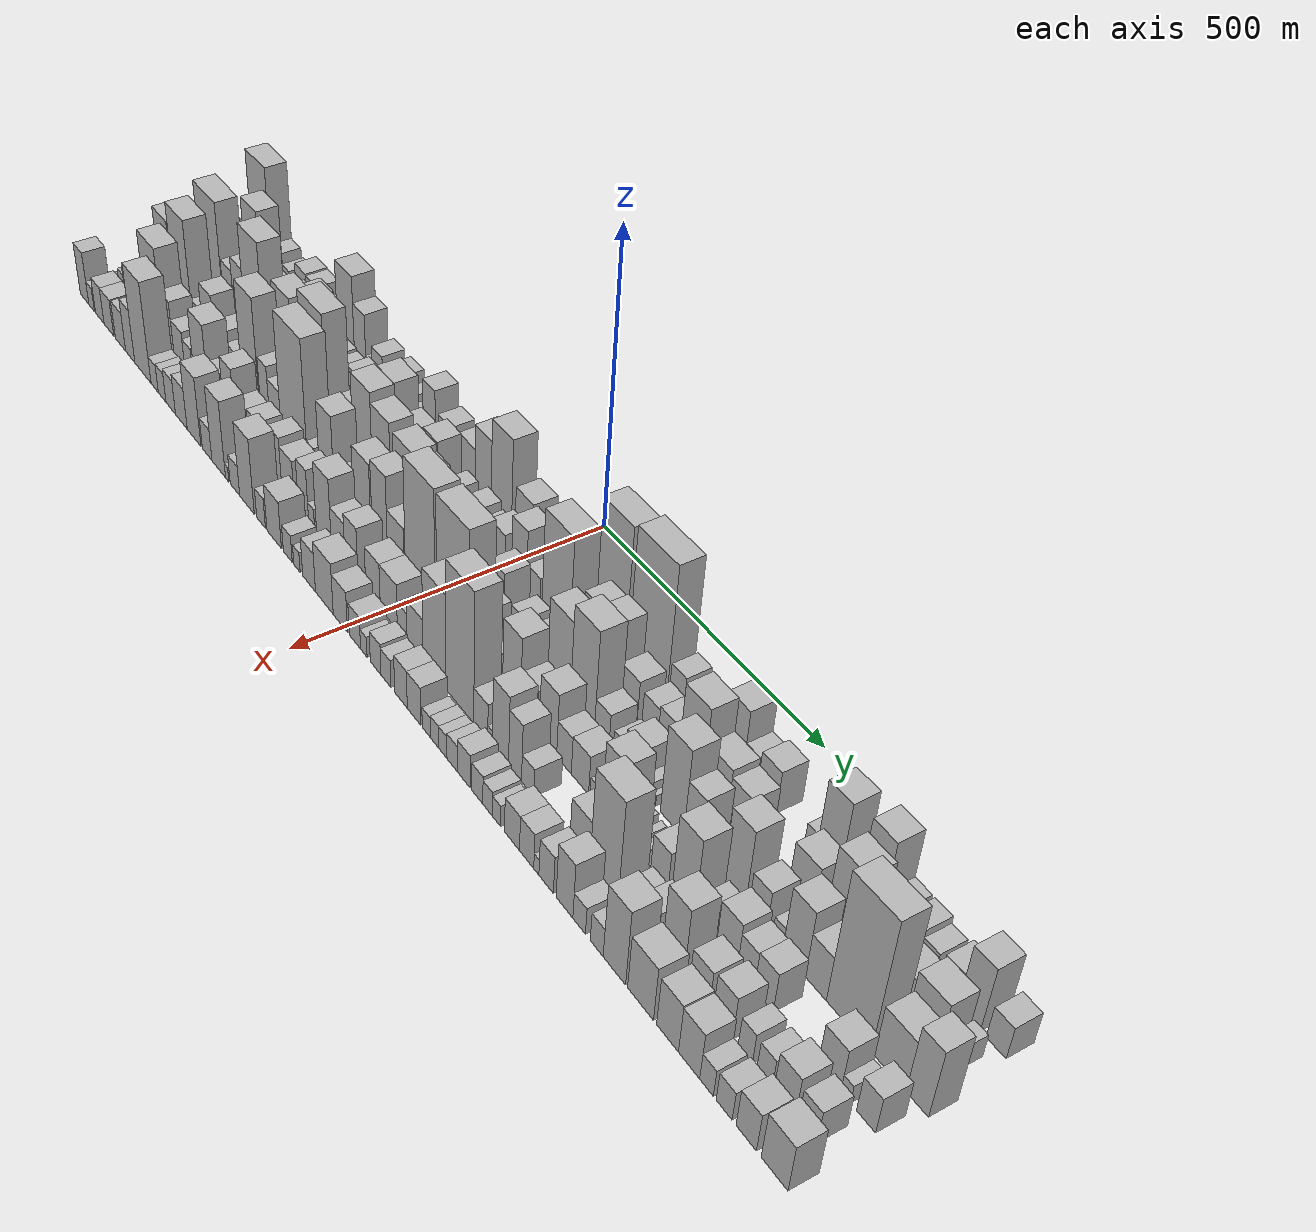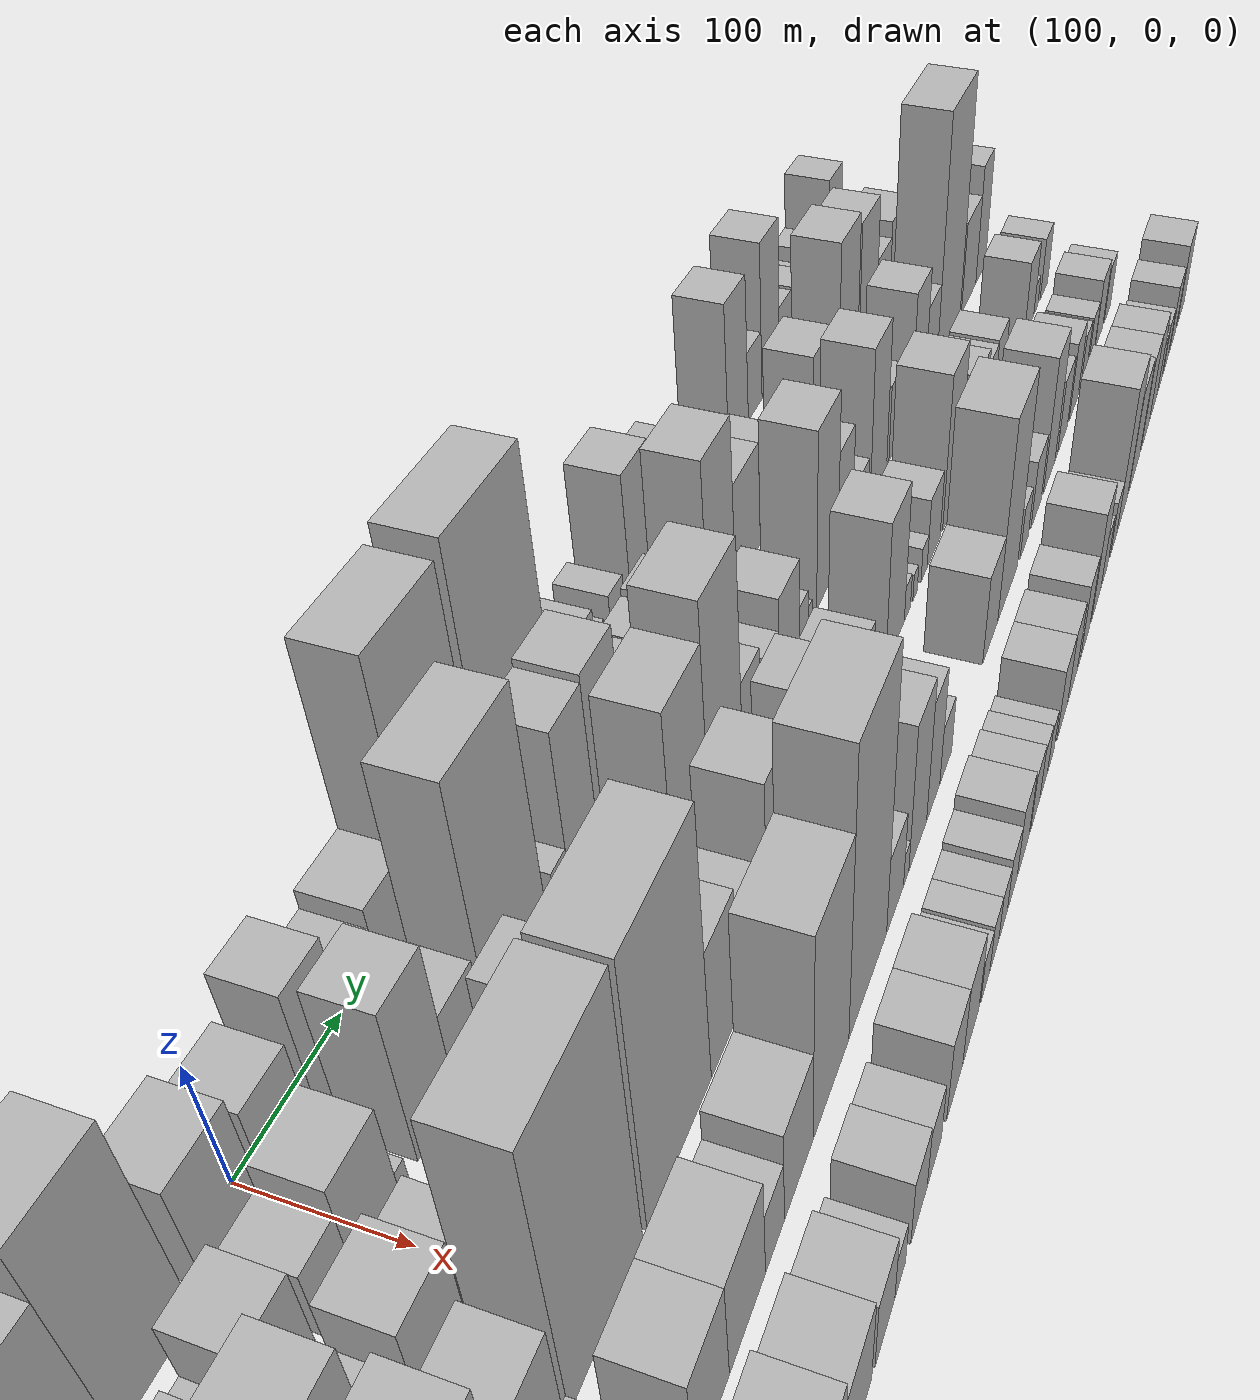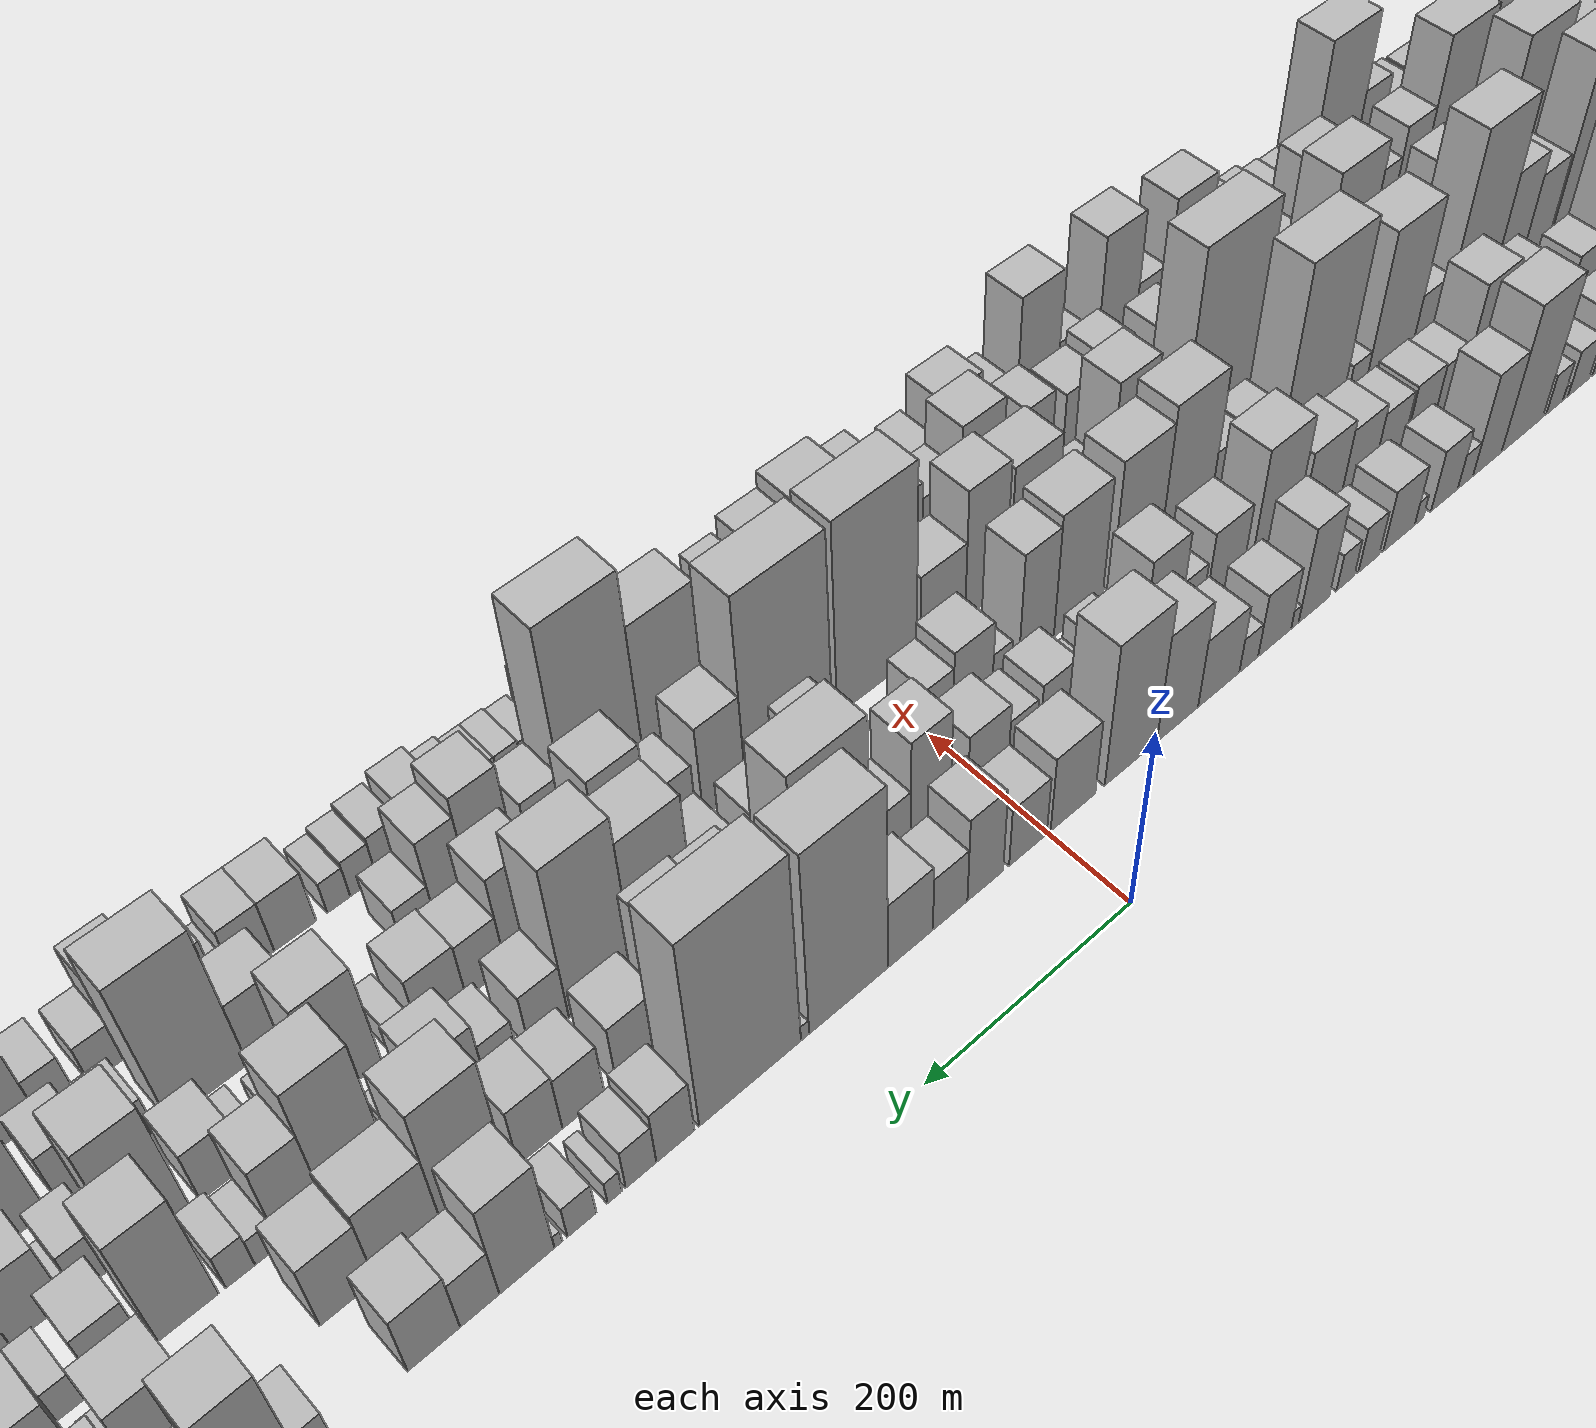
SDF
<sdf version="1.6">
 <world name="default">
  <scene>
   <sky><clouds><speed>12</speed></clouds></sky>
   <ambient>0.4 0.4 0.4 1</ambient>
   <background>0.7 0.7 0.7 1</background>
   <shadows>1</shadows>
  </scene>
  <gravity>0 0 -9.8066</gravity>
  <magnetic_field>6e-06 2.3e-05 -4.2e-05</magnetic_field>
  <physics default="0" name="default_physics" type="ode">
   <ode>
    <solver>
     <type>quick</type>
     <iters>10</iters>
     <sor>1.0</sor>
     <use_dynamic_moi_rescaling>0</use_dynamic_moi_rescaling>
    </solver>
    <constraints>
     <cfm>0</cfm>
     <erp>0.2</erp>
     <contact_max_correcting_vel>100</contact_max_correcting_vel>
     <contact_surface_layer>0.001</contact_surface_layer>
    </constraints>
   </ode>
   <max_step_size>0.004</max_step_size>
   <real_time_factor>1</real_time_factor>
   <real_time_update_rate>250</real_time_update_rate>
  </physics>
  <light name="sun" type="directional">
   <pose>0 0 10 0 0 0</pose>
   <diffuse>0.8 0.8 0.8 1</diffuse>
   <specular>0.2 0.2 0.2 1</specular>
   <attenuation>
    <range>1000</range>
    <constant>0.9</constant>
    <linear>0.01</linear>
    <quadratic>0.001</quadratic>
   </attenuation>
   <direction>-0.5 0.1 -0.9</direction>
  </light>
  <model name="building_1">
   <static>1</static>
   <pose>100.0000 -925.8570 0 0.000000 0.000000 0.000000</pose>
   <link name="link">
    <pose>0 0 27.00 0 0 0</pose>
    <collision name="collision"><geometry><box><size>40.0000 28.2860 54.0000</size></box></geometry></collision>
    <visual name="visual">
     <cast_shadows>0</cast_shadows>
     <geometry><box><size>40.0000 28.2860 54.0000</size></box></geometry>
     <material>
      <script>
       <uri>model://HANNAS_wall/materials/scripts</uri>
       <uri>model://HANNAS_wall/materials/textures</uri>
       <name>vrc/HANNAS_wall</name>
      </script>
     </material>
    </visual>
   </link>
  </model>
  <model name="building_2">
   <static>1</static>
   <pose>100.0000 -907.5937 0 0.000000 0.000000 0.000000</pose>
   <link name="link">
    <pose>0 0 9.00 0 0 0</pose>
    <collision name="collision"><geometry><box><size>40.0000 8.2405 18.0000</size></box></geometry></collision>
    <visual name="visual">
     <cast_shadows>0</cast_shadows>
     <geometry><box><size>40.0000 8.2405 18.0000</size></box></geometry>
     <material>
      <script>
       <uri>model://HANNAS_wall/materials/scripts</uri>
       <uri>model://HANNAS_wall/materials/textures</uri>
       <name>vrc/HANNAS_wall</name>
      </script>
     </material>
    </visual>
   </link>
  </model>
  <model name="building_3">
   <static>1</static>
   <pose>100.0000 -867.1796 0 0.000000 0.000000 0.000000</pose>
   <link name="link">
    <pose>0 0 102.00 0 0 0</pose>
    <collision name="collision"><geometry><box><size>40.0000 72.5878 204.0000</size></box></geometry></collision>
    <visual name="visual">
     <cast_shadows>0</cast_shadows>
     <geometry><box><size>40.0000 72.5878 204.0000</size></box></geometry>
     <material>
      <script>
       <uri>model://HANNAS_wall/materials/scripts</uri>
       <uri>model://HANNAS_wall/materials/textures</uri>
       <name>vrc/HANNAS_wall</name>
      </script>
     </material>
    </visual>
   </link>
  </model>
  <model name="building_4">
   <static>1</static>
   <pose>100.0000 -813.3753 0 0.000000 0.000000 0.000000</pose>
   <link name="link">
    <pose>0 0 30.00 0 0 0</pose>
    <collision name="collision"><geometry><box><size>40.0000 35.0207 60.0000</size></box></geometry></collision>
    <visual name="visual">
     <cast_shadows>0</cast_shadows>
     <geometry><box><size>40.0000 35.0207 60.0000</size></box></geometry>
     <material>
      <script>
       <uri>model://HANNAS_wall/materials/scripts</uri>
       <uri>model://HANNAS_wall/materials/textures</uri>
       <name>vrc/HANNAS_wall</name>
      </script>
     </material>
    </visual>
   </link>
  </model>
  <model name="building_5">
   <static>1</static>
   <pose>100.0000 -775.6763 0 0.000000 0.000000 0.000000</pose>
   <link name="link">
    <pose>0 0 22.50 0 0 0</pose>
    <collision name="collision"><geometry><box><size>40.0000 26.3772 45.0000</size></box></geometry></collision>
    <visual name="visual">
     <cast_shadows>0</cast_shadows>
     <geometry><box><size>40.0000 26.3772 45.0000</size></box></geometry>
     <material>
      <script>
       <uri>model://HANNAS_wall/materials/scripts</uri>
       <uri>model://HANNAS_wall/materials/textures</uri>
       <name>vrc/HANNAS_wall</name>
      </script>
     </material>
    </visual>
   </link>
  </model>
  <model name="building_6">
   <static>1</static>
   <pose>100.0000 -751.6416 0 0.000000 0.000000 0.000000</pose>
   <link name="link">
    <pose>0 0 19.50 0 0 0</pose>
    <collision name="collision"><geometry><box><size>40.0000 21.6923 39.0000</size></box></geometry></collision>
    <visual name="visual">
     <cast_shadows>0</cast_shadows>
     <geometry><box><size>40.0000 21.6923 39.0000</size></box></geometry>
     <material>
      <script>
       <uri>model://HANNAS_wall/materials/scripts</uri>
       <uri>model://HANNAS_wall/materials/textures</uri>
       <name>vrc/HANNAS_wall</name>
      </script>
     </material>
    </visual>
   </link>
  </model>
  <model name="building_7">
   <static>1</static>
   <pose>100.0000 -718.3860 0 0.000000 0.000000 0.000000</pose>
   <link name="link">
    <pose>0 0 37.50 0 0 0</pose>
    <collision name="collision"><geometry><box><size>40.0000 38.8188 75.0000</size></box></geometry></collision>
    <visual name="visual">
     <cast_shadows>0</cast_shadows>
     <geometry><box><size>40.0000 38.8188 75.0000</size></box></geometry>
     <material>
      <script>
       <uri>model://HANNAS_wall/materials/scripts</uri>
       <uri>model://HANNAS_wall/materials/textures</uri>
       <name>vrc/HANNAS_wall</name>
      </script>
     </material>
    </visual>
   </link>
  </model>
  <model name="building_8">
   <static>1</static>
   <pose>100.0000 -679.2799 0 0.000000 0.000000 0.000000</pose>
   <link name="link">
    <pose>0 0 36.00 0 0 0</pose>
    <collision name="collision"><geometry><box><size>40.0000 39.3933 72.0000</size></box></geometry></collision>
    <visual name="visual">
     <cast_shadows>0</cast_shadows>
     <geometry><box><size>40.0000 39.3933 72.0000</size></box></geometry>
     <material>
      <script>
       <uri>model://HANNAS_wall/materials/scripts</uri>
       <uri>model://HANNAS_wall/materials/textures</uri>
       <name>vrc/HANNAS_wall</name>
      </script>
     </material>
    </visual>
   </link>
  </model>
  <model name="building_9">
   <static>1</static>
   <pose>100.0000 -639.7882 0 0.000000 0.000000 0.000000</pose>
   <link name="link">
    <pose>0 0 25.50 0 0 0</pose>
    <collision name="collision"><geometry><box><size>40.0000 29.5902 51.0000</size></box></geometry></collision>
    <visual name="visual">
     <cast_shadows>0</cast_shadows>
     <geometry><box><size>40.0000 29.5902 51.0000</size></box></geometry>
     <material>
      <script>
       <uri>model://HANNAS_wall/materials/scripts</uri>
       <uri>model://HANNAS_wall/materials/textures</uri>
       <name>vrc/HANNAS_wall</name>
      </script>
     </material>
    </visual>
   </link>
  </model>
  <model name="building_10">
   <static>1</static>
   <pose>100.0000 -621.4245 0 0.000000 0.000000 0.000000</pose>
   <link name="link">
    <pose>0 0 7.50 0 0 0</pose>
    <collision name="collision"><geometry><box><size>40.0000 7.1371 15.0000</size></box></geometry></collision>
    <visual name="visual">
     <cast_shadows>0</cast_shadows>
     <geometry><box><size>40.0000 7.1371 15.0000</size></box></geometry>
     <material>
      <script>
       <uri>model://HANNAS_wall/materials/scripts</uri>
       <uri>model://HANNAS_wall/materials/textures</uri>
       <name>vrc/HANNAS_wall</name>
      </script>
     </material>
    </visual>
   </link>
  </model>
  <model name="building_11">
   <static>1</static>
   <pose>100.0000 -606.1702 0 0.000000 0.000000 0.000000</pose>
   <link name="link">
    <pose>0 0 22.50 0 0 0</pose>
    <collision name="collision"><geometry><box><size>40.0000 23.3716 45.0000</size></box></geometry></collision>
    <visual name="visual">
     <cast_shadows>0</cast_shadows>
     <geometry><box><size>40.0000 23.3716 45.0000</size></box></geometry>
     <material>
      <script>
       <uri>model://HANNAS_wall/materials/scripts</uri>
       <uri>model://HANNAS_wall/materials/textures</uri>
       <name>vrc/HANNAS_wall</name>
      </script>
     </material>
    </visual>
   </link>
  </model>
  <model name="building_12">
   <static>1</static>
   <pose>100.0000 -561.4425 0 0.000000 0.000000 0.000000</pose>
   <link name="link">
    <pose>0 0 81.00 0 0 0</pose>
    <collision name="collision"><geometry><box><size>40.0000 56.0838 162.0000</size></box></geometry></collision>
    <visual name="visual">
     <cast_shadows>0</cast_shadows>
     <geometry><box><size>40.0000 56.0838 162.0000</size></box></geometry>
     <material>
      <script>
       <uri>model://HANNAS_wall/materials/scripts</uri>
       <uri>model://HANNAS_wall/materials/textures</uri>
       <name>vrc/HANNAS_wall</name>
      </script>
     </material>
    </visual>
   </link>
  </model>
  <model name="building_13">
   <static>1</static>
   <pose>100.0000 -514.2664 0 0.000000 0.000000 0.000000</pose>
   <link name="link">
    <pose>0 0 57.00 0 0 0</pose>
    <collision name="collision"><geometry><box><size>40.0000 38.2684 114.0000</size></box></geometry></collision>
    <visual name="visual">
     <cast_shadows>0</cast_shadows>
     <geometry><box><size>40.0000 38.2684 114.0000</size></box></geometry>
     <material>
      <script>
       <uri>model://HANNAS_wall/materials/scripts</uri>
       <uri>model://HANNAS_wall/materials/textures</uri>
       <name>vrc/HANNAS_wall</name>
      </script>
     </material>
    </visual>
   </link>
  </model>
  <model name="building_14">
   <static>1</static>
   <pose>100.0000 -485.1977 0 0.000000 0.000000 0.000000</pose>
   <link name="link">
    <pose>0 0 19.50 0 0 0</pose>
    <collision name="collision"><geometry><box><size>40.0000 19.8689 39.0000</size></box></geometry></collision>
    <visual name="visual">
     <cast_shadows>0</cast_shadows>
     <geometry><box><size>40.0000 19.8689 39.0000</size></box></geometry>
     <material>
      <script>
       <uri>model://HANNAS_wall/materials/scripts</uri>
       <uri>model://HANNAS_wall/materials/textures</uri>
       <name>vrc/HANNAS_wall</name>
      </script>
     </material>
    </visual>
   </link>
  </model>
  <model name="building_15">
   <static>1</static>
   <pose>100.0000 -457.8230 0 0.000000 0.000000 0.000000</pose>
   <link name="link">
    <pose>0 0 34.50 0 0 0</pose>
    <collision name="collision"><geometry><box><size>40.0000 34.8806 69.0000</size></box></geometry></collision>
    <visual name="visual">
     <cast_shadows>0</cast_shadows>
     <geometry><box><size>40.0000 34.8806 69.0000</size></box></geometry>
     <material>
      <script>
       <uri>model://HANNAS_wall/materials/scripts</uri>
       <uri>model://HANNAS_wall/materials/textures</uri>
       <name>vrc/HANNAS_wall</name>
      </script>
     </material>
    </visual>
   </link>
  </model>
  <model name="building_16">
   <static>1</static>
   <pose>100.0000 -424.9393 0 0.000000 0.000000 0.000000</pose>
   <link name="link">
    <pose>0 0 13.50 0 0 0</pose>
    <collision name="collision"><geometry><box><size>40.0000 10.8869 27.0000</size></box></geometry></collision>
    <visual name="visual">
     <cast_shadows>0</cast_shadows>
     <geometry><box><size>40.0000 10.8869 27.0000</size></box></geometry>
     <material>
      <script>
       <uri>model://HANNAS_wall/materials/scripts</uri>
       <uri>model://HANNAS_wall/materials/textures</uri>
       <name>vrc/HANNAS_wall</name>
      </script>
     </material>
    </visual>
   </link>
  </model>
  <model name="building_17">
   <static>1</static>
   <pose>100.0000 -399.5099 0 0.000000 0.000000 0.000000</pose>
   <link name="link">
    <pose>0 0 34.50 0 0 0</pose>
    <collision name="collision"><geometry><box><size>40.0000 39.9718 69.0000</size></box></geometry></collision>
    <visual name="visual">
     <cast_shadows>0</cast_shadows>
     <geometry><box><size>40.0000 39.9718 69.0000</size></box></geometry>
     <material>
      <script>
       <uri>model://HANNAS_wall/materials/scripts</uri>
       <uri>model://HANNAS_wall/materials/textures</uri>
       <name>vrc/HANNAS_wall</name>
      </script>
     </material>
    </visual>
   </link>
  </model>
  <model name="building_18">
   <static>1</static>
   <pose>100.0000 -361.6292 0 0.000000 0.000000 0.000000</pose>
   <link name="link">
    <pose>0 0 25.50 0 0 0</pose>
    <collision name="collision"><geometry><box><size>40.0000 25.7896 51.0000</size></box></geometry></collision>
    <visual name="visual">
     <cast_shadows>0</cast_shadows>
     <geometry><box><size>40.0000 25.7896 51.0000</size></box></geometry>
     <material>
      <script>
       <uri>model://HANNAS_wall/materials/scripts</uri>
       <uri>model://HANNAS_wall/materials/textures</uri>
       <name>vrc/HANNAS_wall</name>
      </script>
     </material>
    </visual>
   </link>
  </model>
  <model name="building_19">
   <static>1</static>
   <pose>100.0000 -332.9028 0 0.000000 0.000000 0.000000</pose>
   <link name="link">
    <pose>0 0 21.00 0 0 0</pose>
    <collision name="collision"><geometry><box><size>40.0000 21.6632 42.0000</size></box></geometry></collision>
    <visual name="visual">
     <cast_shadows>0</cast_shadows>
     <geometry><box><size>40.0000 21.6632 42.0000</size></box></geometry>
     <material>
      <script>
       <uri>model://HANNAS_wall/materials/scripts</uri>
       <uri>model://HANNAS_wall/materials/textures</uri>
       <name>vrc/HANNAS_wall</name>
      </script>
     </material>
    </visual>
   </link>
  </model>
  <model name="building_20">
   <static>1</static>
   <pose>100.0000 -294.7957 0 0.000000 0.000000 0.000000</pose>
   <link name="link">
    <pose>0 0 54.00 0 0 0</pose>
    <collision name="collision"><geometry><box><size>40.0000 36.5510 108.0000</size></box></geometry></collision>
    <visual name="visual">
     <cast_shadows>0</cast_shadows>
     <geometry><box><size>40.0000 36.5510 108.0000</size></box></geometry>
     <material>
      <script>
       <uri>model://HANNAS_wall/materials/scripts</uri>
       <uri>model://HANNAS_wall/materials/textures</uri>
       <name>vrc/HANNAS_wall</name>
      </script>
     </material>
    </visual>
   </link>
  </model>
  <model name="building_21">
   <static>1</static>
   <pose>100.0000 -272.0801 0 0.000000 0.000000 0.000000</pose>
   <link name="link">
    <pose>0 0 10.50 0 0 0</pose>
    <collision name="collision"><geometry><box><size>40.0000 8.8802 21.0000</size></box></geometry></collision>
    <visual name="visual">
     <cast_shadows>0</cast_shadows>
     <geometry><box><size>40.0000 8.8802 21.0000</size></box></geometry>
     <material>
      <script>
       <uri>model://HANNAS_wall/materials/scripts</uri>
       <uri>model://HANNAS_wall/materials/textures</uri>
       <name>vrc/HANNAS_wall</name>
      </script>
     </material>
    </visual>
   </link>
  </model>
  <model name="building_22">
   <static>1</static>
   <pose>100.0000 -248.2744 0 0.000000 0.000000 0.000000</pose>
   <link name="link">
    <pose>0 0 36.00 0 0 0</pose>
    <collision name="collision"><geometry><box><size>40.0000 38.7312 72.0000</size></box></geometry></collision>
    <visual name="visual">
     <cast_shadows>0</cast_shadows>
     <geometry><box><size>40.0000 38.7312 72.0000</size></box></geometry>
     <material>
      <script>
       <uri>model://HANNAS_wall/materials/scripts</uri>
       <uri>model://HANNAS_wall/materials/textures</uri>
       <name>vrc/HANNAS_wall</name>
      </script>
     </material>
    </visual>
   </link>
  </model>
  <model name="building_23">
   <static>1</static>
   <pose>100.0000 -218.1136 0 0.000000 0.000000 0.000000</pose>
   <link name="link">
    <pose>0 0 19.50 0 0 0</pose>
    <collision name="collision"><geometry><box><size>40.0000 21.5905 39.0000</size></box></geometry></collision>
    <visual name="visual">
     <cast_shadows>0</cast_shadows>
     <geometry><box><size>40.0000 21.5905 39.0000</size></box></geometry>
     <material>
      <script>
       <uri>model://HANNAS_wall/materials/scripts</uri>
       <uri>model://HANNAS_wall/materials/textures</uri>
       <name>vrc/HANNAS_wall</name>
      </script>
     </material>
    </visual>
   </link>
  </model>
  <model name="building_24">
   <static>1</static>
   <pose>100.0000 -183.9354 0 0.000000 0.000000 0.000000</pose>
   <link name="link">
    <pose>0 0 39.00 0 0 0</pose>
    <collision name="collision"><geometry><box><size>40.0000 46.7659 78.0000</size></box></geometry></collision>
    <visual name="visual">
     <cast_shadows>0</cast_shadows>
     <geometry><box><size>40.0000 46.7659 78.0000</size></box></geometry>
     <material>
      <script>
       <uri>model://HANNAS_wall/materials/scripts</uri>
       <uri>model://HANNAS_wall/materials/textures</uri>
       <name>vrc/HANNAS_wall</name>
      </script>
     </material>
    </visual>
   </link>
  </model>
  <model name="building_25">
   <static>1</static>
   <pose>100.0000 -137.7930 0 0.000000 0.000000 0.000000</pose>
   <link name="link">
    <pose>0 0 61.50 0 0 0</pose>
    <collision name="collision"><geometry><box><size>40.0000 45.5188 123.0000</size></box></geometry></collision>
    <visual name="visual">
     <cast_shadows>0</cast_shadows>
     <geometry><box><size>40.0000 45.5188 123.0000</size></box></geometry>
     <material>
      <script>
       <uri>model://HANNAS_wall/materials/scripts</uri>
       <uri>model://HANNAS_wall/materials/textures</uri>
       <name>vrc/HANNAS_wall</name>
      </script>
     </material>
    </visual>
   </link>
  </model>
  <model name="building_26">
   <static>1</static>
   <pose>100.0000 -86.9769 0 0.000000 0.000000 0.000000</pose>
   <link name="link">
    <pose>0 0 81.00 0 0 0</pose>
    <collision name="collision"><geometry><box><size>40.0000 56.1133 162.0000</size></box></geometry></collision>
    <visual name="visual">
     <cast_shadows>0</cast_shadows>
     <geometry><box><size>40.0000 56.1133 162.0000</size></box></geometry>
     <material>
      <script>
       <uri>model://HANNAS_wall/materials/scripts</uri>
       <uri>model://HANNAS_wall/materials/textures</uri>
       <name>vrc/HANNAS_wall</name>
      </script>
     </material>
    </visual>
   </link>
  </model>
  <model name="building_27">
   <static>1</static>
   <pose>100.0000 -25.7199 0 0.000000 0.000000 0.000000</pose>
   <link name="link">
    <pose>0 0 43.50 0 0 0</pose>
    <collision name="collision"><geometry><box><size>40.0000 46.4008 87.0000</size></box></geometry></collision>
    <visual name="visual">
     <cast_shadows>0</cast_shadows>
     <geometry><box><size>40.0000 46.4008 87.0000</size></box></geometry>
     <material>
      <script>
       <uri>model://HANNAS_wall/materials/scripts</uri>
       <uri>model://HANNAS_wall/materials/textures</uri>
       <name>vrc/HANNAS_wall</name>
      </script>
     </material>
    </visual>
   </link>
  </model>
  <model name="building_28">
   <static>1</static>
   <pose>100.0000 20.5680 0 0.000000 0.000000 0.000000</pose>
   <link name="link">
    <pose>0 0 34.50 0 0 0</pose>
    <collision name="collision"><geometry><box><size>40.0000 38.1749 69.0000</size></box></geometry></collision>
    <visual name="visual">
     <cast_shadows>0</cast_shadows>
     <geometry><box><size>40.0000 38.1749 69.0000</size></box></geometry>
     <material>
      <script>
       <uri>model://HANNAS_wall/materials/scripts</uri>
       <uri>model://HANNAS_wall/materials/textures</uri>
       <name>vrc/HANNAS_wall</name>
      </script>
     </material>
    </visual>
   </link>
  </model>
  <model name="building_29">
   <static>1</static>
   <pose>100.0000 63.3625 0 0.000000 0.000000 0.000000</pose>
   <link name="link">
    <pose>0 0 49.50 0 0 0</pose>
    <collision name="collision"><geometry><box><size>40.0000 35.4141 99.0000</size></box></geometry></collision>
    <visual name="visual">
     <cast_shadows>0</cast_shadows>
     <geometry><box><size>40.0000 35.4141 99.0000</size></box></geometry>
     <material>
      <script>
       <uri>model://HANNAS_wall/materials/scripts</uri>
       <uri>model://HANNAS_wall/materials/textures</uri>
       <name>vrc/HANNAS_wall</name>
      </script>
     </material>
    </visual>
   </link>
  </model>
  <model name="building_30">
   <static>1</static>
   <pose>100.0000 97.8033 0 0.000000 0.000000 0.000000</pose>
   <link name="link">
    <pose>0 0 31.50 0 0 0</pose>
    <collision name="collision"><geometry><box><size>40.0000 33.4676 63.0000</size></box></geometry></collision>
    <visual name="visual">
     <cast_shadows>0</cast_shadows>
     <geometry><box><size>40.0000 33.4676 63.0000</size></box></geometry>
     <material>
      <script>
       <uri>model://HANNAS_wall/materials/scripts</uri>
       <uri>model://HANNAS_wall/materials/textures</uri>
       <name>vrc/HANNAS_wall</name>
      </script>
     </material>
    </visual>
   </link>
  </model>
  <model name="building_31">
   <static>1</static>
   <pose>100.0000 135.9520 0 0.000000 0.000000 0.000000</pose>
   <link name="link">
    <pose>0 0 39.00 0 0 0</pose>
    <collision name="collision"><geometry><box><size>40.0000 42.8297 78.0000</size></box></geometry></collision>
    <visual name="visual">
     <cast_shadows>0</cast_shadows>
     <geometry><box><size>40.0000 42.8297 78.0000</size></box></geometry>
     <material>
      <script>
       <uri>model://HANNAS_wall/materials/scripts</uri>
       <uri>model://HANNAS_wall/materials/textures</uri>
       <name>vrc/HANNAS_wall</name>
      </script>
     </material>
    </visual>
   </link>
  </model>
  <model name="building_32">
   <static>1</static>
   <pose>100.0000 193.5673 0 0.000000 0.000000 0.000000</pose>
   <link name="link">
    <pose>0 0 108.00 0 0 0</pose>
    <collision name="collision"><geometry><box><size>40.0000 72.4009 216.0000</size></box></geometry></collision>
    <visual name="visual">
     <cast_shadows>0</cast_shadows>
     <geometry><box><size>40.0000 72.4009 216.0000</size></box></geometry>
     <material>
      <script>
       <uri>model://HANNAS_wall/materials/scripts</uri>
       <uri>model://HANNAS_wall/materials/textures</uri>
       <name>vrc/HANNAS_wall</name>
      </script>
     </material>
    </visual>
   </link>
  </model>
  <model name="building_33">
   <static>1</static>
   <pose>100.0000 233.4649 0 0.000000 0.000000 0.000000</pose>
   <link name="link">
    <pose>0 0 9.00 0 0 0</pose>
    <collision name="collision"><geometry><box><size>40.0000 7.3943 18.0000</size></box></geometry></collision>
    <visual name="visual">
     <cast_shadows>0</cast_shadows>
     <geometry><box><size>40.0000 7.3943 18.0000</size></box></geometry>
     <material>
      <script>
       <uri>model://HANNAS_wall/materials/scripts</uri>
       <uri>model://HANNAS_wall/materials/textures</uri>
       <name>vrc/HANNAS_wall</name>
      </script>
     </material>
    </visual>
   </link>
  </model>
  <model name="building_34">
   <static>1</static>
   <pose>100.0000 281.5969 0 0.000000 0.000000 0.000000</pose>
   <link name="link">
    <pose>0 0 112.50 0 0 0</pose>
    <collision name="collision"><geometry><box><size>40.0000 88.8697 225.0000</size></box></geometry></collision>
    <visual name="visual">
     <cast_shadows>0</cast_shadows>
     <geometry><box><size>40.0000 88.8697 225.0000</size></box></geometry>
     <material>
      <script>
       <uri>model://HANNAS_wall/materials/scripts</uri>
       <uri>model://HANNAS_wall/materials/textures</uri>
       <name>vrc/HANNAS_wall</name>
      </script>
     </material>
    </visual>
   </link>
  </model>
  <model name="building_35">
   <static>1</static>
   <pose>100.0000 346.0540 0 0.000000 0.000000 0.000000</pose>
   <link name="link">
    <pose>0 0 31.50 0 0 0</pose>
    <collision name="collision"><geometry><box><size>40.0000 32.0444 63.0000</size></box></geometry></collision>
    <visual name="visual">
     <cast_shadows>0</cast_shadows>
     <geometry><box><size>40.0000 32.0444 63.0000</size></box></geometry>
     <material>
      <script>
       <uri>model://HANNAS_wall/materials/scripts</uri>
       <uri>model://HANNAS_wall/materials/textures</uri>
       <name>vrc/HANNAS_wall</name>
      </script>
     </material>
    </visual>
   </link>
  </model>
  <model name="building_36">
   <static>1</static>
   <pose>100.0000 374.7525 0 0.000000 0.000000 0.000000</pose>
   <link name="link">
    <pose>0 0 24.00 0 0 0</pose>
    <collision name="collision"><geometry><box><size>40.0000 25.3526 48.0000</size></box></geometry></collision>
    <visual name="visual">
     <cast_shadows>0</cast_shadows>
     <geometry><box><size>40.0000 25.3526 48.0000</size></box></geometry>
     <material>
      <script>
       <uri>model://HANNAS_wall/materials/scripts</uri>
       <uri>model://HANNAS_wall/materials/textures</uri>
       <name>vrc/HANNAS_wall</name>
      </script>
     </material>
    </visual>
   </link>
  </model>
  <model name="building_37">
   <static>1</static>
   <pose>100.0000 396.3454 0 0.000000 0.000000 0.000000</pose>
   <link name="link">
    <pose>0 0 13.50 0 0 0</pose>
    <collision name="collision"><geometry><box><size>40.0000 11.8333 27.0000</size></box></geometry></collision>
    <visual name="visual">
     <cast_shadows>0</cast_shadows>
     <geometry><box><size>40.0000 11.8333 27.0000</size></box></geometry>
     <material>
      <script>
       <uri>model://HANNAS_wall/materials/scripts</uri>
       <uri>model://HANNAS_wall/materials/textures</uri>
       <name>vrc/HANNAS_wall</name>
      </script>
     </material>
    </visual>
   </link>
  </model>
  <model name="building_38">
   <static>1</static>
   <pose>100.0000 422.8853 0 0.000000 0.000000 0.000000</pose>
   <link name="link">
    <pose>0 0 19.50 0 0 0</pose>
    <collision name="collision"><geometry><box><size>40.0000 23.2465 39.0000</size></box></geometry></collision>
    <visual name="visual">
     <cast_shadows>0</cast_shadows>
     <geometry><box><size>40.0000 23.2465 39.0000</size></box></geometry>
     <material>
      <script>
       <uri>model://HANNAS_wall/materials/scripts</uri>
       <uri>model://HANNAS_wall/materials/textures</uri>
       <name>vrc/HANNAS_wall</name>
      </script>
     </material>
    </visual>
   </link>
  </model>
  <model name="building_39">
   <static>1</static>
   <pose>100.0000 441.6473 0 0.000000 0.000000 0.000000</pose>
   <link name="link">
    <pose>0 0 7.50 0 0 0</pose>
    <collision name="collision"><geometry><box><size>40.0000 6.2776 15.0000</size></box></geometry></collision>
    <visual name="visual">
     <cast_shadows>0</cast_shadows>
     <geometry><box><size>40.0000 6.2776 15.0000</size></box></geometry>
     <material>
      <script>
       <uri>model://HANNAS_wall/materials/scripts</uri>
       <uri>model://HANNAS_wall/materials/textures</uri>
       <name>vrc/HANNAS_wall</name>
      </script>
     </material>
    </visual>
   </link>
  </model>
  <model name="building_40">
   <static>1</static>
   <pose>100.0000 466.2544 0 0.000000 0.000000 0.000000</pose>
   <link name="link">
    <pose>0 0 57.00 0 0 0</pose>
    <collision name="collision"><geometry><box><size>40.0000 42.9366 114.0000</size></box></geometry></collision>
    <visual name="visual">
     <cast_shadows>0</cast_shadows>
     <geometry><box><size>40.0000 42.9366 114.0000</size></box></geometry>
     <material>
      <script>
       <uri>model://HANNAS_wall/materials/scripts</uri>
       <uri>model://HANNAS_wall/materials/textures</uri>
       <name>vrc/HANNAS_wall</name>
      </script>
     </material>
    </visual>
   </link>
  </model>
  <model name="building_41">
   <static>1</static>
   <pose>100.0000 502.7373 0 0.000000 0.000000 0.000000</pose>
   <link name="link">
    <pose>0 0 30.00 0 0 0</pose>
    <collision name="collision"><geometry><box><size>40.0000 30.0292 60.0000</size></box></geometry></collision>
    <visual name="visual">
     <cast_shadows>0</cast_shadows>
     <geometry><box><size>40.0000 30.0292 60.0000</size></box></geometry>
     <material>
      <script>
       <uri>model://HANNAS_wall/materials/scripts</uri>
       <uri>model://HANNAS_wall/materials/textures</uri>
       <name>vrc/HANNAS_wall</name>
      </script>
     </material>
    </visual>
   </link>
  </model>
  <model name="building_42">
   <static>1</static>
   <pose>100.0000 537.3404 0 0.000000 0.000000 0.000000</pose>
   <link name="link">
    <pose>0 0 36.00 0 0 0</pose>
    <collision name="collision"><geometry><box><size>40.0000 39.1769 72.0000</size></box></geometry></collision>
    <visual name="visual">
     <cast_shadows>0</cast_shadows>
     <geometry><box><size>40.0000 39.1769 72.0000</size></box></geometry>
     <material>
      <script>
       <uri>model://HANNAS_wall/materials/scripts</uri>
       <uri>model://HANNAS_wall/materials/textures</uri>
       <name>vrc/HANNAS_wall</name>
      </script>
     </material>
    </visual>
   </link>
  </model>
  <model name="building_43">
   <static>1</static>
   <pose>100.0000 622.6540 0 0.000000 0.000000 0.000000</pose>
   <link name="link">
    <pose>0 0 18.00 0 0 0</pose>
    <collision name="collision"><geometry><box><size>40.0000 21.1501 36.0000</size></box></geometry></collision>
    <visual name="visual">
     <cast_shadows>0</cast_shadows>
     <geometry><box><size>40.0000 21.1501 36.0000</size></box></geometry>
     <material>
      <script>
       <uri>model://HANNAS_wall/materials/scripts</uri>
       <uri>model://HANNAS_wall/materials/textures</uri>
       <name>vrc/HANNAS_wall</name>
      </script>
     </material>
    </visual>
   </link>
  </model>
  <model name="building_44">
   <static>1</static>
   <pose>100.0000 655.3637 0 0.000000 0.000000 0.000000</pose>
   <link name="link">
    <pose>0 0 66.00 0 0 0</pose>
    <collision name="collision"><geometry><box><size>40.0000 44.2693 132.0000</size></box></geometry></collision>
    <visual name="visual">
     <cast_shadows>0</cast_shadows>
     <geometry><box><size>40.0000 44.2693 132.0000</size></box></geometry>
     <material>
      <script>
       <uri>model://HANNAS_wall/materials/scripts</uri>
       <uri>model://HANNAS_wall/materials/textures</uri>
       <name>vrc/HANNAS_wall</name>
      </script>
     </material>
    </visual>
   </link>
  </model>
  <model name="building_45">
   <static>1</static>
   <pose>100.0000 693.5913 0 0.000000 0.000000 0.000000</pose>
   <link name="link">
    <pose>0 0 31.50 0 0 0</pose>
    <collision name="collision"><geometry><box><size>40.0000 32.1860 63.0000</size></box></geometry></collision>
    <visual name="visual">
     <cast_shadows>0</cast_shadows>
     <geometry><box><size>40.0000 32.1860 63.0000</size></box></geometry>
     <material>
      <script>
       <uri>model://HANNAS_wall/materials/scripts</uri>
       <uri>model://HANNAS_wall/materials/textures</uri>
       <name>vrc/HANNAS_wall</name>
      </script>
     </material>
    </visual>
   </link>
  </model>
  <model name="building_46">
   <static>1</static>
   <pose>100.0000 730.8806 0 0.000000 0.000000 0.000000</pose>
   <link name="link">
    <pose>0 0 70.50 0 0 0</pose>
    <collision name="collision"><geometry><box><size>40.0000 42.3927 141.0000</size></box></geometry></collision>
    <visual name="visual">
     <cast_shadows>0</cast_shadows>
     <geometry><box><size>40.0000 42.3927 141.0000</size></box></geometry>
     <material>
      <script>
       <uri>model://HANNAS_wall/materials/scripts</uri>
       <uri>model://HANNAS_wall/materials/textures</uri>
       <name>vrc/HANNAS_wall</name>
      </script>
     </material>
    </visual>
   </link>
  </model>
  <model name="building_47">
   <static>1</static>
   <pose>100.0000 767.2202 0 0.000000 0.000000 0.000000</pose>
   <link name="link">
    <pose>0 0 30.00 0 0 0</pose>
    <collision name="collision"><geometry><box><size>40.0000 30.2864 60.0000</size></box></geometry></collision>
    <visual name="visual">
     <cast_shadows>0</cast_shadows>
     <geometry><box><size>40.0000 30.2864 60.0000</size></box></geometry>
     <material>
      <script>
       <uri>model://HANNAS_wall/materials/scripts</uri>
       <uri>model://HANNAS_wall/materials/textures</uri>
       <name>vrc/HANNAS_wall</name>
      </script>
     </material>
    </visual>
   </link>
  </model>
  <model name="building_48">
   <static>1</static>
   <pose>100.0000 801.8591 0 0.000000 0.000000 0.000000</pose>
   <link name="link">
    <pose>0 0 30.00 0 0 0</pose>
    <collision name="collision"><geometry><box><size>40.0000 30.9913 60.0000</size></box></geometry></collision>
    <visual name="visual">
     <cast_shadows>0</cast_shadows>
     <geometry><box><size>40.0000 30.9913 60.0000</size></box></geometry>
     <material>
      <script>
       <uri>model://HANNAS_wall/materials/scripts</uri>
       <uri>model://HANNAS_wall/materials/textures</uri>
       <name>vrc/HANNAS_wall</name>
      </script>
     </material>
    </visual>
   </link>
  </model>
  <model name="building_49">
   <static>1</static>
   <pose>100.0000 830.7806 0 0.000000 0.000000 0.000000</pose>
   <link name="link">
    <pose>0 0 24.00 0 0 0</pose>
    <collision name="collision"><geometry><box><size>40.0000 26.8517 48.0000</size></box></geometry></collision>
    <visual name="visual">
     <cast_shadows>0</cast_shadows>
     <geometry><box><size>40.0000 26.8517 48.0000</size></box></geometry>
     <material>
      <script>
       <uri>model://HANNAS_wall/materials/scripts</uri>
       <uri>model://HANNAS_wall/materials/textures</uri>
       <name>vrc/HANNAS_wall</name>
      </script>
     </material>
    </visual>
   </link>
  </model>
  <model name="building_50">
   <static>1</static>
   <pose>100.0000 868.0467 0 0.000000 0.000000 0.000000</pose>
   <link name="link">
    <pose>0 0 28.50 0 0 0</pose>
    <collision name="collision"><geometry><box><size>40.0000 31.6805 57.0000</size></box></geometry></collision>
    <visual name="visual">
     <cast_shadows>0</cast_shadows>
     <geometry><box><size>40.0000 31.6805 57.0000</size></box></geometry>
     <material>
      <script>
       <uri>model://HANNAS_wall/materials/scripts</uri>
       <uri>model://HANNAS_wall/materials/textures</uri>
       <name>vrc/HANNAS_wall</name>
      </script>
     </material>
    </visual>
   </link>
  </model>
  <model name="building_51">
   <static>1</static>
   <pose>100.0000 902.3525 0 0.000000 0.000000 0.000000</pose>
   <link name="link">
    <pose>0 0 54.00 0 0 0</pose>
    <collision name="collision"><geometry><box><size>40.0000 36.9312 108.0000</size></box></geometry></collision>
    <visual name="visual">
     <cast_shadows>0</cast_shadows>
     <geometry><box><size>40.0000 36.9312 108.0000</size></box></geometry>
     <material>
      <script>
       <uri>model://HANNAS_wall/materials/scripts</uri>
       <uri>model://HANNAS_wall/materials/textures</uri>
       <name>vrc/HANNAS_wall</name>
      </script>
     </material>
    </visual>
   </link>
  </model>
  <model name="building_52">
   <static>1</static>
   <pose>100.0000 945.7392 0 0.000000 0.000000 0.000000</pose>
   <link name="link">
    <pose>0 0 27.00 0 0 0</pose>
    <collision name="collision"><geometry><box><size>40.0000 31.8421 54.0000</size></box></geometry></collision>
    <visual name="visual">
     <cast_shadows>0</cast_shadows>
     <geometry><box><size>40.0000 31.8421 54.0000</size></box></geometry>
     <material>
      <script>
       <uri>model://HANNAS_wall/materials/scripts</uri>
       <uri>model://HANNAS_wall/materials/textures</uri>
       <name>vrc/HANNAS_wall</name>
      </script>
     </material>
    </visual>
   </link>
  </model>
  <model name="building_53">
   <static>1</static>
   <pose>160.0000 -919.6051 0 0.000000 0.000000 0.000000</pose>
   <link name="link">
    <pose>0 0 40.50 0 0 0</pose>
    <collision name="collision"><geometry><box><size>40.0000 40.7898 81.0000</size></box></geometry></collision>
    <visual name="visual">
     <cast_shadows>0</cast_shadows>
     <geometry><box><size>40.0000 40.7898 81.0000</size></box></geometry>
     <material>
      <script>
       <uri>model://HANNAS_wall/materials/scripts</uri>
       <uri>model://HANNAS_wall/materials/textures</uri>
       <name>vrc/HANNAS_wall</name>
      </script>
     </material>
    </visual>
   </link>
  </model>
  <model name="building_54">
   <static>1</static>
   <pose>160.0000 -872.5477 0 0.000000 0.000000 0.000000</pose>
   <link name="link">
    <pose>0 0 34.50 0 0 0</pose>
    <collision name="collision"><geometry><box><size>40.0000 39.3249 69.0000</size></box></geometry></collision>
    <visual name="visual">
     <cast_shadows>0</cast_shadows>
     <geometry><box><size>40.0000 39.3249 69.0000</size></box></geometry>
     <material>
      <script>
       <uri>model://HANNAS_wall/materials/scripts</uri>
       <uri>model://HANNAS_wall/materials/textures</uri>
       <name>vrc/HANNAS_wall</name>
      </script>
     </material>
    </visual>
   </link>
  </model>
  <model name="building_55">
   <static>1</static>
   <pose>160.0000 -835.2553 0 0.000000 0.000000 0.000000</pose>
   <link name="link">
    <pose>0 0 15.00 0 0 0</pose>
    <collision name="collision"><geometry><box><size>40.0000 15.2600 30.0000</size></box></geometry></collision>
    <visual name="visual">
     <cast_shadows>0</cast_shadows>
     <geometry><box><size>40.0000 15.2600 30.0000</size></box></geometry>
     <material>
      <script>
       <uri>model://HANNAS_wall/materials/scripts</uri>
       <uri>model://HANNAS_wall/materials/textures</uri>
       <name>vrc/HANNAS_wall</name>
      </script>
     </material>
    </visual>
   </link>
  </model>
  <model name="building_56">
   <static>1</static>
   <pose>160.0000 -813.1141 0 0.000000 0.000000 0.000000</pose>
   <link name="link">
    <pose>0 0 27.00 0 0 0</pose>
    <collision name="collision"><geometry><box><size>40.0000 29.0226 54.0000</size></box></geometry></collision>
    <visual name="visual">
     <cast_shadows>0</cast_shadows>
     <geometry><box><size>40.0000 29.0226 54.0000</size></box></geometry>
     <material>
      <script>
       <uri>model://HANNAS_wall/materials/scripts</uri>
       <uri>model://HANNAS_wall/materials/textures</uri>
       <name>vrc/HANNAS_wall</name>
      </script>
     </material>
    </visual>
   </link>
  </model>
  <model name="building_57">
   <static>1</static>
   <pose>160.0000 -770.1726 0 0.000000 0.000000 0.000000</pose>
   <link name="link">
    <pose>0 0 93.00 0 0 0</pose>
    <collision name="collision"><geometry><box><size>40.0000 56.8603 186.0000</size></box></geometry></collision>
    <visual name="visual">
     <cast_shadows>0</cast_shadows>
     <geometry><box><size>40.0000 56.8603 186.0000</size></box></geometry>
     <material>
      <script>
       <uri>model://HANNAS_wall/materials/scripts</uri>
       <uri>model://HANNAS_wall/materials/textures</uri>
       <name>vrc/HANNAS_wall</name>
      </script>
     </material>
    </visual>
   </link>
  </model>
  <model name="building_58">
   <static>1</static>
   <pose>160.0000 -722.9349 0 0.000000 0.000000 0.000000</pose>
   <link name="link">
    <pose>0 0 33.00 0 0 0</pose>
    <collision name="collision"><geometry><box><size>40.0000 37.6151 66.0000</size></box></geometry></collision>
    <visual name="visual">
     <cast_shadows>0</cast_shadows>
     <geometry><box><size>40.0000 37.6151 66.0000</size></box></geometry>
     <material>
      <script>
       <uri>model://HANNAS_wall/materials/scripts</uri>
       <uri>model://HANNAS_wall/materials/textures</uri>
       <name>vrc/HANNAS_wall</name>
      </script>
     </material>
    </visual>
   </link>
  </model>
  <model name="building_59">
   <static>1</static>
   <pose>160.0000 -693.7394 0 0.000000 0.000000 0.000000</pose>
   <link name="link">
    <pose>0 0 18.00 0 0 0</pose>
    <collision name="collision"><geometry><box><size>40.0000 20.7759 36.0000</size></box></geometry></collision>
    <visual name="visual">
     <cast_shadows>0</cast_shadows>
     <geometry><box><size>40.0000 20.7759 36.0000</size></box></geometry>
     <material>
      <script>
       <uri>model://HANNAS_wall/materials/scripts</uri>
       <uri>model://HANNAS_wall/materials/textures</uri>
       <name>vrc/HANNAS_wall</name>
      </script>
     </material>
    </visual>
   </link>
  </model>
  <model name="building_60">
   <static>1</static>
   <pose>160.0000 -671.8952 0 0.000000 0.000000 0.000000</pose>
   <link name="link">
    <pose>0 0 21.00 0 0 0</pose>
    <collision name="collision"><geometry><box><size>40.0000 22.9124 42.0000</size></box></geometry></collision>
    <visual name="visual">
     <cast_shadows>0</cast_shadows>
     <geometry><box><size>40.0000 22.9124 42.0000</size></box></geometry>
     <material>
      <script>
       <uri>model://HANNAS_wall/materials/scripts</uri>
       <uri>model://HANNAS_wall/materials/textures</uri>
       <name>vrc/HANNAS_wall</name>
      </script>
     </material>
    </visual>
   </link>
  </model>
  <model name="building_61">
   <static>1</static>
   <pose>160.0000 -645.0639 0 0.000000 0.000000 0.000000</pose>
   <link name="link">
    <pose>0 0 46.50 0 0 0</pose>
    <collision name="collision"><geometry><box><size>40.0000 30.7503 93.0000</size></box></geometry></collision>
    <visual name="visual">
     <cast_shadows>0</cast_shadows>
     <geometry><box><size>40.0000 30.7503 93.0000</size></box></geometry>
     <material>
      <script>
       <uri>model://HANNAS_wall/materials/scripts</uri>
       <uri>model://HANNAS_wall/materials/textures</uri>
       <name>vrc/HANNAS_wall</name>
      </script>
     </material>
    </visual>
   </link>
  </model>
  <model name="building_62">
   <static>1</static>
   <pose>160.0000 -615.5391 0 0.000000 0.000000 0.000000</pose>
   <link name="link">
    <pose>0 0 25.50 0 0 0</pose>
    <collision name="collision"><geometry><box><size>40.0000 28.2992 51.0000</size></box></geometry></collision>
    <visual name="visual">
     <cast_shadows>0</cast_shadows>
     <geometry><box><size>40.0000 28.2992 51.0000</size></box></geometry>
     <material>
      <script>
       <uri>model://HANNAS_wall/materials/scripts</uri>
       <uri>model://HANNAS_wall/materials/textures</uri>
       <name>vrc/HANNAS_wall</name>
      </script>
     </material>
    </visual>
   </link>
  </model>
  <model name="building_63">
   <static>1</static>
   <pose>160.0000 -578.7426 0 0.000000 0.000000 0.000000</pose>
   <link name="link">
    <pose>0 0 64.50 0 0 0</pose>
    <collision name="collision"><geometry><box><size>40.0000 45.2937 129.0000</size></box></geometry></collision>
    <visual name="visual">
     <cast_shadows>0</cast_shadows>
     <geometry><box><size>40.0000 45.2937 129.0000</size></box></geometry>
     <material>
      <script>
       <uri>model://HANNAS_wall/materials/scripts</uri>
       <uri>model://HANNAS_wall/materials/textures</uri>
       <name>vrc/HANNAS_wall</name>
      </script>
     </material>
    </visual>
   </link>
  </model>
  <model name="building_64">
   <static>1</static>
   <pose>160.0000 -538.9581 0 0.000000 0.000000 0.000000</pose>
   <link name="link">
    <pose>0 0 31.50 0 0 0</pose>
    <collision name="collision"><geometry><box><size>40.0000 34.2753 63.0000</size></box></geometry></collision>
    <visual name="visual">
     <cast_shadows>0</cast_shadows>
     <geometry><box><size>40.0000 34.2753 63.0000</size></box></geometry>
     <material>
      <script>
       <uri>model://HANNAS_wall/materials/scripts</uri>
       <uri>model://HANNAS_wall/materials/textures</uri>
       <name>vrc/HANNAS_wall</name>
      </script>
     </material>
    </visual>
   </link>
  </model>
  <model name="building_65">
   <static>1</static>
   <pose>160.0000 -503.1175 0 0.000000 0.000000 0.000000</pose>
   <link name="link">
    <pose>0 0 33.00 0 0 0</pose>
    <collision name="collision"><geometry><box><size>40.0000 37.4059 66.0000</size></box></geometry></collision>
    <visual name="visual">
     <cast_shadows>0</cast_shadows>
     <geometry><box><size>40.0000 37.4059 66.0000</size></box></geometry>
     <material>
      <script>
       <uri>model://HANNAS_wall/materials/scripts</uri>
       <uri>model://HANNAS_wall/materials/textures</uri>
       <name>vrc/HANNAS_wall</name>
      </script>
     </material>
    </visual>
   </link>
  </model>
  <model name="building_66">
   <static>1</static>
   <pose>160.0000 -462.6935 0 0.000000 0.000000 0.000000</pose>
   <link name="link">
    <pose>0 0 31.50 0 0 0</pose>
    <collision name="collision"><geometry><box><size>40.0000 37.4421 63.0000</size></box></geometry></collision>
    <visual name="visual">
     <cast_shadows>0</cast_shadows>
     <geometry><box><size>40.0000 37.4421 63.0000</size></box></geometry>
     <material>
      <script>
       <uri>model://HANNAS_wall/materials/scripts</uri>
       <uri>model://HANNAS_wall/materials/textures</uri>
       <name>vrc/HANNAS_wall</name>
      </script>
     </material>
    </visual>
   </link>
  </model>
  <model name="building_67">
   <static>1</static>
   <pose>160.0000 -422.9013 0 0.000000 0.000000 0.000000</pose>
   <link name="link">
    <pose>0 0 37.50 0 0 0</pose>
    <collision name="collision"><geometry><box><size>40.0000 42.1424 75.0000</size></box></geometry></collision>
    <visual name="visual">
     <cast_shadows>0</cast_shadows>
     <geometry><box><size>40.0000 42.1424 75.0000</size></box></geometry>
     <material>
      <script>
       <uri>model://HANNAS_wall/materials/scripts</uri>
       <uri>model://HANNAS_wall/materials/textures</uri>
       <name>vrc/HANNAS_wall</name>
      </script>
     </material>
    </visual>
   </link>
  </model>
  <model name="building_68">
   <static>1</static>
   <pose>160.0000 -376.2532 0 0.000000 0.000000 0.000000</pose>
   <link name="link">
    <pose>0 0 43.50 0 0 0</pose>
    <collision name="collision"><geometry><box><size>40.0000 51.1537 87.0000</size></box></geometry></collision>
    <visual name="visual">
     <cast_shadows>0</cast_shadows>
     <geometry><box><size>40.0000 51.1537 87.0000</size></box></geometry>
     <material>
      <script>
       <uri>model://HANNAS_wall/materials/scripts</uri>
       <uri>model://HANNAS_wall/materials/textures</uri>
       <name>vrc/HANNAS_wall</name>
      </script>
     </material>
    </visual>
   </link>
  </model>
  <model name="building_69">
   <static>1</static>
   <pose>160.0000 -316.5357 0 0.000000 0.000000 0.000000</pose>
   <link name="link">
    <pose>0 0 67.50 0 0 0</pose>
    <collision name="collision"><geometry><box><size>40.0000 52.2813 135.0000</size></box></geometry></collision>
    <visual name="visual">
     <cast_shadows>0</cast_shadows>
     <geometry><box><size>40.0000 52.2813 135.0000</size></box></geometry>
     <material>
      <script>
       <uri>model://HANNAS_wall/materials/scripts</uri>
       <uri>model://HANNAS_wall/materials/textures</uri>
       <name>vrc/HANNAS_wall</name>
      </script>
     </material>
    </visual>
   </link>
  </model>
  <model name="building_70">
   <static>1</static>
   <pose>160.0000 -258.9312 0 0.000000 0.000000 0.000000</pose>
   <link name="link">
    <pose>0 0 42.00 0 0 0</pose>
    <collision name="collision"><geometry><box><size>40.0000 42.9278 84.0000</size></box></geometry></collision>
    <visual name="visual">
     <cast_shadows>0</cast_shadows>
     <geometry><box><size>40.0000 42.9278 84.0000</size></box></geometry>
     <material>
      <script>
       <uri>model://HANNAS_wall/materials/scripts</uri>
       <uri>model://HANNAS_wall/materials/textures</uri>
       <name>vrc/HANNAS_wall</name>
      </script>
     </material>
    </visual>
   </link>
  </model>
  <model name="building_71">
   <static>1</static>
   <pose>160.0000 -219.9641 0 0.000000 0.000000 0.000000</pose>
   <link name="link">
    <pose>0 0 27.00 0 0 0</pose>
    <collision name="collision"><geometry><box><size>40.0000 27.0064 54.0000</size></box></geometry></collision>
    <visual name="visual">
     <cast_shadows>0</cast_shadows>
     <geometry><box><size>40.0000 27.0064 54.0000</size></box></geometry>
     <material>
      <script>
       <uri>model://HANNAS_wall/materials/scripts</uri>
       <uri>model://HANNAS_wall/materials/textures</uri>
       <name>vrc/HANNAS_wall</name>
      </script>
     </material>
    </visual>
   </link>
  </model>
  <model name="building_72">
   <static>1</static>
   <pose>160.0000 -185.6390 0 0.000000 0.000000 0.000000</pose>
   <link name="link">
    <pose>0 0 55.50 0 0 0</pose>
    <collision name="collision"><geometry><box><size>40.0000 41.6437 111.0000</size></box></geometry></collision>
    <visual name="visual">
     <cast_shadows>0</cast_shadows>
     <geometry><box><size>40.0000 41.6437 111.0000</size></box></geometry>
     <material>
      <script>
       <uri>model://HANNAS_wall/materials/scripts</uri>
       <uri>model://HANNAS_wall/materials/textures</uri>
       <name>vrc/HANNAS_wall</name>
      </script>
     </material>
    </visual>
   </link>
  </model>
  <model name="building_73">
   <static>1</static>
   <pose>160.0000 -156.6101 0 0.000000 0.000000 0.000000</pose>
   <link name="link">
    <pose>0 0 15.00 0 0 0</pose>
    <collision name="collision"><geometry><box><size>40.0000 16.4141 30.0000</size></box></geometry></collision>
    <visual name="visual">
     <cast_shadows>0</cast_shadows>
     <geometry><box><size>40.0000 16.4141 30.0000</size></box></geometry>
     <material>
      <script>
       <uri>model://HANNAS_wall/materials/scripts</uri>
       <uri>model://HANNAS_wall/materials/textures</uri>
       <name>vrc/HANNAS_wall</name>
      </script>
     </material>
    </visual>
   </link>
  </model>
  <model name="building_74">
   <static>1</static>
   <pose>160.0000 -133.0893 0 0.000000 0.000000 0.000000</pose>
   <link name="link">
    <pose>0 0 28.50 0 0 0</pose>
    <collision name="collision"><geometry><box><size>40.0000 30.6277 57.0000</size></box></geometry></collision>
    <visual name="visual">
     <cast_shadows>0</cast_shadows>
     <geometry><box><size>40.0000 30.6277 57.0000</size></box></geometry>
     <material>
      <script>
       <uri>model://HANNAS_wall/materials/scripts</uri>
       <uri>model://HANNAS_wall/materials/textures</uri>
       <name>vrc/HANNAS_wall</name>
      </script>
     </material>
    </visual>
   </link>
  </model>
  <model name="building_75">
   <static>1</static>
   <pose>160.0000 -109.5953 0 0.000000 0.000000 0.000000</pose>
   <link name="link">
    <pose>0 0 15.00 0 0 0</pose>
    <collision name="collision"><geometry><box><size>40.0000 16.3602 30.0000</size></box></geometry></collision>
    <visual name="visual">
     <cast_shadows>0</cast_shadows>
     <geometry><box><size>40.0000 16.3602 30.0000</size></box></geometry>
     <material>
      <script>
       <uri>model://HANNAS_wall/materials/scripts</uri>
       <uri>model://HANNAS_wall/materials/textures</uri>
       <name>vrc/HANNAS_wall</name>
      </script>
     </material>
    </visual>
   </link>
  </model>
  <model name="building_76">
   <static>1</static>
   <pose>160.0000 -96.3624 0 0.000000 0.000000 0.000000</pose>
   <link name="link">
    <pose>0 0 10.50 0 0 0</pose>
    <collision name="collision"><geometry><box><size>40.0000 10.1056 21.0000</size></box></geometry></collision>
    <visual name="visual">
     <cast_shadows>0</cast_shadows>
     <geometry><box><size>40.0000 10.1056 21.0000</size></box></geometry>
     <material>
      <script>
       <uri>model://HANNAS_wall/materials/scripts</uri>
       <uri>model://HANNAS_wall/materials/textures</uri>
       <name>vrc/HANNAS_wall</name>
      </script>
     </material>
    </visual>
   </link>
  </model>
  <model name="building_77">
   <static>1</static>
   <pose>160.0000 -72.5611 0 0.000000 0.000000 0.000000</pose>
   <link name="link">
    <pose>0 0 33.00 0 0 0</pose>
    <collision name="collision"><geometry><box><size>40.0000 37.4970 66.0000</size></box></geometry></collision>
    <visual name="visual">
     <cast_shadows>0</cast_shadows>
     <geometry><box><size>40.0000 37.4970 66.0000</size></box></geometry>
     <material>
      <script>
       <uri>model://HANNAS_wall/materials/scripts</uri>
       <uri>model://HANNAS_wall/materials/textures</uri>
       <name>vrc/HANNAS_wall</name>
      </script>
     </material>
    </visual>
   </link>
  </model>
  <model name="building_78">
   <static>1</static>
   <pose>160.0000 -35.3234 0 0.000000 0.000000 0.000000</pose>
   <link name="link">
    <pose>0 0 27.00 0 0 0</pose>
    <collision name="collision"><geometry><box><size>40.0000 28.9784 54.0000</size></box></geometry></collision>
    <visual name="visual">
     <cast_shadows>0</cast_shadows>
     <geometry><box><size>40.0000 28.9784 54.0000</size></box></geometry>
     <material>
      <script>
       <uri>model://HANNAS_wall/materials/scripts</uri>
       <uri>model://HANNAS_wall/materials/textures</uri>
       <name>vrc/HANNAS_wall</name>
      </script>
     </material>
    </visual>
   </link>
  </model>
  <model name="building_79">
   <static>1</static>
   <pose>160.0000 -0.0028 0 0.000000 0.000000 0.000000</pose>
   <link name="link">
    <pose>0 0 37.50 0 0 0</pose>
    <collision name="collision"><geometry><box><size>40.0000 41.6627 75.0000</size></box></geometry></collision>
    <visual name="visual">
     <cast_shadows>0</cast_shadows>
     <geometry><box><size>40.0000 41.6627 75.0000</size></box></geometry>
     <material>
      <script>
       <uri>model://HANNAS_wall/materials/scripts</uri>
       <uri>model://HANNAS_wall/materials/textures</uri>
       <name>vrc/HANNAS_wall</name>
      </script>
     </material>
    </visual>
   </link>
  </model>
  <model name="building_80">
   <static>1</static>
   <pose>160.0000 25.1377 0 0.000000 0.000000 0.000000</pose>
   <link name="link">
    <pose>0 0 9.00 0 0 0</pose>
    <collision name="collision"><geometry><box><size>40.0000 8.6183 18.0000</size></box></geometry></collision>
    <visual name="visual">
     <cast_shadows>0</cast_shadows>
     <geometry><box><size>40.0000 8.6183 18.0000</size></box></geometry>
     <material>
      <script>
       <uri>model://HANNAS_wall/materials/scripts</uri>
       <uri>model://HANNAS_wall/materials/textures</uri>
       <name>vrc/HANNAS_wall</name>
      </script>
     </material>
    </visual>
   </link>
  </model>
  <model name="building_81">
   <static>1</static>
   <pose>160.0000 58.0273 0 0.000000 0.000000 0.000000</pose>
   <link name="link">
    <pose>0 0 61.50 0 0 0</pose>
    <collision name="collision"><geometry><box><size>40.0000 39.1610 123.0000</size></box></geometry></collision>
    <visual name="visual">
     <cast_shadows>0</cast_shadows>
     <geometry><box><size>40.0000 39.1610 123.0000</size></box></geometry>
     <material>
      <script>
       <uri>model://HANNAS_wall/materials/scripts</uri>
       <uri>model://HANNAS_wall/materials/textures</uri>
       <name>vrc/HANNAS_wall</name>
      </script>
     </material>
    </visual>
   </link>
  </model>
  <model name="building_82">
   <static>1</static>
   <pose>160.0000 94.8372 0 0.000000 0.000000 0.000000</pose>
   <link name="link">
    <pose>0 0 33.00 0 0 0</pose>
    <collision name="collision"><geometry><box><size>40.0000 34.4588 66.0000</size></box></geometry></collision>
    <visual name="visual">
     <cast_shadows>0</cast_shadows>
     <geometry><box><size>40.0000 34.4588 66.0000</size></box></geometry>
     <material>
      <script>
       <uri>model://HANNAS_wall/materials/scripts</uri>
       <uri>model://HANNAS_wall/materials/textures</uri>
       <name>vrc/HANNAS_wall</name>
      </script>
     </material>
    </visual>
   </link>
  </model>
  <model name="building_83">
   <static>1</static>
   <pose>160.0000 151.8277 0 0.000000 0.000000 0.000000</pose>
   <link name="link">
    <pose>0 0 96.00 0 0 0</pose>
    <collision name="collision"><geometry><box><size>40.0000 69.5223 192.0000</size></box></geometry></collision>
    <visual name="visual">
     <cast_shadows>0</cast_shadows>
     <geometry><box><size>40.0000 69.5223 192.0000</size></box></geometry>
     <material>
      <script>
       <uri>model://HANNAS_wall/materials/scripts</uri>
       <uri>model://HANNAS_wall/materials/textures</uri>
       <name>vrc/HANNAS_wall</name>
      </script>
     </material>
    </visual>
   </link>
  </model>
  <model name="building_84">
   <static>1</static>
   <pose>160.0000 205.9850 0 0.000000 0.000000 0.000000</pose>
   <link name="link">
    <pose>0 0 16.50 0 0 0</pose>
    <collision name="collision"><geometry><box><size>40.0000 18.7923 33.0000</size></box></geometry></collision>
    <visual name="visual">
     <cast_shadows>0</cast_shadows>
     <geometry><box><size>40.0000 18.7923 33.0000</size></box></geometry>
     <material>
      <script>
       <uri>model://HANNAS_wall/materials/scripts</uri>
       <uri>model://HANNAS_wall/materials/textures</uri>
       <name>vrc/HANNAS_wall</name>
      </script>
     </material>
    </visual>
   </link>
  </model>
  <model name="building_85">
   <static>1</static>
   <pose>160.0000 234.8938 0 0.000000 0.000000 0.000000</pose>
   <link name="link">
    <pose>0 0 63.00 0 0 0</pose>
    <collision name="collision"><geometry><box><size>40.0000 39.0253 126.0000</size></box></geometry></collision>
    <visual name="visual">
     <cast_shadows>0</cast_shadows>
     <geometry><box><size>40.0000 39.0253 126.0000</size></box></geometry>
     <material>
      <script>
       <uri>model://HANNAS_wall/materials/scripts</uri>
       <uri>model://HANNAS_wall/materials/textures</uri>
       <name>vrc/HANNAS_wall</name>
      </script>
     </material>
    </visual>
   </link>
  </model>
  <model name="building_86">
   <static>1</static>
   <pose>160.0000 275.4788 0 0.000000 0.000000 0.000000</pose>
   <link name="link">
    <pose>0 0 66.00 0 0 0</pose>
    <collision name="collision"><geometry><box><size>40.0000 42.1447 132.0000</size></box></geometry></collision>
    <visual name="visual">
     <cast_shadows>0</cast_shadows>
     <geometry><box><size>40.0000 42.1447 132.0000</size></box></geometry>
     <material>
      <script>
       <uri>model://HANNAS_wall/materials/scripts</uri>
       <uri>model://HANNAS_wall/materials/textures</uri>
       <name>vrc/HANNAS_wall</name>
      </script>
     </material>
    </visual>
   </link>
  </model>
  <model name="building_87">
   <static>1</static>
   <pose>160.0000 324.4943 0 0.000000 0.000000 0.000000</pose>
   <link name="link">
    <pose>0 0 36.00 0 0 0</pose>
    <collision name="collision"><geometry><box><size>40.0000 41.8863 72.0000</size></box></geometry></collision>
    <visual name="visual">
     <cast_shadows>0</cast_shadows>
     <geometry><box><size>40.0000 41.8863 72.0000</size></box></geometry>
     <material>
      <script>
       <uri>model://HANNAS_wall/materials/scripts</uri>
       <uri>model://HANNAS_wall/materials/textures</uri>
       <name>vrc/HANNAS_wall</name>
      </script>
     </material>
    </visual>
   </link>
  </model>
  <model name="building_88">
   <static>1</static>
   <pose>160.0000 373.0332 0 0.000000 0.000000 0.000000</pose>
   <link name="link">
    <pose>0 0 31.50 0 0 0</pose>
    <collision name="collision"><geometry><box><size>40.0000 35.1916 63.0000</size></box></geometry></collision>
    <visual name="visual">
     <cast_shadows>0</cast_shadows>
     <geometry><box><size>40.0000 35.1916 63.0000</size></box></geometry>
     <material>
      <script>
       <uri>model://HANNAS_wall/materials/scripts</uri>
       <uri>model://HANNAS_wall/materials/textures</uri>
       <name>vrc/HANNAS_wall</name>
      </script>
     </material>
    </visual>
   </link>
  </model>
  <model name="building_89">
   <static>1</static>
   <pose>160.0000 408.6458 0 0.000000 0.000000 0.000000</pose>
   <link name="link">
    <pose>0 0 34.50 0 0 0</pose>
    <collision name="collision"><geometry><box><size>40.0000 36.0336 69.0000</size></box></geometry></collision>
    <visual name="visual">
     <cast_shadows>0</cast_shadows>
     <geometry><box><size>40.0000 36.0336 69.0000</size></box></geometry>
     <material>
      <script>
       <uri>model://HANNAS_wall/materials/scripts</uri>
       <uri>model://HANNAS_wall/materials/textures</uri>
       <name>vrc/HANNAS_wall</name>
      </script>
     </material>
    </visual>
   </link>
  </model>
  <model name="building_90">
   <static>1</static>
   <pose>160.0000 460.5051 0 0.000000 0.000000 0.000000</pose>
   <link name="link">
    <pose>0 0 73.50 0 0 0</pose>
    <collision name="collision"><geometry><box><size>40.0000 51.6851 147.0000</size></box></geometry></collision>
    <visual name="visual">
     <cast_shadows>0</cast_shadows>
     <geometry><box><size>40.0000 51.6851 147.0000</size></box></geometry>
     <material>
      <script>
       <uri>model://HANNAS_wall/materials/scripts</uri>
       <uri>model://HANNAS_wall/materials/textures</uri>
       <name>vrc/HANNAS_wall</name>
      </script>
     </material>
    </visual>
   </link>
  </model>
  <model name="building_91">
   <static>1</static>
   <pose>160.0000 511.8991 0 0.000000 0.000000 0.000000</pose>
   <link name="link">
    <pose>0 0 45.00 0 0 0</pose>
    <collision name="collision"><geometry><box><size>40.0000 51.1028 90.0000</size></box></geometry></collision>
    <visual name="visual">
     <cast_shadows>0</cast_shadows>
     <geometry><box><size>40.0000 51.1028 90.0000</size></box></geometry>
     <material>
      <script>
       <uri>model://HANNAS_wall/materials/scripts</uri>
       <uri>model://HANNAS_wall/materials/textures</uri>
       <name>vrc/HANNAS_wall</name>
      </script>
     </material>
    </visual>
   </link>
  </model>
  <model name="building_92">
   <static>1</static>
   <pose>160.0000 558.0817 0 0.000000 0.000000 0.000000</pose>
   <link name="link">
    <pose>0 0 39.00 0 0 0</pose>
    <collision name="collision"><geometry><box><size>40.0000 41.2624 78.0000</size></box></geometry></collision>
    <visual name="visual">
     <cast_shadows>0</cast_shadows>
     <geometry><box><size>40.0000 41.2624 78.0000</size></box></geometry>
     <material>
      <script>
       <uri>model://HANNAS_wall/materials/scripts</uri>
       <uri>model://HANNAS_wall/materials/textures</uri>
       <name>vrc/HANNAS_wall</name>
      </script>
     </material>
    </visual>
   </link>
  </model>
  <model name="building_93">
   <static>1</static>
   <pose>160.0000 681.7289 0 0.000000 0.000000 0.000000</pose>
   <link name="link">
    <pose>0 0 42.00 0 0 0</pose>
    <collision name="collision"><geometry><box><size>40.0000 47.3440 84.0000</size></box></geometry></collision>
    <visual name="visual">
     <cast_shadows>0</cast_shadows>
     <geometry><box><size>40.0000 47.3440 84.0000</size></box></geometry>
     <material>
      <script>
       <uri>model://HANNAS_wall/materials/scripts</uri>
       <uri>model://HANNAS_wall/materials/textures</uri>
       <name>vrc/HANNAS_wall</name>
      </script>
     </material>
    </visual>
   </link>
  </model>
  <model name="building_94">
   <static>1</static>
   <pose>160.0000 711.2848 0 0.000000 0.000000 0.000000</pose>
   <link name="link">
    <pose>0 0 12.00 0 0 0</pose>
    <collision name="collision"><geometry><box><size>40.0000 11.7679 24.0000</size></box></geometry></collision>
    <visual name="visual">
     <cast_shadows>0</cast_shadows>
     <geometry><box><size>40.0000 11.7679 24.0000</size></box></geometry>
     <material>
      <script>
       <uri>model://HANNAS_wall/materials/scripts</uri>
       <uri>model://HANNAS_wall/materials/textures</uri>
       <name>vrc/HANNAS_wall</name>
      </script>
     </material>
    </visual>
   </link>
  </model>
  <model name="building_95">
   <static>1</static>
   <pose>160.0000 720.5890 0 0.000000 0.000000 0.000000</pose>
   <link name="link">
    <pose>0 0 7.50 0 0 0</pose>
    <collision name="collision"><geometry><box><size>40.0000 6.8404 15.0000</size></box></geometry></collision>
    <visual name="visual">
     <cast_shadows>0</cast_shadows>
     <geometry><box><size>40.0000 6.8404 15.0000</size></box></geometry>
     <material>
      <script>
       <uri>model://HANNAS_wall/materials/scripts</uri>
       <uri>model://HANNAS_wall/materials/textures</uri>
       <name>vrc/HANNAS_wall</name>
      </script>
     </material>
    </visual>
   </link>
  </model>
  <model name="building_96">
   <static>1</static>
   <pose>160.0000 749.4147 0 0.000000 0.000000 0.000000</pose>
   <link name="link">
    <pose>0 0 72.00 0 0 0</pose>
    <collision name="collision"><geometry><box><size>40.0000 50.8111 144.0000</size></box></geometry></collision>
    <visual name="visual">
     <cast_shadows>0</cast_shadows>
     <geometry><box><size>40.0000 50.8111 144.0000</size></box></geometry>
     <material>
      <script>
       <uri>model://HANNAS_wall/materials/scripts</uri>
       <uri>model://HANNAS_wall/materials/textures</uri>
       <name>vrc/HANNAS_wall</name>
      </script>
     </material>
    </visual>
   </link>
  </model>
  <model name="building_97">
   <static>1</static>
   <pose>160.0000 803.7815 0 0.000000 0.000000 0.000000</pose>
   <link name="link">
    <pose>0 0 66.00 0 0 0</pose>
    <collision name="collision"><geometry><box><size>40.0000 49.9226 132.0000</size></box></geometry></collision>
    <visual name="visual">
     <cast_shadows>0</cast_shadows>
     <geometry><box><size>40.0000 49.9226 132.0000</size></box></geometry>
     <material>
      <script>
       <uri>model://HANNAS_wall/materials/scripts</uri>
       <uri>model://HANNAS_wall/materials/textures</uri>
       <name>vrc/HANNAS_wall</name>
      </script>
     </material>
    </visual>
   </link>
  </model>
  <model name="building_98">
   <static>1</static>
   <pose>160.0000 849.2583 0 0.000000 0.000000 0.000000</pose>
   <link name="link">
    <pose>0 0 36.00 0 0 0</pose>
    <collision name="collision"><geometry><box><size>40.0000 41.0309 72.0000</size></box></geometry></collision>
    <visual name="visual">
     <cast_shadows>0</cast_shadows>
     <geometry><box><size>40.0000 41.0309 72.0000</size></box></geometry>
     <material>
      <script>
       <uri>model://HANNAS_wall/materials/scripts</uri>
       <uri>model://HANNAS_wall/materials/textures</uri>
       <name>vrc/HANNAS_wall</name>
      </script>
     </material>
    </visual>
   </link>
  </model>
  <model name="building_99">
   <static>1</static>
   <pose>160.0000 895.5063 0 0.000000 0.000000 0.000000</pose>
   <link name="link">
    <pose>0 0 43.50 0 0 0</pose>
    <collision name="collision"><geometry><box><size>40.0000 51.4651 87.0000</size></box></geometry></collision>
    <visual name="visual">
     <cast_shadows>0</cast_shadows>
     <geometry><box><size>40.0000 51.4651 87.0000</size></box></geometry>
     <material>
      <script>
       <uri>model://HANNAS_wall/materials/scripts</uri>
       <uri>model://HANNAS_wall/materials/textures</uri>
       <name>vrc/HANNAS_wall</name>
      </script>
     </material>
    </visual>
   </link>
  </model>
  <model name="building_100">
   <static>1</static>
   <pose>160.0000 935.5492 0 0.000000 0.000000 0.000000</pose>
   <link name="link">
    <pose>0 0 19.50 0 0 0</pose>
    <collision name="collision"><geometry><box><size>40.0000 22.6207 39.0000</size></box></geometry></collision>
    <visual name="visual">
     <cast_shadows>0</cast_shadows>
     <geometry><box><size>40.0000 22.6207 39.0000</size></box></geometry>
     <material>
      <script>
       <uri>model://HANNAS_wall/materials/scripts</uri>
       <uri>model://HANNAS_wall/materials/textures</uri>
       <name>vrc/HANNAS_wall</name>
      </script>
     </material>
    </visual>
   </link>
  </model>
  <model name="building_101">
   <static>1</static>
   <pose>220.0000 -918.0103 0 0.000000 0.000000 0.000000</pose>
   <link name="link">
    <pose>0 0 55.50 0 0 0</pose>
    <collision name="collision"><geometry><box><size>40.0000 43.9795 111.0000</size></box></geometry></collision>
    <visual name="visual">
     <cast_shadows>0</cast_shadows>
     <geometry><box><size>40.0000 43.9795 111.0000</size></box></geometry>
     <material>
      <script>
       <uri>model://HANNAS_wall/materials/scripts</uri>
       <uri>model://HANNAS_wall/materials/textures</uri>
       <name>vrc/HANNAS_wall</name>
      </script>
     </material>
    </visual>
   </link>
  </model>
  <model name="building_102">
   <static>1</static>
   <pose>220.0000 -870.1794 0 0.000000 0.000000 0.000000</pose>
   <link name="link">
    <pose>0 0 45.00 0 0 0</pose>
    <collision name="collision"><geometry><box><size>40.0000 51.6822 90.0000</size></box></geometry></collision>
    <visual name="visual">
     <cast_shadows>0</cast_shadows>
     <geometry><box><size>40.0000 51.6822 90.0000</size></box></geometry>
     <material>
      <script>
       <uri>model://HANNAS_wall/materials/scripts</uri>
       <uri>model://HANNAS_wall/materials/textures</uri>
       <name>vrc/HANNAS_wall</name>
      </script>
     </material>
    </visual>
   </link>
  </model>
  <model name="building_103">
   <static>1</static>
   <pose>220.0000 -803.4020 0 0.000000 0.000000 0.000000</pose>
   <link name="link">
    <pose>0 0 105.00 0 0 0</pose>
    <collision name="collision"><geometry><box><size>40.0000 81.8727 210.0000</size></box></geometry></collision>
    <visual name="visual">
     <cast_shadows>0</cast_shadows>
     <geometry><box><size>40.0000 81.8727 210.0000</size></box></geometry>
     <material>
      <script>
       <uri>model://HANNAS_wall/materials/scripts</uri>
       <uri>model://HANNAS_wall/materials/textures</uri>
       <name>vrc/HANNAS_wall</name>
      </script>
     </material>
    </visual>
   </link>
  </model>
  <model name="building_104">
   <static>1</static>
   <pose>220.0000 -739.4751 0 0.000000 0.000000 0.000000</pose>
   <link name="link">
    <pose>0 0 54.00 0 0 0</pose>
    <collision name="collision"><geometry><box><size>40.0000 39.9810 108.0000</size></box></geometry></collision>
    <visual name="visual">
     <cast_shadows>0</cast_shadows>
     <geometry><box><size>40.0000 39.9810 108.0000</size></box></geometry>
     <material>
      <script>
       <uri>model://HANNAS_wall/materials/scripts</uri>
       <uri>model://HANNAS_wall/materials/textures</uri>
       <name>vrc/HANNAS_wall</name>
      </script>
     </material>
    </visual>
   </link>
  </model>
  <model name="building_105">
   <static>1</static>
   <pose>220.0000 -698.5142 0 0.000000 0.000000 0.000000</pose>
   <link name="link">
    <pose>0 0 67.50 0 0 0</pose>
    <collision name="collision"><geometry><box><size>40.0000 41.9409 135.0000</size></box></geometry></collision>
    <visual name="visual">
     <cast_shadows>0</cast_shadows>
     <geometry><box><size>40.0000 41.9409 135.0000</size></box></geometry>
     <material>
      <script>
       <uri>model://HANNAS_wall/materials/scripts</uri>
       <uri>model://HANNAS_wall/materials/textures</uri>
       <name>vrc/HANNAS_wall</name>
      </script>
     </material>
    </visual>
   </link>
  </model>
  <model name="building_106">
   <static>1</static>
   <pose>220.0000 -643.2833 0 0.000000 0.000000 0.000000</pose>
   <link name="link">
    <pose>0 0 109.50 0 0 0</pose>
    <collision name="collision"><geometry><box><size>40.0000 68.5209 219.0000</size></box></geometry></collision>
    <visual name="visual">
     <cast_shadows>0</cast_shadows>
     <geometry><box><size>40.0000 68.5209 219.0000</size></box></geometry>
     <material>
      <script>
       <uri>model://HANNAS_wall/materials/scripts</uri>
       <uri>model://HANNAS_wall/materials/textures</uri>
       <name>vrc/HANNAS_wall</name>
      </script>
     </material>
    </visual>
   </link>
  </model>
  <model name="building_107">
   <static>1</static>
   <pose>220.0000 -586.2345 0 0.000000 0.000000 0.000000</pose>
   <link name="link">
    <pose>0 0 34.50 0 0 0</pose>
    <collision name="collision"><geometry><box><size>40.0000 37.5767 69.0000</size></box></geometry></collision>
    <visual name="visual">
     <cast_shadows>0</cast_shadows>
     <geometry><box><size>40.0000 37.5767 69.0000</size></box></geometry>
     <material>
      <script>
       <uri>model://HANNAS_wall/materials/scripts</uri>
       <uri>model://HANNAS_wall/materials/textures</uri>
       <name>vrc/HANNAS_wall</name>
      </script>
     </material>
    </visual>
   </link>
  </model>
  <model name="building_108">
   <static>1</static>
   <pose>220.0000 -536.5003 0 0.000000 0.000000 0.000000</pose>
   <link name="link">
    <pose>0 0 88.50 0 0 0</pose>
    <collision name="collision"><geometry><box><size>40.0000 61.8915 177.0000</size></box></geometry></collision>
    <visual name="visual">
     <cast_shadows>0</cast_shadows>
     <geometry><box><size>40.0000 61.8915 177.0000</size></box></geometry>
     <material>
      <script>
       <uri>model://HANNAS_wall/materials/scripts</uri>
       <uri>model://HANNAS_wall/materials/textures</uri>
       <name>vrc/HANNAS_wall</name>
      </script>
     </material>
    </visual>
   </link>
  </model>
  <model name="building_109">
   <static>1</static>
   <pose>220.0000 -493.5088 0 0.000000 0.000000 0.000000</pose>
   <link name="link">
    <pose>0 0 24.00 0 0 0</pose>
    <collision name="collision"><geometry><box><size>40.0000 24.0917 48.0000</size></box></geometry></collision>
    <visual name="visual">
     <cast_shadows>0</cast_shadows>
     <geometry><box><size>40.0000 24.0917 48.0000</size></box></geometry>
     <material>
      <script>
       <uri>model://HANNAS_wall/materials/scripts</uri>
       <uri>model://HANNAS_wall/materials/textures</uri>
       <name>vrc/HANNAS_wall</name>
      </script>
     </material>
    </visual>
   </link>
  </model>
  <model name="building_110">
   <static>1</static>
   <pose>220.0000 -435.3219 0 0.000000 0.000000 0.000000</pose>
   <link name="link">
    <pose>0 0 106.50 0 0 0</pose>
    <collision name="collision"><geometry><box><size>40.0000 78.2822 213.0000</size></box></geometry></collision>
    <visual name="visual">
     <cast_shadows>0</cast_shadows>
     <geometry><box><size>40.0000 78.2822 213.0000</size></box></geometry>
     <material>
      <script>
       <uri>model://HANNAS_wall/materials/scripts</uri>
       <uri>model://HANNAS_wall/materials/textures</uri>
       <name>vrc/HANNAS_wall</name>
      </script>
     </material>
    </visual>
   </link>
  </model>
  <model name="building_111">
   <static>1</static>
   <pose>220.0000 -370.8418 0 0.000000 0.000000 0.000000</pose>
   <link name="link">
    <pose>0 0 34.50 0 0 0</pose>
    <collision name="collision"><geometry><box><size>40.0000 38.6779 69.0000</size></box></geometry></collision>
    <visual name="visual">
     <cast_shadows>0</cast_shadows>
     <geometry><box><size>40.0000 38.6779 69.0000</size></box></geometry>
     <material>
      <script>
       <uri>model://HANNAS_wall/materials/scripts</uri>
       <uri>model://HANNAS_wall/materials/textures</uri>
       <name>vrc/HANNAS_wall</name>
      </script>
     </material>
    </visual>
   </link>
  </model>
  <model name="building_112">
   <static>1</static>
   <pose>220.0000 -328.9100 0 0.000000 0.000000 0.000000</pose>
   <link name="link">
    <pose>0 0 36.00 0 0 0</pose>
    <collision name="collision"><geometry><box><size>40.0000 37.1858 72.0000</size></box></geometry></collision>
    <visual name="visual">
     <cast_shadows>0</cast_shadows>
     <geometry><box><size>40.0000 37.1858 72.0000</size></box></geometry>
     <material>
      <script>
       <uri>model://HANNAS_wall/materials/scripts</uri>
       <uri>model://HANNAS_wall/materials/textures</uri>
       <name>vrc/HANNAS_wall</name>
      </script>
     </material>
    </visual>
   </link>
  </model>
  <model name="building_113">
   <static>1</static>
   <pose>220.0000 -280.8992 0 0.000000 0.000000 0.000000</pose>
   <link name="link">
    <pose>0 0 82.50 0 0 0</pose>
    <collision name="collision"><geometry><box><size>40.0000 58.8357 165.0000</size></box></geometry></collision>
    <visual name="visual">
     <cast_shadows>0</cast_shadows>
     <geometry><box><size>40.0000 58.8357 165.0000</size></box></geometry>
     <material>
      <script>
       <uri>model://HANNAS_wall/materials/scripts</uri>
       <uri>model://HANNAS_wall/materials/textures</uri>
       <name>vrc/HANNAS_wall</name>
      </script>
     </material>
    </visual>
   </link>
  </model>
  <model name="building_114">
   <static>1</static>
   <pose>220.0000 -223.6686 0 0.000000 0.000000 0.000000</pose>
   <link name="link">
    <pose>0 0 73.50 0 0 0</pose>
    <collision name="collision"><geometry><box><size>40.0000 55.6254 147.0000</size></box></geometry></collision>
    <visual name="visual">
     <cast_shadows>0</cast_shadows>
     <geometry><box><size>40.0000 55.6254 147.0000</size></box></geometry>
     <material>
      <script>
       <uri>model://HANNAS_wall/materials/scripts</uri>
       <uri>model://HANNAS_wall/materials/textures</uri>
       <name>vrc/HANNAS_wall</name>
      </script>
     </material>
    </visual>
   </link>
  </model>
  <model name="building_115">
   <static>1</static>
   <pose>220.0000 -158.8678 0 0.000000 0.000000 0.000000</pose>
   <link name="link">
    <pose>0 0 69.00 0 0 0</pose>
    <collision name="collision"><geometry><box><size>40.0000 53.9762 138.0000</size></box></geometry></collision>
    <visual name="visual">
     <cast_shadows>0</cast_shadows>
     <geometry><box><size>40.0000 53.9762 138.0000</size></box></geometry>
     <material>
      <script>
       <uri>model://HANNAS_wall/materials/scripts</uri>
       <uri>model://HANNAS_wall/materials/textures</uri>
       <name>vrc/HANNAS_wall</name>
      </script>
     </material>
    </visual>
   </link>
  </model>
  <model name="building_116">
   <static>1</static>
   <pose>220.0000 -112.7630 0 0.000000 0.000000 0.000000</pose>
   <link name="link">
    <pose>0 0 63.00 0 0 0</pose>
    <collision name="collision"><geometry><box><size>40.0000 38.2334 126.0000</size></box></geometry></collision>
    <visual name="visual">
     <cast_shadows>0</cast_shadows>
     <geometry><box><size>40.0000 38.2334 126.0000</size></box></geometry>
     <material>
      <script>
       <uri>model://HANNAS_wall/materials/scripts</uri>
       <uri>model://HANNAS_wall/materials/textures</uri>
       <name>vrc/HANNAS_wall</name>
      </script>
     </material>
    </visual>
   </link>
  </model>
  <model name="building_117">
   <static>1</static>
   <pose>220.0000 -75.5728 0 0.000000 0.000000 0.000000</pose>
   <link name="link">
    <pose>0 0 18.00 0 0 0</pose>
    <collision name="collision"><geometry><box><size>40.0000 20.1469 36.0000</size></box></geometry></collision>
    <visual name="visual">
     <cast_shadows>0</cast_shadows>
     <geometry><box><size>40.0000 20.1469 36.0000</size></box></geometry>
     <material>
      <script>
       <uri>model://HANNAS_wall/materials/scripts</uri>
       <uri>model://HANNAS_wall/materials/textures</uri>
       <name>vrc/HANNAS_wall</name>
      </script>
     </material>
    </visual>
   </link>
  </model>
  <model name="building_118">
   <static>1</static>
   <pose>220.0000 -44.7617 0 0.000000 0.000000 0.000000</pose>
   <link name="link">
    <pose>0 0 37.50 0 0 0</pose>
    <collision name="collision"><geometry><box><size>40.0000 41.4753 75.0000</size></box></geometry></collision>
    <visual name="visual">
     <cast_shadows>0</cast_shadows>
     <geometry><box><size>40.0000 41.4753 75.0000</size></box></geometry>
     <material>
      <script>
       <uri>model://HANNAS_wall/materials/scripts</uri>
       <uri>model://HANNAS_wall/materials/textures</uri>
       <name>vrc/HANNAS_wall</name>
      </script>
     </material>
    </visual>
   </link>
  </model>
  <model name="building_119">
   <static>1</static>
   <pose>220.0000 -9.6774 0 0.000000 0.000000 0.000000</pose>
   <link name="link">
    <pose>0 0 28.50 0 0 0</pose>
    <collision name="collision"><geometry><box><size>40.0000 28.6932 57.0000</size></box></geometry></collision>
    <visual name="visual">
     <cast_shadows>0</cast_shadows>
     <geometry><box><size>40.0000 28.6932 57.0000</size></box></geometry>
     <material>
      <script>
       <uri>model://HANNAS_wall/materials/scripts</uri>
       <uri>model://HANNAS_wall/materials/textures</uri>
       <name>vrc/HANNAS_wall</name>
      </script>
     </material>
    </visual>
   </link>
  </model>
  <model name="building_120">
   <static>1</static>
   <pose>220.0000 98.4463 0 0.000000 0.000000 0.000000</pose>
   <link name="link">
    <pose>0 0 52.50 0 0 0</pose>
    <collision name="collision"><geometry><box><size>40.0000 37.8514 105.0000</size></box></geometry></collision>
    <visual name="visual">
     <cast_shadows>0</cast_shadows>
     <geometry><box><size>40.0000 37.8514 105.0000</size></box></geometry>
     <material>
      <script>
       <uri>model://HANNAS_wall/materials/scripts</uri>
       <uri>model://HANNAS_wall/materials/textures</uri>
       <name>vrc/HANNAS_wall</name>
      </script>
     </material>
    </visual>
   </link>
  </model>
  <model name="building_121">
   <static>1</static>
   <pose>220.0000 126.3994 0 0.000000 0.000000 0.000000</pose>
   <link name="link">
    <pose>0 0 16.50 0 0 0</pose>
    <collision name="collision"><geometry><box><size>40.0000 18.0549 33.0000</size></box></geometry></collision>
    <visual name="visual">
     <cast_shadows>0</cast_shadows>
     <geometry><box><size>40.0000 18.0549 33.0000</size></box></geometry>
     <material>
      <script>
       <uri>model://HANNAS_wall/materials/scripts</uri>
       <uri>model://HANNAS_wall/materials/textures</uri>
       <name>vrc/HANNAS_wall</name>
      </script>
     </material>
    </visual>
   </link>
  </model>
  <model name="building_122">
   <static>1</static>
   <pose>220.0000 152.2395 0 0.000000 0.000000 0.000000</pose>
   <link name="link">
    <pose>0 0 33.00 0 0 0</pose>
    <collision name="collision"><geometry><box><size>40.0000 33.6254 66.0000</size></box></geometry></collision>
    <visual name="visual">
     <cast_shadows>0</cast_shadows>
     <geometry><box><size>40.0000 33.6254 66.0000</size></box></geometry>
     <material>
      <script>
       <uri>model://HANNAS_wall/materials/scripts</uri>
       <uri>model://HANNAS_wall/materials/textures</uri>
       <name>vrc/HANNAS_wall</name>
      </script>
     </material>
    </visual>
   </link>
  </model>
  <model name="building_123">
   <static>1</static>
   <pose>220.0000 180.9071 0 0.000000 0.000000 0.000000</pose>
   <link name="link">
    <pose>0 0 13.50 0 0 0</pose>
    <collision name="collision"><geometry><box><size>40.0000 11.7097 27.0000</size></box></geometry></collision>
    <visual name="visual">
     <cast_shadows>0</cast_shadows>
     <geometry><box><size>40.0000 11.7097 27.0000</size></box></geometry>
     <material>
      <script>
       <uri>model://HANNAS_wall/materials/scripts</uri>
       <uri>model://HANNAS_wall/materials/textures</uri>
       <name>vrc/HANNAS_wall</name>
      </script>
     </material>
    </visual>
   </link>
  </model>
  <model name="building_124">
   <static>1</static>
   <pose>220.0000 206.4666 0 0.000000 0.000000 0.000000</pose>
   <link name="link">
    <pose>0 0 36.00 0 0 0</pose>
    <collision name="collision"><geometry><box><size>40.0000 39.4092 72.0000</size></box></geometry></collision>
    <visual name="visual">
     <cast_shadows>0</cast_shadows>
     <geometry><box><size>40.0000 39.4092 72.0000</size></box></geometry>
     <material>
      <script>
       <uri>model://HANNAS_wall/materials/scripts</uri>
       <uri>model://HANNAS_wall/materials/textures</uri>
       <name>vrc/HANNAS_wall</name>
      </script>
     </material>
    </visual>
   </link>
  </model>
  <model name="building_125">
   <static>1</static>
   <pose>220.0000 253.4087 0 0.000000 0.000000 0.000000</pose>
   <link name="link">
    <pose>0 0 75.00 0 0 0</pose>
    <collision name="collision"><geometry><box><size>40.0000 54.4751 150.0000</size></box></geometry></collision>
    <visual name="visual">
     <cast_shadows>0</cast_shadows>
     <geometry><box><size>40.0000 54.4751 150.0000</size></box></geometry>
     <material>
      <script>
       <uri>model://HANNAS_wall/materials/scripts</uri>
       <uri>model://HANNAS_wall/materials/textures</uri>
       <name>vrc/HANNAS_wall</name>
      </script>
     </material>
    </visual>
   </link>
  </model>
  <model name="building_126">
   <static>1</static>
   <pose>220.0000 308.9413 0 0.000000 0.000000 0.000000</pose>
   <link name="link">
    <pose>0 0 90.00 0 0 0</pose>
    <collision name="collision"><geometry><box><size>40.0000 56.5900 180.0000</size></box></geometry></collision>
    <visual name="visual">
     <cast_shadows>0</cast_shadows>
     <geometry><box><size>40.0000 56.5900 180.0000</size></box></geometry>
     <material>
      <script>
       <uri>model://HANNAS_wall/materials/scripts</uri>
       <uri>model://HANNAS_wall/materials/textures</uri>
       <name>vrc/HANNAS_wall</name>
      </script>
     </material>
    </visual>
   </link>
  </model>
  <model name="building_127">
   <static>1</static>
   <pose>220.0000 353.8009 0 0.000000 0.000000 0.000000</pose>
   <link name="link">
    <pose>0 0 33.00 0 0 0</pose>
    <collision name="collision"><geometry><box><size>40.0000 33.1292 66.0000</size></box></geometry></collision>
    <visual name="visual">
     <cast_shadows>0</cast_shadows>
     <geometry><box><size>40.0000 33.1292 66.0000</size></box></geometry>
     <material>
      <script>
       <uri>model://HANNAS_wall/materials/scripts</uri>
       <uri>model://HANNAS_wall/materials/textures</uri>
       <name>vrc/HANNAS_wall</name>
      </script>
     </material>
    </visual>
   </link>
  </model>
  <model name="building_128">
   <static>1</static>
   <pose>220.0000 392.8090 0 0.000000 0.000000 0.000000</pose>
   <link name="link">
    <pose>0 0 24.00 0 0 0</pose>
    <collision name="collision"><geometry><box><size>40.0000 26.8870 48.0000</size></box></geometry></collision>
    <visual name="visual">
     <cast_shadows>0</cast_shadows>
     <geometry><box><size>40.0000 26.8870 48.0000</size></box></geometry>
     <material>
      <script>
       <uri>model://HANNAS_wall/materials/scripts</uri>
       <uri>model://HANNAS_wall/materials/textures</uri>
       <name>vrc/HANNAS_wall</name>
      </script>
     </material>
    </visual>
   </link>
  </model>
  <model name="building_129">
   <static>1</static>
   <pose>220.0000 426.8729 0 0.000000 0.000000 0.000000</pose>
   <link name="link">
    <pose>0 0 37.50 0 0 0</pose>
    <collision name="collision"><geometry><box><size>40.0000 41.2408 75.0000</size></box></geometry></collision>
    <visual name="visual">
     <cast_shadows>0</cast_shadows>
     <geometry><box><size>40.0000 41.2408 75.0000</size></box></geometry>
     <material>
      <script>
       <uri>model://HANNAS_wall/materials/scripts</uri>
       <uri>model://HANNAS_wall/materials/textures</uri>
       <name>vrc/HANNAS_wall</name>
      </script>
     </material>
    </visual>
   </link>
  </model>
  <model name="building_130">
   <static>1</static>
   <pose>220.0000 456.2334 0 0.000000 0.000000 0.000000</pose>
   <link name="link">
    <pose>0 0 16.50 0 0 0</pose>
    <collision name="collision"><geometry><box><size>40.0000 17.4803 33.0000</size></box></geometry></collision>
    <visual name="visual">
     <cast_shadows>0</cast_shadows>
     <geometry><box><size>40.0000 17.4803 33.0000</size></box></geometry>
     <material>
      <script>
       <uri>model://HANNAS_wall/materials/scripts</uri>
       <uri>model://HANNAS_wall/materials/textures</uri>
       <name>vrc/HANNAS_wall</name>
      </script>
     </material>
    </visual>
   </link>
  </model>
  <model name="building_131">
   <static>1</static>
   <pose>220.0000 469.3187 0 0.000000 0.000000 0.000000</pose>
   <link name="link">
    <pose>0 0 9.00 0 0 0</pose>
    <collision name="collision"><geometry><box><size>40.0000 8.6902 18.0000</size></box></geometry></collision>
    <visual name="visual">
     <cast_shadows>0</cast_shadows>
     <geometry><box><size>40.0000 8.6902 18.0000</size></box></geometry>
     <material>
      <script>
       <uri>model://HANNAS_wall/materials/scripts</uri>
       <uri>model://HANNAS_wall/materials/textures</uri>
       <name>vrc/HANNAS_wall</name>
      </script>
     </material>
    </visual>
   </link>
  </model>
  <model name="building_132">
   <static>1</static>
   <pose>220.0000 507.6640 0 0.000000 0.000000 0.000000</pose>
   <link name="link">
    <pose>0 0 75.00 0 0 0</pose>
    <collision name="collision"><geometry><box><size>40.0000 48.0005 150.0000</size></box></geometry></collision>
    <visual name="visual">
     <cast_shadows>0</cast_shadows>
     <geometry><box><size>40.0000 48.0005 150.0000</size></box></geometry>
     <material>
      <script>
       <uri>model://HANNAS_wall/materials/scripts</uri>
       <uri>model://HANNAS_wall/materials/textures</uri>
       <name>vrc/HANNAS_wall</name>
      </script>
     </material>
    </visual>
   </link>
  </model>
  <model name="building_133">
   <static>1</static>
   <pose>220.0000 549.2574 0 0.000000 0.000000 0.000000</pose>
   <link name="link">
    <pose>0 0 49.50 0 0 0</pose>
    <collision name="collision"><geometry><box><size>40.0000 35.1864 99.0000</size></box></geometry></collision>
    <visual name="visual">
     <cast_shadows>0</cast_shadows>
     <geometry><box><size>40.0000 35.1864 99.0000</size></box></geometry>
     <material>
      <script>
       <uri>model://HANNAS_wall/materials/scripts</uri>
       <uri>model://HANNAS_wall/materials/textures</uri>
       <name>vrc/HANNAS_wall</name>
      </script>
     </material>
    </visual>
   </link>
  </model>
  <model name="building_134">
   <static>1</static>
   <pose>220.0000 576.0429 0 0.000000 0.000000 0.000000</pose>
   <link name="link">
    <pose>0 0 16.50 0 0 0</pose>
    <collision name="collision"><geometry><box><size>40.0000 18.3845 33.0000</size></box></geometry></collision>
    <visual name="visual">
     <cast_shadows>0</cast_shadows>
     <geometry><box><size>40.0000 18.3845 33.0000</size></box></geometry>
     <material>
      <script>
       <uri>model://HANNAS_wall/materials/scripts</uri>
       <uri>model://HANNAS_wall/materials/textures</uri>
       <name>vrc/HANNAS_wall</name>
      </script>
     </material>
    </visual>
   </link>
  </model>
  <model name="building_135">
   <static>1</static>
   <pose>220.0000 595.9459 0 0.000000 0.000000 0.000000</pose>
   <link name="link">
    <pose>0 0 21.00 0 0 0</pose>
    <collision name="collision"><geometry><box><size>40.0000 21.4215 42.0000</size></box></geometry></collision>
    <visual name="visual">
     <cast_shadows>0</cast_shadows>
     <geometry><box><size>40.0000 21.4215 42.0000</size></box></geometry>
     <material>
      <script>
       <uri>model://HANNAS_wall/materials/scripts</uri>
       <uri>model://HANNAS_wall/materials/textures</uri>
       <name>vrc/HANNAS_wall</name>
      </script>
     </material>
    </visual>
   </link>
  </model>
  <model name="building_136">
   <static>1</static>
   <pose>220.0000 633.3395 0 0.000000 0.000000 0.000000</pose>
   <link name="link">
    <pose>0 0 66.00 0 0 0</pose>
    <collision name="collision"><geometry><box><size>40.0000 43.3658 132.0000</size></box></geometry></collision>
    <visual name="visual">
     <cast_shadows>0</cast_shadows>
     <geometry><box><size>40.0000 43.3658 132.0000</size></box></geometry>
     <material>
      <script>
       <uri>model://HANNAS_wall/materials/scripts</uri>
       <uri>model://HANNAS_wall/materials/textures</uri>
       <name>vrc/HANNAS_wall</name>
      </script>
     </material>
    </visual>
   </link>
  </model>
  <model name="building_137">
   <static>1</static>
   <pose>220.0000 678.3515 0 0.000000 0.000000 0.000000</pose>
   <link name="link">
    <pose>0 0 34.50 0 0 0</pose>
    <collision name="collision"><geometry><box><size>40.0000 34.6582 69.0000</size></box></geometry></collision>
    <visual name="visual">
     <cast_shadows>0</cast_shadows>
     <geometry><box><size>40.0000 34.6582 69.0000</size></box></geometry>
     <material>
      <script>
       <uri>model://HANNAS_wall/materials/scripts</uri>
       <uri>model://HANNAS_wall/materials/textures</uri>
       <name>vrc/HANNAS_wall</name>
      </script>
     </material>
    </visual>
   </link>
  </model>
  <model name="building_138">
   <static>1</static>
   <pose>220.0000 715.7177 0 0.000000 0.000000 0.000000</pose>
   <link name="link">
    <pose>0 0 19.50 0 0 0</pose>
    <collision name="collision"><geometry><box><size>40.0000 20.0742 39.0000</size></box></geometry></collision>
    <visual name="visual">
     <cast_shadows>0</cast_shadows>
     <geometry><box><size>40.0000 20.0742 39.0000</size></box></geometry>
     <material>
      <script>
       <uri>model://HANNAS_wall/materials/scripts</uri>
       <uri>model://HANNAS_wall/materials/textures</uri>
       <name>vrc/HANNAS_wall</name>
      </script>
     </material>
    </visual>
   </link>
  </model>
  <model name="building_139">
   <static>1</static>
   <pose>220.0000 746.3385 0 0.000000 0.000000 0.000000</pose>
   <link name="link">
    <pose>0 0 55.50 0 0 0</pose>
    <collision name="collision"><geometry><box><size>40.0000 41.1674 111.0000</size></box></geometry></collision>
    <visual name="visual">
     <cast_shadows>0</cast_shadows>
     <geometry><box><size>40.0000 41.1674 111.0000</size></box></geometry>
     <material>
      <script>
       <uri>model://HANNAS_wall/materials/scripts</uri>
       <uri>model://HANNAS_wall/materials/textures</uri>
       <name>vrc/HANNAS_wall</name>
      </script>
     </material>
    </visual>
   </link>
  </model>
  <model name="building_140">
   <static>1</static>
   <pose>220.0000 785.6887 0 0.000000 0.000000 0.000000</pose>
   <link name="link">
    <pose>0 0 37.50 0 0 0</pose>
    <collision name="collision"><geometry><box><size>40.0000 37.5330 75.0000</size></box></geometry></collision>
    <visual name="visual">
     <cast_shadows>0</cast_shadows>
     <geometry><box><size>40.0000 37.5330 75.0000</size></box></geometry>
     <material>
      <script>
       <uri>model://HANNAS_wall/materials/scripts</uri>
       <uri>model://HANNAS_wall/materials/textures</uri>
       <name>vrc/HANNAS_wall</name>
      </script>
     </material>
    </visual>
   </link>
  </model>
  <model name="building_141">
   <static>1</static>
   <pose>220.0000 843.1752 0 0.000000 0.000000 0.000000</pose>
   <link name="link">
    <pose>0 0 111.00 0 0 0</pose>
    <collision name="collision"><geometry><box><size>40.0000 77.4400 222.0000</size></box></geometry></collision>
    <visual name="visual">
     <cast_shadows>0</cast_shadows>
     <geometry><box><size>40.0000 77.4400 222.0000</size></box></geometry>
     <material>
      <script>
       <uri>model://HANNAS_wall/materials/scripts</uri>
       <uri>model://HANNAS_wall/materials/textures</uri>
       <name>vrc/HANNAS_wall</name>
      </script>
     </material>
    </visual>
   </link>
  </model>
  <model name="building_142">
   <static>1</static>
   <pose>220.0000 912.9480 0 0.000000 0.000000 0.000000</pose>
   <link name="link">
    <pose>0 0 43.50 0 0 0</pose>
    <collision name="collision"><geometry><box><size>40.0000 52.1058 87.0000</size></box></geometry></collision>
    <visual name="visual">
     <cast_shadows>0</cast_shadows>
     <geometry><box><size>40.0000 52.1058 87.0000</size></box></geometry>
     <material>
      <script>
       <uri>model://HANNAS_wall/materials/scripts</uri>
       <uri>model://HANNAS_wall/materials/textures</uri>
       <name>vrc/HANNAS_wall</name>
      </script>
     </material>
    </visual>
   </link>
  </model>
  <model name="building_143">
   <static>1</static>
   <pose>220.0000 957.0770 0 0.000000 0.000000 0.000000</pose>
   <link name="link">
    <pose>0 0 57.00 0 0 0</pose>
    <collision name="collision"><geometry><box><size>40.0000 36.1521 114.0000</size></box></geometry></collision>
    <visual name="visual">
     <cast_shadows>0</cast_shadows>
     <geometry><box><size>40.0000 36.1521 114.0000</size></box></geometry>
     <material>
      <script>
       <uri>model://HANNAS_wall/materials/scripts</uri>
       <uri>model://HANNAS_wall/materials/textures</uri>
       <name>vrc/HANNAS_wall</name>
      </script>
     </material>
    </visual>
   </link>
  </model>
  <model name="building_144">
   <static>1</static>
   <pose>280.0000 -926.2795 0 0.000000 0.000000 0.000000</pose>
   <link name="link">
    <pose>0 0 7.50 0 0 0</pose>
    <collision name="collision"><geometry><box><size>40.0000 7.4410 15.0000</size></box></geometry></collision>
    <visual name="visual">
     <cast_shadows>0</cast_shadows>
     <geometry><box><size>40.0000 7.4410 15.0000</size></box></geometry>
     <material>
      <script>
       <uri>model://HANNAS_wall/materials/scripts</uri>
       <uri>model://HANNAS_wall/materials/textures</uri>
       <name>vrc/HANNAS_wall</name>
      </script>
     </material>
    </visual>
   </link>
  </model>
  <model name="building_145">
   <static>1</static>
   <pose>280.0000 -900.5291 0 0.000000 0.000000 0.000000</pose>
   <link name="link">
    <pose>0 0 25.50 0 0 0</pose>
    <collision name="collision"><geometry><box><size>40.0000 26.0598 51.0000</size></box></geometry></collision>
    <visual name="visual">
     <cast_shadows>0</cast_shadows>
     <geometry><box><size>40.0000 26.0598 51.0000</size></box></geometry>
     <material>
      <script>
       <uri>model://HANNAS_wall/materials/scripts</uri>
       <uri>model://HANNAS_wall/materials/textures</uri>
       <name>vrc/HANNAS_wall</name>
      </script>
     </material>
    </visual>
   </link>
  </model>
  <model name="building_146">
   <static>1</static>
   <pose>280.0000 -852.5770 0 0.000000 0.000000 0.000000</pose>
   <link name="link">
    <pose>0 0 81.00 0 0 0</pose>
    <collision name="collision"><geometry><box><size>40.0000 55.8445 162.0000</size></box></geometry></collision>
    <visual name="visual">
     <cast_shadows>0</cast_shadows>
     <geometry><box><size>40.0000 55.8445 162.0000</size></box></geometry>
     <material>
      <script>
       <uri>model://HANNAS_wall/materials/scripts</uri>
       <uri>model://HANNAS_wall/materials/textures</uri>
       <name>vrc/HANNAS_wall</name>
      </script>
     </material>
    </visual>
   </link>
  </model>
  <model name="building_147">
   <static>1</static>
   <pose>280.0000 -785.9917 0 0.000000 0.000000 0.000000</pose>
   <link name="link">
    <pose>0 0 100.50 0 0 0</pose>
    <collision name="collision"><geometry><box><size>40.0000 67.3261 201.0000</size></box></geometry></collision>
    <visual name="visual">
     <cast_shadows>0</cast_shadows>
     <geometry><box><size>40.0000 67.3261 201.0000</size></box></geometry>
     <material>
      <script>
       <uri>model://HANNAS_wall/materials/scripts</uri>
       <uri>model://HANNAS_wall/materials/textures</uri>
       <name>vrc/HANNAS_wall</name>
      </script>
     </material>
    </visual>
   </link>
  </model>
  <model name="building_148">
   <static>1</static>
   <pose>280.0000 -735.3943 0 0.000000 0.000000 0.000000</pose>
   <link name="link">
    <pose>0 0 28.50 0 0 0</pose>
    <collision name="collision"><geometry><box><size>40.0000 33.8688 57.0000</size></box></geometry></collision>
    <visual name="visual">
     <cast_shadows>0</cast_shadows>
     <geometry><box><size>40.0000 33.8688 57.0000</size></box></geometry>
     <material>
      <script>
       <uri>model://HANNAS_wall/materials/scripts</uri>
       <uri>model://HANNAS_wall/materials/textures</uri>
       <name>vrc/HANNAS_wall</name>
      </script>
     </material>
    </visual>
   </link>
  </model>
  <model name="building_149">
   <static>1</static>
   <pose>280.0000 -714.7915 0 0.000000 0.000000 0.000000</pose>
   <link name="link">
    <pose>0 0 7.50 0 0 0</pose>
    <collision name="collision"><geometry><box><size>40.0000 7.3368 15.0000</size></box></geometry></collision>
    <visual name="visual">
     <cast_shadows>0</cast_shadows>
     <geometry><box><size>40.0000 7.3368 15.0000</size></box></geometry>
     <material>
      <script>
       <uri>model://HANNAS_wall/materials/scripts</uri>
       <uri>model://HANNAS_wall/materials/textures</uri>
       <name>vrc/HANNAS_wall</name>
      </script>
     </material>
    </visual>
   </link>
  </model>
  <model name="building_150">
   <static>1</static>
   <pose>280.0000 -689.1372 0 0.000000 0.000000 0.000000</pose>
   <link name="link">
    <pose>0 0 55.50 0 0 0</pose>
    <collision name="collision"><geometry><box><size>40.0000 43.9716 111.0000</size></box></geometry></collision>
    <visual name="visual">
     <cast_shadows>0</cast_shadows>
     <geometry><box><size>40.0000 43.9716 111.0000</size></box></geometry>
     <material>
      <script>
       <uri>model://HANNAS_wall/materials/scripts</uri>
       <uri>model://HANNAS_wall/materials/textures</uri>
       <name>vrc/HANNAS_wall</name>
      </script>
     </material>
    </visual>
   </link>
  </model>
  <model name="building_151">
   <static>1</static>
   <pose>280.0000 -642.6134 0 0.000000 0.000000 0.000000</pose>
   <link name="link">
    <pose>0 0 34.50 0 0 0</pose>
    <collision name="collision"><geometry><box><size>40.0000 39.0761 69.0000</size></box></geometry></collision>
    <visual name="visual">
     <cast_shadows>0</cast_shadows>
     <geometry><box><size>40.0000 39.0761 69.0000</size></box></geometry>
     <material>
      <script>
       <uri>model://HANNAS_wall/materials/scripts</uri>
       <uri>model://HANNAS_wall/materials/textures</uri>
       <name>vrc/HANNAS_wall</name>
      </script>
     </material>
    </visual>
   </link>
  </model>
  <model name="building_152">
   <static>1</static>
   <pose>280.0000 -606.1758 0 0.000000 0.000000 0.000000</pose>
   <link name="link">
    <pose>0 0 25.50 0 0 0</pose>
    <collision name="collision"><geometry><box><size>40.0000 27.7991 51.0000</size></box></geometry></collision>
    <visual name="visual">
     <cast_shadows>0</cast_shadows>
     <geometry><box><size>40.0000 27.7991 51.0000</size></box></geometry>
     <material>
      <script>
       <uri>model://HANNAS_wall/materials/scripts</uri>
       <uri>model://HANNAS_wall/materials/textures</uri>
       <name>vrc/HANNAS_wall</name>
      </script>
     </material>
    </visual>
   </link>
  </model>
  <model name="building_153">
   <static>1</static>
   <pose>280.0000 -581.1293 0 0.000000 0.000000 0.000000</pose>
   <link name="link">
    <pose>0 0 10.50 0 0 0</pose>
    <collision name="collision"><geometry><box><size>40.0000 10.2938 21.0000</size></box></geometry></collision>
    <visual name="visual">
     <cast_shadows>0</cast_shadows>
     <geometry><box><size>40.0000 10.2938 21.0000</size></box></geometry>
     <material>
      <script>
       <uri>model://HANNAS_wall/materials/scripts</uri>
       <uri>model://HANNAS_wall/materials/textures</uri>
       <name>vrc/HANNAS_wall</name>
      </script>
     </material>
    </visual>
   </link>
  </model>
  <model name="building_154">
   <static>1</static>
   <pose>280.0000 -536.6663 0 0.000000 0.000000 0.000000</pose>
   <link name="link">
    <pose>0 0 99.00 0 0 0</pose>
    <collision name="collision"><geometry><box><size>40.0000 60.6321 198.0000</size></box></geometry></collision>
    <visual name="visual">
     <cast_shadows>0</cast_shadows>
     <geometry><box><size>40.0000 60.6321 198.0000</size></box></geometry>
     <material>
      <script>
       <uri>model://HANNAS_wall/materials/scripts</uri>
       <uri>model://HANNAS_wall/materials/textures</uri>
       <name>vrc/HANNAS_wall</name>
      </script>
     </material>
    </visual>
   </link>
  </model>
  <model name="building_155">
   <static>1</static>
   <pose>280.0000 -486.9462 0 0.000000 0.000000 0.000000</pose>
   <link name="link">
    <pose>0 0 48.00 0 0 0</pose>
    <collision name="collision"><geometry><box><size>40.0000 30.8082 96.0000</size></box></geometry></collision>
    <visual name="visual">
     <cast_shadows>0</cast_shadows>
     <geometry><box><size>40.0000 30.8082 96.0000</size></box></geometry>
     <material>
      <script>
       <uri>model://HANNAS_wall/materials/scripts</uri>
       <uri>model://HANNAS_wall/materials/textures</uri>
       <name>vrc/HANNAS_wall</name>
      </script>
     </material>
    </visual>
   </link>
  </model>
  <model name="building_156">
   <static>1</static>
   <pose>280.0000 -451.3735 0 0.000000 0.000000 0.000000</pose>
   <link name="link">
    <pose>0 0 37.50 0 0 0</pose>
    <collision name="collision"><geometry><box><size>40.0000 40.3371 75.0000</size></box></geometry></collision>
    <visual name="visual">
     <cast_shadows>0</cast_shadows>
     <geometry><box><size>40.0000 40.3371 75.0000</size></box></geometry>
     <material>
      <script>
       <uri>model://HANNAS_wall/materials/scripts</uri>
       <uri>model://HANNAS_wall/materials/textures</uri>
       <name>vrc/HANNAS_wall</name>
      </script>
     </material>
    </visual>
   </link>
  </model>
  <model name="building_157">
   <static>1</static>
   <pose>280.0000 -387.6177 0 0.000000 0.000000 0.000000</pose>
   <link name="link">
    <pose>0 0 111.00 0 0 0</pose>
    <collision name="collision"><geometry><box><size>40.0000 87.1745 222.0000</size></box></geometry></collision>
    <visual name="visual">
     <cast_shadows>0</cast_shadows>
     <geometry><box><size>40.0000 87.1745 222.0000</size></box></geometry>
     <material>
      <script>
       <uri>model://HANNAS_wall/materials/scripts</uri>
       <uri>model://HANNAS_wall/materials/textures</uri>
       <name>vrc/HANNAS_wall</name>
      </script>
     </material>
    </visual>
   </link>
  </model>
  <model name="building_158">
   <static>1</static>
   <pose>280.0000 -332.4179 0 0.000000 0.000000 0.000000</pose>
   <link name="link">
    <pose>0 0 21.00 0 0 0</pose>
    <collision name="collision"><geometry><box><size>40.0000 23.2251 42.0000</size></box></geometry></collision>
    <visual name="visual">
     <cast_shadows>0</cast_shadows>
     <geometry><box><size>40.0000 23.2251 42.0000</size></box></geometry>
     <material>
      <script>
       <uri>model://HANNAS_wall/materials/scripts</uri>
       <uri>model://HANNAS_wall/materials/textures</uri>
       <name>vrc/HANNAS_wall</name>
      </script>
     </material>
    </visual>
   </link>
  </model>
  <model name="building_159">
   <static>1</static>
   <pose>280.0000 -308.3916 0 0.000000 0.000000 0.000000</pose>
   <link name="link">
    <pose>0 0 9.00 0 0 0</pose>
    <collision name="collision"><geometry><box><size>40.0000 8.8276 18.0000</size></box></geometry></collision>
    <visual name="visual">
     <cast_shadows>0</cast_shadows>
     <geometry><box><size>40.0000 8.8276 18.0000</size></box></geometry>
     <material>
      <script>
       <uri>model://HANNAS_wall/materials/scripts</uri>
       <uri>model://HANNAS_wall/materials/textures</uri>
       <name>vrc/HANNAS_wall</name>
      </script>
     </material>
    </visual>
   </link>
  </model>
  <model name="building_160">
   <static>1</static>
   <pose>280.0000 -280.8077 0 0.000000 0.000000 0.000000</pose>
   <link name="link">
    <pose>0 0 70.50 0 0 0</pose>
    <collision name="collision"><geometry><box><size>40.0000 46.3401 141.0000</size></box></geometry></collision>
    <visual name="visual">
     <cast_shadows>0</cast_shadows>
     <geometry><box><size>40.0000 46.3401 141.0000</size></box></geometry>
     <material>
      <script>
       <uri>model://HANNAS_wall/materials/scripts</uri>
       <uri>model://HANNAS_wall/materials/textures</uri>
       <name>vrc/HANNAS_wall</name>
      </script>
     </material>
    </visual>
   </link>
  </model>
  <model name="building_161">
   <static>1</static>
   <pose>280.0000 -243.9107 0 0.000000 0.000000 0.000000</pose>
   <link name="link">
    <pose>0 0 25.50 0 0 0</pose>
    <collision name="collision"><geometry><box><size>40.0000 27.4540 51.0000</size></box></geometry></collision>
    <visual name="visual">
     <cast_shadows>0</cast_shadows>
     <geometry><box><size>40.0000 27.4540 51.0000</size></box></geometry>
     <material>
      <script>
       <uri>model://HANNAS_wall/materials/scripts</uri>
       <uri>model://HANNAS_wall/materials/textures</uri>
       <name>vrc/HANNAS_wall</name>
      </script>
     </material>
    </visual>
   </link>
  </model>
  <model name="building_162">
   <static>1</static>
   <pose>280.0000 -225.1856 0 0.000000 0.000000 0.000000</pose>
   <link name="link">
    <pose>0 0 10.50 0 0 0</pose>
    <collision name="collision"><geometry><box><size>40.0000 9.9962 21.0000</size></box></geometry></collision>
    <visual name="visual">
     <cast_shadows>0</cast_shadows>
     <geometry><box><size>40.0000 9.9962 21.0000</size></box></geometry>
     <material>
      <script>
       <uri>model://HANNAS_wall/materials/scripts</uri>
       <uri>model://HANNAS_wall/materials/textures</uri>
       <name>vrc/HANNAS_wall</name>
      </script>
     </material>
    </visual>
   </link>
  </model>
  <model name="building_163">
   <static>1</static>
   <pose>280.0000 -208.3209 0 0.000000 0.000000 0.000000</pose>
   <link name="link">
    <pose>0 0 22.50 0 0 0</pose>
    <collision name="collision"><geometry><box><size>40.0000 23.7332 45.0000</size></box></geometry></collision>
    <visual name="visual">
     <cast_shadows>0</cast_shadows>
     <geometry><box><size>40.0000 23.7332 45.0000</size></box></geometry>
     <material>
      <script>
       <uri>model://HANNAS_wall/materials/scripts</uri>
       <uri>model://HANNAS_wall/materials/textures</uri>
       <name>vrc/HANNAS_wall</name>
      </script>
     </material>
    </visual>
   </link>
  </model>
  <model name="building_164">
   <static>1</static>
   <pose>280.0000 -170.6663 0 0.000000 0.000000 0.000000</pose>
   <link name="link">
    <pose>0 0 66.00 0 0 0</pose>
    <collision name="collision"><geometry><box><size>40.0000 51.5759 132.0000</size></box></geometry></collision>
    <visual name="visual">
     <cast_shadows>0</cast_shadows>
     <geometry><box><size>40.0000 51.5759 132.0000</size></box></geometry>
     <material>
      <script>
       <uri>model://HANNAS_wall/materials/scripts</uri>
       <uri>model://HANNAS_wall/materials/textures</uri>
       <name>vrc/HANNAS_wall</name>
      </script>
     </material>
    </visual>
   </link>
  </model>
  <model name="building_165">
   <static>1</static>
   <pose>280.0000 -118.6999 0 0.000000 0.000000 0.000000</pose>
   <link name="link">
    <pose>0 0 72.00 0 0 0</pose>
    <collision name="collision"><geometry><box><size>40.0000 44.3568 144.0000</size></box></geometry></collision>
    <visual name="visual">
     <cast_shadows>0</cast_shadows>
     <geometry><box><size>40.0000 44.3568 144.0000</size></box></geometry>
     <material>
      <script>
       <uri>model://HANNAS_wall/materials/scripts</uri>
       <uri>model://HANNAS_wall/materials/textures</uri>
       <name>vrc/HANNAS_wall</name>
      </script>
     </material>
    </visual>
   </link>
  </model>
  <model name="building_166">
   <static>1</static>
   <pose>280.0000 -72.7172 0 0.000000 0.000000 0.000000</pose>
   <link name="link">
    <pose>0 0 43.50 0 0 0</pose>
    <collision name="collision"><geometry><box><size>40.0000 47.6087 87.0000</size></box></geometry></collision>
    <visual name="visual">
     <cast_shadows>0</cast_shadows>
     <geometry><box><size>40.0000 47.6087 87.0000</size></box></geometry>
     <material>
      <script>
       <uri>model://HANNAS_wall/materials/scripts</uri>
       <uri>model://HANNAS_wall/materials/textures</uri>
       <name>vrc/HANNAS_wall</name>
      </script>
     </material>
    </visual>
   </link>
  </model>
  <model name="building_167">
   <static>1</static>
   <pose>280.0000 -3.9816 0 0.000000 0.000000 0.000000</pose>
   <link name="link">
    <pose>0 0 108.00 0 0 0</pose>
    <collision name="collision"><geometry><box><size>40.0000 81.8626 216.0000</size></box></geometry></collision>
    <visual name="visual">
     <cast_shadows>0</cast_shadows>
     <geometry><box><size>40.0000 81.8626 216.0000</size></box></geometry>
     <material>
      <script>
       <uri>model://HANNAS_wall/materials/scripts</uri>
       <uri>model://HANNAS_wall/materials/textures</uri>
       <name>vrc/HANNAS_wall</name>
      </script>
     </material>
    </visual>
   </link>
  </model>
  <model name="building_168">
   <static>1</static>
   <pose>280.0000 84.4122 0 0.000000 0.000000 0.000000</pose>
   <link name="link">
    <pose>0 0 106.50 0 0 0</pose>
    <collision name="collision"><geometry><box><size>40.0000 84.9250 213.0000</size></box></geometry></collision>
    <visual name="visual">
     <cast_shadows>0</cast_shadows>
     <geometry><box><size>40.0000 84.9250 213.0000</size></box></geometry>
     <material>
      <script>
       <uri>model://HANNAS_wall/materials/scripts</uri>
       <uri>model://HANNAS_wall/materials/textures</uri>
       <name>vrc/HANNAS_wall</name>
      </script>
     </material>
    </visual>
   </link>
  </model>
  <model name="building_169">
   <static>1</static>
   <pose>280.0000 146.9369 0 0.000000 0.000000 0.000000</pose>
   <link name="link">
    <pose>0 0 52.50 0 0 0</pose>
    <collision name="collision"><geometry><box><size>40.0000 40.1244 105.0000</size></box></geometry></collision>
    <visual name="visual">
     <cast_shadows>0</cast_shadows>
     <geometry><box><size>40.0000 40.1244 105.0000</size></box></geometry>
     <material>
      <script>
       <uri>model://HANNAS_wall/materials/scripts</uri>
       <uri>model://HANNAS_wall/materials/textures</uri>
       <name>vrc/HANNAS_wall</name>
      </script>
     </material>
    </visual>
   </link>
  </model>
  <model name="building_170">
   <static>1</static>
   <pose>280.0000 192.9327 0 0.000000 0.000000 0.000000</pose>
   <link name="link">
    <pose>0 0 34.50 0 0 0</pose>
    <collision name="collision"><geometry><box><size>40.0000 39.8671 69.0000</size></box></geometry></collision>
    <visual name="visual">
     <cast_shadows>0</cast_shadows>
     <geometry><box><size>40.0000 39.8671 69.0000</size></box></geometry>
     <material>
      <script>
       <uri>model://HANNAS_wall/materials/scripts</uri>
       <uri>model://HANNAS_wall/materials/textures</uri>
       <name>vrc/HANNAS_wall</name>
      </script>
     </material>
    </visual>
   </link>
  </model>
  <model name="building_171">
   <static>1</static>
   <pose>280.0000 234.9826 0 0.000000 0.000000 0.000000</pose>
   <link name="link">
    <pose>0 0 66.00 0 0 0</pose>
    <collision name="collision"><geometry><box><size>40.0000 44.2328 132.0000</size></box></geometry></collision>
    <visual name="visual">
     <cast_shadows>0</cast_shadows>
     <geometry><box><size>40.0000 44.2328 132.0000</size></box></geometry>
     <material>
      <script>
       <uri>model://HANNAS_wall/materials/scripts</uri>
       <uri>model://HANNAS_wall/materials/textures</uri>
       <name>vrc/HANNAS_wall</name>
      </script>
     </material>
    </visual>
   </link>
  </model>
  <model name="building_172">
   <static>1</static>
   <pose>280.0000 277.1213 0 0.000000 0.000000 0.000000</pose>
   <link name="link">
    <pose>0 0 37.50 0 0 0</pose>
    <collision name="collision"><geometry><box><size>40.0000 40.0447 75.0000</size></box></geometry></collision>
    <visual name="visual">
     <cast_shadows>0</cast_shadows>
     <geometry><box><size>40.0000 40.0447 75.0000</size></box></geometry>
     <material>
      <script>
       <uri>model://HANNAS_wall/materials/scripts</uri>
       <uri>model://HANNAS_wall/materials/textures</uri>
       <name>vrc/HANNAS_wall</name>
      </script>
     </material>
    </visual>
   </link>
  </model>
  <model name="building_173">
   <static>1</static>
   <pose>280.0000 322.7840 0 0.000000 0.000000 0.000000</pose>
   <link name="link">
    <pose>0 0 54.00 0 0 0</pose>
    <collision name="collision"><geometry><box><size>40.0000 41.2805 108.0000</size></box></geometry></collision>
    <visual name="visual">
     <cast_shadows>0</cast_shadows>
     <geometry><box><size>40.0000 41.2805 108.0000</size></box></geometry>
     <material>
      <script>
       <uri>model://HANNAS_wall/materials/scripts</uri>
       <uri>model://HANNAS_wall/materials/textures</uri>
       <name>vrc/HANNAS_wall</name>
      </script>
     </material>
    </visual>
   </link>
  </model>
  <model name="building_174">
   <static>1</static>
   <pose>280.0000 360.2947 0 0.000000 0.000000 0.000000</pose>
   <link name="link">
    <pose>0 0 31.50 0 0 0</pose>
    <collision name="collision"><geometry><box><size>40.0000 33.7409 63.0000</size></box></geometry></collision>
    <visual name="visual">
     <cast_shadows>0</cast_shadows>
     <geometry><box><size>40.0000 33.7409 63.0000</size></box></geometry>
     <material>
      <script>
       <uri>model://HANNAS_wall/materials/scripts</uri>
       <uri>model://HANNAS_wall/materials/textures</uri>
       <name>vrc/HANNAS_wall</name>
      </script>
     </material>
    </visual>
   </link>
  </model>
  <model name="building_175">
   <static>1</static>
   <pose>280.0000 396.7374 0 0.000000 0.000000 0.000000</pose>
   <link name="link">
    <pose>0 0 33.00 0 0 0</pose>
    <collision name="collision"><geometry><box><size>40.0000 39.1446 66.0000</size></box></geometry></collision>
    <visual name="visual">
     <cast_shadows>0</cast_shadows>
     <geometry><box><size>40.0000 39.1446 66.0000</size></box></geometry>
     <material>
      <script>
       <uri>model://HANNAS_wall/materials/scripts</uri>
       <uri>model://HANNAS_wall/materials/textures</uri>
       <name>vrc/HANNAS_wall</name>
      </script>
     </material>
    </visual>
   </link>
  </model>
  <model name="building_176">
   <static>1</static>
   <pose>280.0000 428.7506 0 0.000000 0.000000 0.000000</pose>
   <link name="link">
    <pose>0 0 16.50 0 0 0</pose>
    <collision name="collision"><geometry><box><size>40.0000 18.8817 33.0000</size></box></geometry></collision>
    <visual name="visual">
     <cast_shadows>0</cast_shadows>
     <geometry><box><size>40.0000 18.8817 33.0000</size></box></geometry>
     <material>
      <script>
       <uri>model://HANNAS_wall/materials/scripts</uri>
       <uri>model://HANNAS_wall/materials/textures</uri>
       <name>vrc/HANNAS_wall</name>
      </script>
     </material>
    </visual>
   </link>
  </model>
  <model name="building_177">
   <static>1</static>
   <pose>280.0000 468.6353 0 0.000000 0.000000 0.000000</pose>
   <link name="link">
    <pose>0 0 60.00 0 0 0</pose>
    <collision name="collision"><geometry><box><size>40.0000 44.8878 120.0000</size></box></geometry></collision>
    <visual name="visual">
     <cast_shadows>0</cast_shadows>
     <geometry><box><size>40.0000 44.8878 120.0000</size></box></geometry>
     <material>
      <script>
       <uri>model://HANNAS_wall/materials/scripts</uri>
       <uri>model://HANNAS_wall/materials/textures</uri>
       <name>vrc/HANNAS_wall</name>
      </script>
     </material>
    </visual>
   </link>
  </model>
  <model name="building_178">
   <static>1</static>
   <pose>280.0000 498.8611 0 0.000000 0.000000 0.000000</pose>
   <link name="link">
    <pose>0 0 15.00 0 0 0</pose>
    <collision name="collision"><geometry><box><size>40.0000 15.5639 30.0000</size></box></geometry></collision>
    <visual name="visual">
     <cast_shadows>0</cast_shadows>
     <geometry><box><size>40.0000 15.5639 30.0000</size></box></geometry>
     <material>
      <script>
       <uri>model://HANNAS_wall/materials/scripts</uri>
       <uri>model://HANNAS_wall/materials/textures</uri>
       <name>vrc/HANNAS_wall</name>
      </script>
     </material>
    </visual>
   </link>
  </model>
  <model name="building_179">
   <static>1</static>
   <pose>280.0000 518.3049 0 0.000000 0.000000 0.000000</pose>
   <link name="link">
    <pose>0 0 12.00 0 0 0</pose>
    <collision name="collision"><geometry><box><size>40.0000 11.3236 24.0000</size></box></geometry></collision>
    <visual name="visual">
     <cast_shadows>0</cast_shadows>
     <geometry><box><size>40.0000 11.3236 24.0000</size></box></geometry>
     <material>
      <script>
       <uri>model://HANNAS_wall/materials/scripts</uri>
       <uri>model://HANNAS_wall/materials/textures</uri>
       <name>vrc/HANNAS_wall</name>
      </script>
     </material>
    </visual>
   </link>
  </model>
  <model name="building_180">
   <static>1</static>
   <pose>280.0000 542.2198 0 0.000000 0.000000 0.000000</pose>
   <link name="link">
    <pose>0 0 15.00 0 0 0</pose>
    <collision name="collision"><geometry><box><size>40.0000 16.5061 30.0000</size></box></geometry></collision>
    <visual name="visual">
     <cast_shadows>0</cast_shadows>
     <geometry><box><size>40.0000 16.5061 30.0000</size></box></geometry>
     <material>
      <script>
       <uri>model://HANNAS_wall/materials/scripts</uri>
       <uri>model://HANNAS_wall/materials/textures</uri>
       <name>vrc/HANNAS_wall</name>
      </script>
     </material>
    </visual>
   </link>
  </model>
  <model name="building_181">
   <static>1</static>
   <pose>280.0000 568.3164 0 0.000000 0.000000 0.000000</pose>
   <link name="link">
    <pose>0 0 30.00 0 0 0</pose>
    <collision name="collision"><geometry><box><size>40.0000 35.6872 60.0000</size></box></geometry></collision>
    <visual name="visual">
     <cast_shadows>0</cast_shadows>
     <geometry><box><size>40.0000 35.6872 60.0000</size></box></geometry>
     <material>
      <script>
       <uri>model://HANNAS_wall/materials/scripts</uri>
       <uri>model://HANNAS_wall/materials/textures</uri>
       <name>vrc/HANNAS_wall</name>
      </script>
     </material>
    </visual>
   </link>
  </model>
  <model name="building_182">
   <static>1</static>
   <pose>280.0000 615.7771 0 0.000000 0.000000 0.000000</pose>
   <link name="link">
    <pose>0 0 67.50 0 0 0</pose>
    <collision name="collision"><geometry><box><size>40.0000 45.2342 135.0000</size></box></geometry></collision>
    <visual name="visual">
     <cast_shadows>0</cast_shadows>
     <geometry><box><size>40.0000 45.2342 135.0000</size></box></geometry>
     <material>
      <script>
       <uri>model://HANNAS_wall/materials/scripts</uri>
       <uri>model://HANNAS_wall/materials/textures</uri>
       <name>vrc/HANNAS_wall</name>
      </script>
     </material>
    </visual>
   </link>
  </model>
  <model name="building_183">
   <static>1</static>
   <pose>280.0000 659.4572 0 0.000000 0.000000 0.000000</pose>
   <link name="link">
    <pose>0 0 25.50 0 0 0</pose>
    <collision name="collision"><geometry><box><size>40.0000 30.1260 51.0000</size></box></geometry></collision>
    <visual name="visual">
     <cast_shadows>0</cast_shadows>
     <geometry><box><size>40.0000 30.1260 51.0000</size></box></geometry>
     <material>
      <script>
       <uri>model://HANNAS_wall/materials/scripts</uri>
       <uri>model://HANNAS_wall/materials/textures</uri>
       <name>vrc/HANNAS_wall</name>
      </script>
     </material>
    </visual>
   </link>
  </model>
  <model name="building_184">
   <static>1</static>
   <pose>280.0000 677.9129 0 0.000000 0.000000 0.000000</pose>
   <link name="link">
    <pose>0 0 7.50 0 0 0</pose>
    <collision name="collision"><geometry><box><size>40.0000 6.7854 15.0000</size></box></geometry></collision>
    <visual name="visual">
     <cast_shadows>0</cast_shadows>
     <geometry><box><size>40.0000 6.7854 15.0000</size></box></geometry>
     <material>
      <script>
       <uri>model://HANNAS_wall/materials/scripts</uri>
       <uri>model://HANNAS_wall/materials/textures</uri>
       <name>vrc/HANNAS_wall</name>
      </script>
     </material>
    </visual>
   </link>
  </model>
  <model name="building_185">
   <static>1</static>
   <pose>280.0000 700.9956 0 0.000000 0.000000 0.000000</pose>
   <link name="link">
    <pose>0 0 39.00 0 0 0</pose>
    <collision name="collision"><geometry><box><size>40.0000 39.3800 78.0000</size></box></geometry></collision>
    <visual name="visual">
     <cast_shadows>0</cast_shadows>
     <geometry><box><size>40.0000 39.3800 78.0000</size></box></geometry>
     <material>
      <script>
       <uri>model://HANNAS_wall/materials/scripts</uri>
       <uri>model://HANNAS_wall/materials/textures</uri>
       <name>vrc/HANNAS_wall</name>
      </script>
     </material>
    </visual>
   </link>
  </model>
  <model name="building_186">
   <static>1</static>
   <pose>280.0000 736.6223 0 0.000000 0.000000 0.000000</pose>
   <link name="link">
    <pose>0 0 31.50 0 0 0</pose>
    <collision name="collision"><geometry><box><size>40.0000 31.8733 63.0000</size></box></geometry></collision>
    <visual name="visual">
     <cast_shadows>0</cast_shadows>
     <geometry><box><size>40.0000 31.8733 63.0000</size></box></geometry>
     <material>
      <script>
       <uri>model://HANNAS_wall/materials/scripts</uri>
       <uri>model://HANNAS_wall/materials/textures</uri>
       <name>vrc/HANNAS_wall</name>
      </script>
     </material>
    </visual>
   </link>
  </model>
  <model name="building_187">
   <static>1</static>
   <pose>280.0000 769.7585 0 0.000000 0.000000 0.000000</pose>
   <link name="link">
    <pose>0 0 33.00 0 0 0</pose>
    <collision name="collision"><geometry><box><size>40.0000 34.3990 66.0000</size></box></geometry></collision>
    <visual name="visual">
     <cast_shadows>0</cast_shadows>
     <geometry><box><size>40.0000 34.3990 66.0000</size></box></geometry>
     <material>
      <script>
       <uri>model://HANNAS_wall/materials/scripts</uri>
       <uri>model://HANNAS_wall/materials/textures</uri>
       <name>vrc/HANNAS_wall</name>
      </script>
     </material>
    </visual>
   </link>
  </model>
  <model name="building_188">
   <static>1</static>
   <pose>280.0000 884.9484 0 0.000000 0.000000 0.000000</pose>
   <link name="link">
    <pose>0 0 36.00 0 0 0</pose>
    <collision name="collision"><geometry><box><size>40.0000 38.6603 72.0000</size></box></geometry></collision>
    <visual name="visual">
     <cast_shadows>0</cast_shadows>
     <geometry><box><size>40.0000 38.6603 72.0000</size></box></geometry>
     <material>
      <script>
       <uri>model://HANNAS_wall/materials/scripts</uri>
       <uri>model://HANNAS_wall/materials/textures</uri>
       <name>vrc/HANNAS_wall</name>
      </script>
     </material>
    </visual>
   </link>
  </model>
  <model name="building_189">
   <static>1</static>
   <pose>280.0000 912.3761 0 0.000000 0.000000 0.000000</pose>
   <link name="link">
    <pose>0 0 15.00 0 0 0</pose>
    <collision name="collision"><geometry><box><size>40.0000 16.1952 30.0000</size></box></geometry></collision>
    <visual name="visual">
     <cast_shadows>0</cast_shadows>
     <geometry><box><size>40.0000 16.1952 30.0000</size></box></geometry>
     <material>
      <script>
       <uri>model://HANNAS_wall/materials/scripts</uri>
       <uri>model://HANNAS_wall/materials/textures</uri>
       <name>vrc/HANNAS_wall</name>
      </script>
     </material>
    </visual>
   </link>
  </model>
  <model name="building_190">
   <static>1</static>
   <pose>280.0000 946.1154 0 0.000000 0.000000 0.000000</pose>
   <link name="link">
    <pose>0 0 30.00 0 0 0</pose>
    <collision name="collision"><geometry><box><size>40.0000 31.2834 60.0000</size></box></geometry></collision>
    <visual name="visual">
     <cast_shadows>0</cast_shadows>
     <geometry><box><size>40.0000 31.2834 60.0000</size></box></geometry>
     <material>
      <script>
       <uri>model://HANNAS_wall/materials/scripts</uri>
       <uri>model://HANNAS_wall/materials/textures</uri>
       <name>vrc/HANNAS_wall</name>
      </script>
     </material>
    </visual>
   </link>
  </model>
  <model name="building_191">
   <static>1</static>
   <pose>340.0000 -927.7681 0 0.000000 0.000000 0.000000</pose>
   <link name="link">
    <pose>0 0 13.50 0 0 0</pose>
    <collision name="collision"><geometry><box><size>40.0000 12.4637 27.0000</size></box></geometry></collision>
    <visual name="visual">
     <cast_shadows>0</cast_shadows>
     <geometry><box><size>40.0000 12.4637 27.0000</size></box></geometry>
     <material>
      <script>
       <uri>model://HANNAS_wall/materials/scripts</uri>
       <uri>model://HANNAS_wall/materials/textures</uri>
       <name>vrc/HANNAS_wall</name>
      </script>
     </material>
    </visual>
   </link>
  </model>
  <model name="building_192">
   <static>1</static>
   <pose>340.0000 -902.7154 0 0.000000 0.000000 0.000000</pose>
   <link name="link">
    <pose>0 0 22.50 0 0 0</pose>
    <collision name="collision"><geometry><box><size>40.0000 23.6419 45.0000</size></box></geometry></collision>
    <visual name="visual">
     <cast_shadows>0</cast_shadows>
     <geometry><box><size>40.0000 23.6419 45.0000</size></box></geometry>
     <material>
      <script>
       <uri>model://HANNAS_wall/materials/scripts</uri>
       <uri>model://HANNAS_wall/materials/textures</uri>
       <name>vrc/HANNAS_wall</name>
      </script>
     </material>
    </visual>
   </link>
  </model>
  <model name="building_193">
   <static>1</static>
   <pose>340.0000 -872.8247 0 0.000000 0.000000 0.000000</pose>
   <link name="link">
    <pose>0 0 31.50 0 0 0</pose>
    <collision name="collision"><geometry><box><size>40.0000 36.1394 63.0000</size></box></geometry></collision>
    <visual name="visual">
     <cast_shadows>0</cast_shadows>
     <geometry><box><size>40.0000 36.1394 63.0000</size></box></geometry>
     <material>
      <script>
       <uri>model://HANNAS_wall/materials/scripts</uri>
       <uri>model://HANNAS_wall/materials/textures</uri>
       <name>vrc/HANNAS_wall</name>
      </script>
     </material>
    </visual>
   </link>
  </model>
  <model name="building_194">
   <static>1</static>
   <pose>340.0000 -830.7070 0 0.000000 0.000000 0.000000</pose>
   <link name="link">
    <pose>0 0 45.00 0 0 0</pose>
    <collision name="collision"><geometry><box><size>40.0000 48.0961 90.0000</size></box></geometry></collision>
    <visual name="visual">
     <cast_shadows>0</cast_shadows>
     <geometry><box><size>40.0000 48.0961 90.0000</size></box></geometry>
     <material>
      <script>
       <uri>model://HANNAS_wall/materials/scripts</uri>
       <uri>model://HANNAS_wall/materials/textures</uri>
       <name>vrc/HANNAS_wall</name>
      </script>
     </material>
    </visual>
   </link>
  </model>
  <model name="building_195">
   <static>1</static>
   <pose>340.0000 -764.4953 0 0.000000 0.000000 0.000000</pose>
   <link name="link">
    <pose>0 0 90.00 0 0 0</pose>
    <collision name="collision"><geometry><box><size>40.0000 66.3273 180.0000</size></box></geometry></collision>
    <visual name="visual">
     <cast_shadows>0</cast_shadows>
     <geometry><box><size>40.0000 66.3273 180.0000</size></box></geometry>
     <material>
      <script>
       <uri>model://HANNAS_wall/materials/scripts</uri>
       <uri>model://HANNAS_wall/materials/textures</uri>
       <name>vrc/HANNAS_wall</name>
      </script>
     </material>
    </visual>
   </link>
  </model>
  <model name="building_196">
   <static>1</static>
   <pose>340.0000 -711.8274 0 0.000000 0.000000 0.000000</pose>
   <link name="link">
    <pose>0 0 52.50 0 0 0</pose>
    <collision name="collision"><geometry><box><size>40.0000 39.0085 105.0000</size></box></geometry></collision>
    <visual name="visual">
     <cast_shadows>0</cast_shadows>
     <geometry><box><size>40.0000 39.0085 105.0000</size></box></geometry>
     <material>
      <script>
       <uri>model://HANNAS_wall/materials/scripts</uri>
       <uri>model://HANNAS_wall/materials/textures</uri>
       <name>vrc/HANNAS_wall</name>
      </script>
     </material>
    </visual>
   </link>
  </model>
  <model name="building_197">
   <static>1</static>
   <pose>340.0000 -671.9753 0 0.000000 0.000000 0.000000</pose>
   <link name="link">
    <pose>0 0 36.00 0 0 0</pose>
    <collision name="collision"><geometry><box><size>40.0000 40.6958 72.0000</size></box></geometry></collision>
    <visual name="visual">
     <cast_shadows>0</cast_shadows>
     <geometry><box><size>40.0000 40.6958 72.0000</size></box></geometry>
     <material>
      <script>
       <uri>model://HANNAS_wall/materials/scripts</uri>
       <uri>model://HANNAS_wall/materials/textures</uri>
       <name>vrc/HANNAS_wall</name>
      </script>
     </material>
    </visual>
   </link>
  </model>
  <model name="building_198">
   <static>1</static>
   <pose>340.0000 -635.8047 0 0.000000 0.000000 0.000000</pose>
   <link name="link">
    <pose>0 0 30.00 0 0 0</pose>
    <collision name="collision"><geometry><box><size>40.0000 31.6452 60.0000</size></box></geometry></collision>
    <visual name="visual">
     <cast_shadows>0</cast_shadows>
     <geometry><box><size>40.0000 31.6452 60.0000</size></box></geometry>
     <material>
      <script>
       <uri>model://HANNAS_wall/materials/scripts</uri>
       <uri>model://HANNAS_wall/materials/textures</uri>
       <name>vrc/HANNAS_wall</name>
      </script>
     </material>
    </visual>
   </link>
  </model>
  <model name="building_199">
   <static>1</static>
   <pose>340.0000 -587.6696 0 0.000000 0.000000 0.000000</pose>
   <link name="link">
    <pose>0 0 69.00 0 0 0</pose>
    <collision name="collision"><geometry><box><size>40.0000 52.6250 138.0000</size></box></geometry></collision>
    <visual name="visual">
     <cast_shadows>0</cast_shadows>
     <geometry><box><size>40.0000 52.6250 138.0000</size></box></geometry>
     <material>
      <script>
       <uri>model://HANNAS_wall/materials/scripts</uri>
       <uri>model://HANNAS_wall/materials/textures</uri>
       <name>vrc/HANNAS_wall</name>
      </script>
     </material>
    </visual>
   </link>
  </model>
  <model name="building_200">
   <static>1</static>
   <pose>340.0000 -542.4244 0 0.000000 0.000000 0.000000</pose>
   <link name="link">
    <pose>0 0 36.00 0 0 0</pose>
    <collision name="collision"><geometry><box><size>40.0000 37.8654 72.0000</size></box></geometry></collision>
    <visual name="visual">
     <cast_shadows>0</cast_shadows>
     <geometry><box><size>40.0000 37.8654 72.0000</size></box></geometry>
     <material>
      <script>
       <uri>model://HANNAS_wall/materials/scripts</uri>
       <uri>model://HANNAS_wall/materials/textures</uri>
       <name>vrc/HANNAS_wall</name>
      </script>
     </material>
    </visual>
   </link>
  </model>
  <model name="building_201">
   <static>1</static>
   <pose>340.0000 -513.7287 0 0.000000 0.000000 0.000000</pose>
   <link name="link">
    <pose>0 0 16.50 0 0 0</pose>
    <collision name="collision"><geometry><box><size>40.0000 19.5259 33.0000</size></box></geometry></collision>
    <visual name="visual">
     <cast_shadows>0</cast_shadows>
     <geometry><box><size>40.0000 19.5259 33.0000</size></box></geometry>
     <material>
      <script>
       <uri>model://HANNAS_wall/materials/scripts</uri>
       <uri>model://HANNAS_wall/materials/textures</uri>
       <name>vrc/HANNAS_wall</name>
      </script>
     </material>
    </visual>
   </link>
  </model>
  <model name="building_202">
   <static>1</static>
   <pose>340.0000 -483.9883 0 0.000000 0.000000 0.000000</pose>
   <link name="link">
    <pose>0 0 58.50 0 0 0</pose>
    <collision name="collision"><geometry><box><size>40.0000 39.9549 117.0000</size></box></geometry></collision>
    <visual name="visual">
     <cast_shadows>0</cast_shadows>
     <geometry><box><size>40.0000 39.9549 117.0000</size></box></geometry>
     <material>
      <script>
       <uri>model://HANNAS_wall/materials/scripts</uri>
       <uri>model://HANNAS_wall/materials/textures</uri>
       <name>vrc/HANNAS_wall</name>
      </script>
     </material>
    </visual>
   </link>
  </model>
  <model name="building_203">
   <static>1</static>
   <pose>340.0000 -444.6415 0 0.000000 0.000000 0.000000</pose>
   <link name="link">
    <pose>0 0 33.00 0 0 0</pose>
    <collision name="collision"><geometry><box><size>40.0000 38.7387 66.0000</size></box></geometry></collision>
    <visual name="visual">
     <cast_shadows>0</cast_shadows>
     <geometry><box><size>40.0000 38.7387 66.0000</size></box></geometry>
     <material>
      <script>
       <uri>model://HANNAS_wall/materials/scripts</uri>
       <uri>model://HANNAS_wall/materials/textures</uri>
       <name>vrc/HANNAS_wall</name>
      </script>
     </material>
    </visual>
   </link>
  </model>
  <model name="building_204">
   <static>1</static>
   <pose>340.0000 -397.6370 0 0.000000 0.000000 0.000000</pose>
   <link name="link">
    <pose>0 0 37.50 0 0 0</pose>
    <collision name="collision"><geometry><box><size>40.0000 39.2703 75.0000</size></box></geometry></collision>
    <visual name="visual">
     <cast_shadows>0</cast_shadows>
     <geometry><box><size>40.0000 39.2703 75.0000</size></box></geometry>
     <material>
      <script>
       <uri>model://HANNAS_wall/materials/scripts</uri>
       <uri>model://HANNAS_wall/materials/textures</uri>
       <name>vrc/HANNAS_wall</name>
      </script>
     </material>
    </visual>
   </link>
  </model>
  <model name="building_205">
   <static>1</static>
   <pose>340.0000 -370.3602 0 0.000000 0.000000 0.000000</pose>
   <link name="link">
    <pose>0 0 7.50 0 0 0</pose>
    <collision name="collision"><geometry><box><size>40.0000 7.2833 15.0000</size></box></geometry></collision>
    <visual name="visual">
     <cast_shadows>0</cast_shadows>
     <geometry><box><size>40.0000 7.2833 15.0000</size></box></geometry>
     <material>
      <script>
       <uri>model://HANNAS_wall/materials/scripts</uri>
       <uri>model://HANNAS_wall/materials/textures</uri>
       <name>vrc/HANNAS_wall</name>
      </script>
     </material>
    </visual>
   </link>
  </model>
  <model name="building_206">
   <static>1</static>
   <pose>340.0000 -360.8551 0 0.000000 0.000000 0.000000</pose>
   <link name="link">
    <pose>0 0 13.50 0 0 0</pose>
    <collision name="collision"><geometry><box><size>40.0000 11.7269 27.0000</size></box></geometry></collision>
    <visual name="visual">
     <cast_shadows>0</cast_shadows>
     <geometry><box><size>40.0000 11.7269 27.0000</size></box></geometry>
     <material>
      <script>
       <uri>model://HANNAS_wall/materials/scripts</uri>
       <uri>model://HANNAS_wall/materials/textures</uri>
       <name>vrc/HANNAS_wall</name>
      </script>
     </material>
    </visual>
   </link>
  </model>
  <model name="building_207">
   <static>1</static>
   <pose>340.0000 -326.6285 0 0.000000 0.000000 0.000000</pose>
   <link name="link">
    <pose>0 0 46.50 0 0 0</pose>
    <collision name="collision"><geometry><box><size>40.0000 36.7261 93.0000</size></box></geometry></collision>
    <visual name="visual">
     <cast_shadows>0</cast_shadows>
     <geometry><box><size>40.0000 36.7261 93.0000</size></box></geometry>
     <material>
      <script>
       <uri>model://HANNAS_wall/materials/scripts</uri>
       <uri>model://HANNAS_wall/materials/textures</uri>
       <name>vrc/HANNAS_wall</name>
      </script>
     </material>
    </visual>
   </link>
  </model>
  <model name="building_208">
   <static>1</static>
   <pose>340.0000 -287.7776 0 0.000000 0.000000 0.000000</pose>
   <link name="link">
    <pose>0 0 39.00 0 0 0</pose>
    <collision name="collision"><geometry><box><size>40.0000 40.9759 78.0000</size></box></geometry></collision>
    <visual name="visual">
     <cast_shadows>0</cast_shadows>
     <geometry><box><size>40.0000 40.9759 78.0000</size></box></geometry>
     <material>
      <script>
       <uri>model://HANNAS_wall/materials/scripts</uri>
       <uri>model://HANNAS_wall/materials/textures</uri>
       <name>vrc/HANNAS_wall</name>
      </script>
     </material>
    </visual>
   </link>
  </model>
  <model name="building_209">
   <static>1</static>
   <pose>340.0000 -262.0315 0 0.000000 0.000000 0.000000</pose>
   <link name="link">
    <pose>0 0 12.00 0 0 0</pose>
    <collision name="collision"><geometry><box><size>40.0000 10.5162 24.0000</size></box></geometry></collision>
    <visual name="visual">
     <cast_shadows>0</cast_shadows>
     <geometry><box><size>40.0000 10.5162 24.0000</size></box></geometry>
     <material>
      <script>
       <uri>model://HANNAS_wall/materials/scripts</uri>
       <uri>model://HANNAS_wall/materials/textures</uri>
       <name>vrc/HANNAS_wall</name>
      </script>
     </material>
    </visual>
   </link>
  </model>
  <model name="building_210">
   <static>1</static>
   <pose>340.0000 -237.8953 0 0.000000 0.000000 0.000000</pose>
   <link name="link">
    <pose>0 0 46.50 0 0 0</pose>
    <collision name="collision"><geometry><box><size>40.0000 31.7561 93.0000</size></box></geometry></collision>
    <visual name="visual">
     <cast_shadows>0</cast_shadows>
     <geometry><box><size>40.0000 31.7561 93.0000</size></box></geometry>
     <material>
      <script>
       <uri>model://HANNAS_wall/materials/scripts</uri>
       <uri>model://HANNAS_wall/materials/textures</uri>
       <name>vrc/HANNAS_wall</name>
      </script>
     </material>
    </visual>
   </link>
  </model>
  <model name="building_211">
   <static>1</static>
   <pose>340.0000 -212.6310 0 0.000000 0.000000 0.000000</pose>
   <link name="link">
    <pose>0 0 18.00 0 0 0</pose>
    <collision name="collision"><geometry><box><size>40.0000 18.7725 36.0000</size></box></geometry></collision>
    <visual name="visual">
     <cast_shadows>0</cast_shadows>
     <geometry><box><size>40.0000 18.7725 36.0000</size></box></geometry>
     <material>
      <script>
       <uri>model://HANNAS_wall/materials/scripts</uri>
       <uri>model://HANNAS_wall/materials/textures</uri>
       <name>vrc/HANNAS_wall</name>
      </script>
     </material>
    </visual>
   </link>
  </model>
  <model name="building_212">
   <static>1</static>
   <pose>340.0000 -174.0236 0 0.000000 0.000000 0.000000</pose>
   <link name="link">
    <pose>0 0 63.00 0 0 0</pose>
    <collision name="collision"><geometry><box><size>40.0000 46.4423 126.0000</size></box></geometry></collision>
    <visual name="visual">
     <cast_shadows>0</cast_shadows>
     <geometry><box><size>40.0000 46.4423 126.0000</size></box></geometry>
     <material>
      <script>
       <uri>model://HANNAS_wall/materials/scripts</uri>
       <uri>model://HANNAS_wall/materials/textures</uri>
       <name>vrc/HANNAS_wall</name>
      </script>
     </material>
    </visual>
   </link>
  </model>
  <model name="building_213">
   <static>1</static>
   <pose>340.0000 -130.0359 0 0.000000 0.000000 0.000000</pose>
   <link name="link">
    <pose>0 0 39.00 0 0 0</pose>
    <collision name="collision"><geometry><box><size>40.0000 41.5330 78.0000</size></box></geometry></collision>
    <visual name="visual">
     <cast_shadows>0</cast_shadows>
     <geometry><box><size>40.0000 41.5330 78.0000</size></box></geometry>
     <material>
      <script>
       <uri>model://HANNAS_wall/materials/scripts</uri>
       <uri>model://HANNAS_wall/materials/textures</uri>
       <name>vrc/HANNAS_wall</name>
      </script>
     </material>
    </visual>
   </link>
  </model>
  <model name="building_214">
   <static>1</static>
   <pose>340.0000 -90.3173 0 0.000000 0.000000 0.000000</pose>
   <link name="link">
    <pose>0 0 48.00 0 0 0</pose>
    <collision name="collision"><geometry><box><size>40.0000 37.9043 96.0000</size></box></geometry></collision>
    <visual name="visual">
     <cast_shadows>0</cast_shadows>
     <geometry><box><size>40.0000 37.9043 96.0000</size></box></geometry>
     <material>
      <script>
       <uri>model://HANNAS_wall/materials/scripts</uri>
       <uri>model://HANNAS_wall/materials/textures</uri>
       <name>vrc/HANNAS_wall</name>
      </script>
     </material>
    </visual>
   </link>
  </model>
  <model name="building_215">
   <static>1</static>
   <pose>340.0000 -62.0682 0 0.000000 0.000000 0.000000</pose>
   <link name="link">
    <pose>0 0 7.50 0 0 0</pose>
    <collision name="collision"><geometry><box><size>40.0000 6.5938 15.0000</size></box></geometry></collision>
    <visual name="visual">
     <cast_shadows>0</cast_shadows>
     <geometry><box><size>40.0000 6.5938 15.0000</size></box></geometry>
     <material>
      <script>
       <uri>model://HANNAS_wall/materials/scripts</uri>
       <uri>model://HANNAS_wall/materials/textures</uri>
       <name>vrc/HANNAS_wall</name>
      </script>
     </material>
    </visual>
   </link>
  </model>
  <model name="building_216">
   <static>1</static>
   <pose>340.0000 -28.0495 0 0.000000 0.000000 0.000000</pose>
   <link name="link">
    <pose>0 0 40.50 0 0 0</pose>
    <collision name="collision"><geometry><box><size>40.0000 41.4436 81.0000</size></box></geometry></collision>
    <visual name="visual">
     <cast_shadows>0</cast_shadows>
     <geometry><box><size>40.0000 41.4436 81.0000</size></box></geometry>
     <material>
      <script>
       <uri>model://HANNAS_wall/materials/scripts</uri>
       <uri>model://HANNAS_wall/materials/textures</uri>
       <name>vrc/HANNAS_wall</name>
      </script>
     </material>
    </visual>
   </link>
  </model>
  <model name="building_217">
   <static>1</static>
   <pose>340.0000 16.5200 0 0.000000 0.000000 0.000000</pose>
   <link name="link">
    <pose>0 0 40.50 0 0 0</pose>
    <collision name="collision"><geometry><box><size>40.0000 47.6952 81.0000</size></box></geometry></collision>
    <visual name="visual">
     <cast_shadows>0</cast_shadows>
     <geometry><box><size>40.0000 47.6952 81.0000</size></box></geometry>
     <material>
      <script>
       <uri>model://HANNAS_wall/materials/scripts</uri>
       <uri>model://HANNAS_wall/materials/textures</uri>
       <name>vrc/HANNAS_wall</name>
      </script>
     </material>
    </visual>
   </link>
  </model>
  <model name="building_218">
   <static>1</static>
   <pose>340.0000 53.7636 0 0.000000 0.000000 0.000000</pose>
   <link name="link">
    <pose>0 0 25.50 0 0 0</pose>
    <collision name="collision"><geometry><box><size>40.0000 26.7921 51.0000</size></box></geometry></collision>
    <visual name="visual">
     <cast_shadows>0</cast_shadows>
     <geometry><box><size>40.0000 26.7921 51.0000</size></box></geometry>
     <material>
      <script>
       <uri>model://HANNAS_wall/materials/scripts</uri>
       <uri>model://HANNAS_wall/materials/textures</uri>
       <name>vrc/HANNAS_wall</name>
      </script>
     </material>
    </visual>
   </link>
  </model>
  <model name="building_219">
   <static>1</static>
   <pose>340.0000 88.9568 0 0.000000 0.000000 0.000000</pose>
   <link name="link">
    <pose>0 0 37.50 0 0 0</pose>
    <collision name="collision"><geometry><box><size>40.0000 43.5942 75.0000</size></box></geometry></collision>
    <visual name="visual">
     <cast_shadows>0</cast_shadows>
     <geometry><box><size>40.0000 43.5942 75.0000</size></box></geometry>
     <material>
      <script>
       <uri>model://HANNAS_wall/materials/scripts</uri>
       <uri>model://HANNAS_wall/materials/textures</uri>
       <name>vrc/HANNAS_wall</name>
      </script>
     </material>
    </visual>
   </link>
  </model>
  <model name="building_220">
   <static>1</static>
   <pose>340.0000 140.6937 0 0.000000 0.000000 0.000000</pose>
   <link name="link">
    <pose>0 0 82.50 0 0 0</pose>
    <collision name="collision"><geometry><box><size>40.0000 59.8796 165.0000</size></box></geometry></collision>
    <visual name="visual">
     <cast_shadows>0</cast_shadows>
     <geometry><box><size>40.0000 59.8796 165.0000</size></box></geometry>
     <material>
      <script>
       <uri>model://HANNAS_wall/materials/scripts</uri>
       <uri>model://HANNAS_wall/materials/textures</uri>
       <name>vrc/HANNAS_wall</name>
      </script>
     </material>
    </visual>
   </link>
  </model>
  <model name="building_221">
   <static>1</static>
   <pose>340.0000 205.9894 0 0.000000 0.000000 0.000000</pose>
   <link name="link">
    <pose>0 0 112.50 0 0 0</pose>
    <collision name="collision"><geometry><box><size>40.0000 70.7118 225.0000</size></box></geometry></collision>
    <visual name="visual">
     <cast_shadows>0</cast_shadows>
     <geometry><box><size>40.0000 70.7118 225.0000</size></box></geometry>
     <material>
      <script>
       <uri>model://HANNAS_wall/materials/scripts</uri>
       <uri>model://HANNAS_wall/materials/textures</uri>
       <name>vrc/HANNAS_wall</name>
      </script>
     </material>
    </visual>
   </link>
  </model>
  <model name="building_222">
   <static>1</static>
   <pose>340.0000 258.6424 0 0.000000 0.000000 0.000000</pose>
   <link name="link">
    <pose>0 0 31.50 0 0 0</pose>
    <collision name="collision"><geometry><box><size>40.0000 34.5944 63.0000</size></box></geometry></collision>
    <visual name="visual">
     <cast_shadows>0</cast_shadows>
     <geometry><box><size>40.0000 34.5944 63.0000</size></box></geometry>
     <material>
      <script>
       <uri>model://HANNAS_wall/materials/scripts</uri>
       <uri>model://HANNAS_wall/materials/textures</uri>
       <name>vrc/HANNAS_wall</name>
      </script>
     </material>
    </visual>
   </link>
  </model>
  <model name="building_223">
   <static>1</static>
   <pose>340.0000 281.5530 0 0.000000 0.000000 0.000000</pose>
   <link name="link">
    <pose>0 0 13.50 0 0 0</pose>
    <collision name="collision"><geometry><box><size>40.0000 11.2267 27.0000</size></box></geometry></collision>
    <visual name="visual">
     <cast_shadows>0</cast_shadows>
     <geometry><box><size>40.0000 11.2267 27.0000</size></box></geometry>
     <material>
      <script>
       <uri>model://HANNAS_wall/materials/scripts</uri>
       <uri>model://HANNAS_wall/materials/textures</uri>
       <name>vrc/HANNAS_wall</name>
      </script>
     </material>
    </visual>
   </link>
  </model>
  <model name="building_224">
   <static>1</static>
   <pose>340.0000 306.6967 0 0.000000 0.000000 0.000000</pose>
   <link name="link">
    <pose>0 0 60.00 0 0 0</pose>
    <collision name="collision"><geometry><box><size>40.0000 39.0607 120.0000</size></box></geometry></collision>
    <visual name="visual">
     <cast_shadows>0</cast_shadows>
     <geometry><box><size>40.0000 39.0607 120.0000</size></box></geometry>
     <material>
      <script>
       <uri>model://HANNAS_wall/materials/scripts</uri>
       <uri>model://HANNAS_wall/materials/textures</uri>
       <name>vrc/HANNAS_wall</name>
      </script>
     </material>
    </visual>
   </link>
  </model>
  <model name="building_225">
   <static>1</static>
   <pose>340.0000 341.6482 0 0.000000 0.000000 0.000000</pose>
   <link name="link">
    <pose>0 0 49.50 0 0 0</pose>
    <collision name="collision"><geometry><box><size>40.0000 30.8423 99.0000</size></box></geometry></collision>
    <visual name="visual">
     <cast_shadows>0</cast_shadows>
     <geometry><box><size>40.0000 30.8423 99.0000</size></box></geometry>
     <material>
      <script>
       <uri>model://HANNAS_wall/materials/scripts</uri>
       <uri>model://HANNAS_wall/materials/textures</uri>
       <name>vrc/HANNAS_wall</name>
      </script>
     </material>
    </visual>
   </link>
  </model>
  <model name="building_226">
   <static>1</static>
   <pose>340.0000 371.4220 0 0.000000 0.000000 0.000000</pose>
   <link name="link">
    <pose>0 0 24.00 0 0 0</pose>
    <collision name="collision"><geometry><box><size>40.0000 28.7054 48.0000</size></box></geometry></collision>
    <visual name="visual">
     <cast_shadows>0</cast_shadows>
     <geometry><box><size>40.0000 28.7054 48.0000</size></box></geometry>
     <material>
      <script>
       <uri>model://HANNAS_wall/materials/scripts</uri>
       <uri>model://HANNAS_wall/materials/textures</uri>
       <name>vrc/HANNAS_wall</name>
      </script>
     </material>
    </visual>
   </link>
  </model>
  <model name="building_227">
   <static>1</static>
   <pose>340.0000 489.0872 0 0.000000 0.000000 0.000000</pose>
   <link name="link">
    <pose>0 0 37.50 0 0 0</pose>
    <collision name="collision"><geometry><box><size>40.0000 43.5416 75.0000</size></box></geometry></collision>
    <visual name="visual">
     <cast_shadows>0</cast_shadows>
     <geometry><box><size>40.0000 43.5416 75.0000</size></box></geometry>
     <material>
      <script>
       <uri>model://HANNAS_wall/materials/scripts</uri>
       <uri>model://HANNAS_wall/materials/textures</uri>
       <name>vrc/HANNAS_wall</name>
      </script>
     </material>
    </visual>
   </link>
  </model>
  <model name="building_228">
   <static>1</static>
   <pose>340.0000 540.9880 0 0.000000 0.000000 0.000000</pose>
   <link name="link">
    <pose>0 0 84.00 0 0 0</pose>
    <collision name="collision"><geometry><box><size>40.0000 60.2599 168.0000</size></box></geometry></collision>
    <visual name="visual">
     <cast_shadows>0</cast_shadows>
     <geometry><box><size>40.0000 60.2599 168.0000</size></box></geometry>
     <material>
      <script>
       <uri>model://HANNAS_wall/materials/scripts</uri>
       <uri>model://HANNAS_wall/materials/textures</uri>
       <name>vrc/HANNAS_wall</name>
      </script>
     </material>
    </visual>
   </link>
  </model>
  <model name="building_229">
   <static>1</static>
   <pose>340.0000 593.5793 0 0.000000 0.000000 0.000000</pose>
   <link name="link">
    <pose>0 0 22.50 0 0 0</pose>
    <collision name="collision"><geometry><box><size>40.0000 26.9227 45.0000</size></box></geometry></collision>
    <visual name="visual">
     <cast_shadows>0</cast_shadows>
     <geometry><box><size>40.0000 26.9227 45.0000</size></box></geometry>
     <material>
      <script>
       <uri>model://HANNAS_wall/materials/scripts</uri>
       <uri>model://HANNAS_wall/materials/textures</uri>
       <name>vrc/HANNAS_wall</name>
      </script>
     </material>
    </visual>
   </link>
  </model>
  <model name="building_230">
   <static>1</static>
   <pose>340.0000 633.6682 0 0.000000 0.000000 0.000000</pose>
   <link name="link">
    <pose>0 0 30.00 0 0 0</pose>
    <collision name="collision"><geometry><box><size>40.0000 35.2552 60.0000</size></box></geometry></collision>
    <visual name="visual">
     <cast_shadows>0</cast_shadows>
     <geometry><box><size>40.0000 35.2552 60.0000</size></box></geometry>
     <material>
      <script>
       <uri>model://HANNAS_wall/materials/scripts</uri>
       <uri>model://HANNAS_wall/materials/textures</uri>
       <name>vrc/HANNAS_wall</name>
      </script>
     </material>
    </visual>
   </link>
  </model>
  <model name="building_231">
   <static>1</static>
   <pose>340.0000 680.5703 0 0.000000 0.000000 0.000000</pose>
   <link name="link">
    <pose>0 0 60.00 0 0 0</pose>
    <collision name="collision"><geometry><box><size>40.0000 42.5490 120.0000</size></box></geometry></collision>
    <visual name="visual">
     <cast_shadows>0</cast_shadows>
     <geometry><box><size>40.0000 42.5490 120.0000</size></box></geometry>
     <material>
      <script>
       <uri>model://HANNAS_wall/materials/scripts</uri>
       <uri>model://HANNAS_wall/materials/textures</uri>
       <name>vrc/HANNAS_wall</name>
      </script>
     </material>
    </visual>
   </link>
  </model>
  <model name="building_232">
   <static>1</static>
   <pose>340.0000 706.9604 0 0.000000 0.000000 0.000000</pose>
   <link name="link">
    <pose>0 0 12.00 0 0 0</pose>
    <collision name="collision"><geometry><box><size>40.0000 10.2312 24.0000</size></box></geometry></collision>
    <visual name="visual">
     <cast_shadows>0</cast_shadows>
     <geometry><box><size>40.0000 10.2312 24.0000</size></box></geometry>
     <material>
      <script>
       <uri>model://HANNAS_wall/materials/scripts</uri>
       <uri>model://HANNAS_wall/materials/textures</uri>
       <name>vrc/HANNAS_wall</name>
      </script>
     </material>
    </visual>
   </link>
  </model>
  <model name="building_233">
   <static>1</static>
   <pose>340.0000 730.9810 0 0.000000 0.000000 0.000000</pose>
   <link name="link">
    <pose>0 0 33.00 0 0 0</pose>
    <collision name="collision"><geometry><box><size>40.0000 37.8099 66.0000</size></box></geometry></collision>
    <visual name="visual">
     <cast_shadows>0</cast_shadows>
     <geometry><box><size>40.0000 37.8099 66.0000</size></box></geometry>
     <material>
      <script>
       <uri>model://HANNAS_wall/materials/scripts</uri>
       <uri>model://HANNAS_wall/materials/textures</uri>
       <name>vrc/HANNAS_wall</name>
      </script>
     </material>
    </visual>
   </link>
  </model>
  <model name="building_234">
   <static>1</static>
   <pose>340.0000 775.1092 0 0.000000 0.000000 0.000000</pose>
   <link name="link">
    <pose>0 0 36.00 0 0 0</pose>
    <collision name="collision"><geometry><box><size>40.0000 36.4464 72.0000</size></box></geometry></collision>
    <visual name="visual">
     <cast_shadows>0</cast_shadows>
     <geometry><box><size>40.0000 36.4464 72.0000</size></box></geometry>
     <material>
      <script>
       <uri>model://HANNAS_wall/materials/scripts</uri>
       <uri>model://HANNAS_wall/materials/textures</uri>
       <name>vrc/HANNAS_wall</name>
      </script>
     </material>
    </visual>
   </link>
  </model>
  <model name="building_235">
   <static>1</static>
   <pose>340.0000 816.1201 0 0.000000 0.000000 0.000000</pose>
   <link name="link">
    <pose>0 0 25.50 0 0 0</pose>
    <collision name="collision"><geometry><box><size>40.0000 25.5755 51.0000</size></box></geometry></collision>
    <visual name="visual">
     <cast_shadows>0</cast_shadows>
     <geometry><box><size>40.0000 25.5755 51.0000</size></box></geometry>
     <material>
      <script>
       <uri>model://HANNAS_wall/materials/scripts</uri>
       <uri>model://HANNAS_wall/materials/textures</uri>
       <name>vrc/HANNAS_wall</name>
      </script>
     </material>
    </visual>
   </link>
  </model>
  <model name="building_236">
   <static>1</static>
   <pose>340.0000 850.4007 0 0.000000 0.000000 0.000000</pose>
   <link name="link">
    <pose>0 0 24.00 0 0 0</pose>
    <collision name="collision"><geometry><box><size>40.0000 26.9855 48.0000</size></box></geometry></collision>
    <visual name="visual">
     <cast_shadows>0</cast_shadows>
     <geometry><box><size>40.0000 26.9855 48.0000</size></box></geometry>
     <material>
      <script>
       <uri>model://HANNAS_wall/materials/scripts</uri>
       <uri>model://HANNAS_wall/materials/textures</uri>
       <name>vrc/HANNAS_wall</name>
      </script>
     </material>
    </visual>
   </link>
  </model>
  <model name="building_237">
   <static>1</static>
   <pose>340.0000 885.4233 0 0.000000 0.000000 0.000000</pose>
   <link name="link">
    <pose>0 0 33.00 0 0 0</pose>
    <collision name="collision"><geometry><box><size>40.0000 37.0598 66.0000</size></box></geometry></collision>
    <visual name="visual">
     <cast_shadows>0</cast_shadows>
     <geometry><box><size>40.0000 37.0598 66.0000</size></box></geometry>
     <material>
      <script>
       <uri>model://HANNAS_wall/materials/scripts</uri>
       <uri>model://HANNAS_wall/materials/textures</uri>
       <name>vrc/HANNAS_wall</name>
      </script>
     </material>
    </visual>
   </link>
  </model>
  <model name="building_238">
   <static>1</static>
   <pose>340.0000 924.6967 0 0.000000 0.000000 0.000000</pose>
   <link name="link">
    <pose>0 0 27.00 0 0 0</pose>
    <collision name="collision"><geometry><box><size>40.0000 31.4869 54.0000</size></box></geometry></collision>
    <visual name="visual">
     <cast_shadows>0</cast_shadows>
     <geometry><box><size>40.0000 31.4869 54.0000</size></box></geometry>
     <material>
      <script>
       <uri>model://HANNAS_wall/materials/scripts</uri>
       <uri>model://HANNAS_wall/materials/textures</uri>
       <name>vrc/HANNAS_wall</name>
      </script>
     </material>
    </visual>
   </link>
  </model>
  <model name="building_239">
   <static>1</static>
   <pose>400.0000 -921.4915 0 0.000000 0.000000 0.000000</pose>
   <link name="link">
    <pose>0 0 49.50 0 0 0</pose>
    <collision name="collision"><geometry><box><size>40.0000 37.0170 99.0000</size></box></geometry></collision>
    <visual name="visual">
     <cast_shadows>0</cast_shadows>
     <geometry><box><size>40.0000 37.0170 99.0000</size></box></geometry>
     <material>
      <script>
       <uri>model://HANNAS_wall/materials/scripts</uri>
       <uri>model://HANNAS_wall/materials/textures</uri>
       <name>vrc/HANNAS_wall</name>
      </script>
     </material>
    </visual>
   </link>
  </model>
  <model name="building_240">
   <static>1</static>
   <pose>400.0000 -890.9009 0 0.000000 0.000000 0.000000</pose>
   <link name="link">
    <pose>0 0 22.50 0 0 0</pose>
    <collision name="collision"><geometry><box><size>40.0000 24.1642 45.0000</size></box></geometry></collision>
    <visual name="visual">
     <cast_shadows>0</cast_shadows>
     <geometry><box><size>40.0000 24.1642 45.0000</size></box></geometry>
     <material>
      <script>
       <uri>model://HANNAS_wall/materials/scripts</uri>
       <uri>model://HANNAS_wall/materials/textures</uri>
       <name>vrc/HANNAS_wall</name>
      </script>
     </material>
    </visual>
   </link>
  </model>
  <model name="building_241">
   <static>1</static>
   <pose>400.0000 -855.8085 0 0.000000 0.000000 0.000000</pose>
   <link name="link">
    <pose>0 0 34.50 0 0 0</pose>
    <collision name="collision"><geometry><box><size>40.0000 36.0205 69.0000</size></box></geometry></collision>
    <visual name="visual">
     <cast_shadows>0</cast_shadows>
     <geometry><box><size>40.0000 36.0205 69.0000</size></box></geometry>
     <material>
      <script>
       <uri>model://HANNAS_wall/materials/scripts</uri>
       <uri>model://HANNAS_wall/materials/textures</uri>
       <name>vrc/HANNAS_wall</name>
      </script>
     </material>
    </visual>
   </link>
  </model>
  <model name="building_242">
   <static>1</static>
   <pose>400.0000 -817.3766 0 0.000000 0.000000 0.000000</pose>
   <link name="link">
    <pose>0 0 34.50 0 0 0</pose>
    <collision name="collision"><geometry><box><size>40.0000 40.8433 69.0000</size></box></geometry></collision>
    <visual name="visual">
     <cast_shadows>0</cast_shadows>
     <geometry><box><size>40.0000 40.8433 69.0000</size></box></geometry>
     <material>
      <script>
       <uri>model://HANNAS_wall/materials/scripts</uri>
       <uri>model://HANNAS_wall/materials/textures</uri>
       <name>vrc/HANNAS_wall</name>
      </script>
     </material>
    </visual>
   </link>
  </model>
  <model name="building_243">
   <static>1</static>
   <pose>400.0000 -768.9400 0 0.000000 0.000000 0.000000</pose>
   <link name="link">
    <pose>0 0 36.00 0 0 0</pose>
    <collision name="collision"><geometry><box><size>40.0000 42.0298 72.0000</size></box></geometry></collision>
    <visual name="visual">
     <cast_shadows>0</cast_shadows>
     <geometry><box><size>40.0000 42.0298 72.0000</size></box></geometry>
     <material>
      <script>
       <uri>model://HANNAS_wall/materials/scripts</uri>
       <uri>model://HANNAS_wall/materials/textures</uri>
       <name>vrc/HANNAS_wall</name>
      </script>
     </material>
    </visual>
   </link>
  </model>
  <model name="building_244">
   <static>1</static>
   <pose>400.0000 -729.3218 0 0.000000 0.000000 0.000000</pose>
   <link name="link">
    <pose>0 0 49.50 0 0 0</pose>
    <collision name="collision"><geometry><box><size>40.0000 37.2068 99.0000</size></box></geometry></collision>
    <visual name="visual">
     <cast_shadows>0</cast_shadows>
     <geometry><box><size>40.0000 37.2068 99.0000</size></box></geometry>
     <material>
      <script>
       <uri>model://HANNAS_wall/materials/scripts</uri>
       <uri>model://HANNAS_wall/materials/textures</uri>
       <name>vrc/HANNAS_wall</name>
      </script>
     </material>
    </visual>
   </link>
  </model>
  <model name="building_245">
   <static>1</static>
   <pose>400.0000 -678.6236 0 0.000000 0.000000 0.000000</pose>
   <link name="link">
    <pose>0 0 93.00 0 0 0</pose>
    <collision name="collision"><geometry><box><size>40.0000 64.1897 186.0000</size></box></geometry></collision>
    <visual name="visual">
     <cast_shadows>0</cast_shadows>
     <geometry><box><size>40.0000 64.1897 186.0000</size></box></geometry>
     <material>
      <script>
       <uri>model://HANNAS_wall/materials/scripts</uri>
       <uri>model://HANNAS_wall/materials/textures</uri>
       <name>vrc/HANNAS_wall</name>
      </script>
     </material>
    </visual>
   </link>
  </model>
  <model name="building_246">
   <static>1</static>
   <pose>400.0000 -632.5641 0 0.000000 0.000000 0.000000</pose>
   <link name="link">
    <pose>0 0 25.50 0 0 0</pose>
    <collision name="collision"><geometry><box><size>40.0000 27.9293 51.0000</size></box></geometry></collision>
    <visual name="visual">
     <cast_shadows>0</cast_shadows>
     <geometry><box><size>40.0000 27.9293 51.0000</size></box></geometry>
     <material>
      <script>
       <uri>model://HANNAS_wall/materials/scripts</uri>
       <uri>model://HANNAS_wall/materials/textures</uri>
       <name>vrc/HANNAS_wall</name>
      </script>
     </material>
    </visual>
   </link>
  </model>
  <model name="building_247">
   <static>1</static>
   <pose>400.0000 -603.8297 0 0.000000 0.000000 0.000000</pose>
   <link name="link">
    <pose>0 0 27.00 0 0 0</pose>
    <collision name="collision"><geometry><box><size>40.0000 29.5395 54.0000</size></box></geometry></collision>
    <visual name="visual">
     <cast_shadows>0</cast_shadows>
     <geometry><box><size>40.0000 29.5395 54.0000</size></box></geometry>
     <material>
      <script>
       <uri>model://HANNAS_wall/materials/scripts</uri>
       <uri>model://HANNAS_wall/materials/textures</uri>
       <name>vrc/HANNAS_wall</name>
      </script>
     </material>
    </visual>
   </link>
  </model>
  <model name="building_248">
   <static>1</static>
   <pose>400.0000 -571.0794 0 0.000000 0.000000 0.000000</pose>
   <link name="link">
    <pose>0 0 31.50 0 0 0</pose>
    <collision name="collision"><geometry><box><size>40.0000 35.9611 63.0000</size></box></geometry></collision>
    <visual name="visual">
     <cast_shadows>0</cast_shadows>
     <geometry><box><size>40.0000 35.9611 63.0000</size></box></geometry>
     <material>
      <script>
       <uri>model://HANNAS_wall/materials/scripts</uri>
       <uri>model://HANNAS_wall/materials/textures</uri>
       <name>vrc/HANNAS_wall</name>
      </script>
     </material>
    </visual>
   </link>
  </model>
  <model name="building_249">
   <static>1</static>
   <pose>400.0000 -531.4334 0 0.000000 0.000000 0.000000</pose>
   <link name="link">
    <pose>0 0 37.50 0 0 0</pose>
    <collision name="collision"><geometry><box><size>40.0000 43.3308 75.0000</size></box></geometry></collision>
    <visual name="visual">
     <cast_shadows>0</cast_shadows>
     <geometry><box><size>40.0000 43.3308 75.0000</size></box></geometry>
     <material>
      <script>
       <uri>model://HANNAS_wall/materials/scripts</uri>
       <uri>model://HANNAS_wall/materials/textures</uri>
       <name>vrc/HANNAS_wall</name>
      </script>
     </material>
    </visual>
   </link>
  </model>
  <model name="building_250">
   <static>1</static>
   <pose>400.0000 -484.6938 0 0.000000 0.000000 0.000000</pose>
   <link name="link">
    <pose>0 0 63.00 0 0 0</pose>
    <collision name="collision"><geometry><box><size>40.0000 50.1484 126.0000</size></box></geometry></collision>
    <visual name="visual">
     <cast_shadows>0</cast_shadows>
     <geometry><box><size>40.0000 50.1484 126.0000</size></box></geometry>
     <material>
      <script>
       <uri>model://HANNAS_wall/materials/scripts</uri>
       <uri>model://HANNAS_wall/materials/textures</uri>
       <name>vrc/HANNAS_wall</name>
      </script>
     </material>
    </visual>
   </link>
  </model>
  <model name="building_251">
   <static>1</static>
   <pose>400.0000 -437.6404 0 0.000000 0.000000 0.000000</pose>
   <link name="link">
    <pose>0 0 28.50 0 0 0</pose>
    <collision name="collision"><geometry><box><size>40.0000 33.9583 57.0000</size></box></geometry></collision>
    <visual name="visual">
     <cast_shadows>0</cast_shadows>
     <geometry><box><size>40.0000 33.9583 57.0000</size></box></geometry>
     <material>
      <script>
       <uri>model://HANNAS_wall/materials/scripts</uri>
       <uri>model://HANNAS_wall/materials/textures</uri>
       <name>vrc/HANNAS_wall</name>
      </script>
     </material>
    </visual>
   </link>
  </model>
  <model name="building_252">
   <static>1</static>
   <pose>400.0000 -396.8601 0 0.000000 0.000000 0.000000</pose>
   <link name="link">
    <pose>0 0 69.00 0 0 0</pose>
    <collision name="collision"><geometry><box><size>40.0000 47.6023 138.0000</size></box></geometry></collision>
    <visual name="visual">
     <cast_shadows>0</cast_shadows>
     <geometry><box><size>40.0000 47.6023 138.0000</size></box></geometry>
     <material>
      <script>
       <uri>model://HANNAS_wall/materials/scripts</uri>
       <uri>model://HANNAS_wall/materials/textures</uri>
       <name>vrc/HANNAS_wall</name>
      </script>
     </material>
    </visual>
   </link>
  </model>
  <model name="building_253">
   <static>1</static>
   <pose>400.0000 -367.4649 0 0.000000 0.000000 0.000000</pose>
   <link name="link">
    <pose>0 0 13.50 0 0 0</pose>
    <collision name="collision"><geometry><box><size>40.0000 11.1882 27.0000</size></box></geometry></collision>
    <visual name="visual">
     <cast_shadows>0</cast_shadows>
     <geometry><box><size>40.0000 11.1882 27.0000</size></box></geometry>
     <material>
      <script>
       <uri>model://HANNAS_wall/materials/scripts</uri>
       <uri>model://HANNAS_wall/materials/textures</uri>
       <name>vrc/HANNAS_wall</name>
      </script>
     </material>
    </visual>
   </link>
  </model>
  <model name="building_254">
   <static>1</static>
   <pose>400.0000 -340.7186 0 0.000000 0.000000 0.000000</pose>
   <link name="link">
    <pose>0 0 27.00 0 0 0</pose>
    <collision name="collision"><geometry><box><size>40.0000 32.3045 54.0000</size></box></geometry></collision>
    <visual name="visual">
     <cast_shadows>0</cast_shadows>
     <geometry><box><size>40.0000 32.3045 54.0000</size></box></geometry>
     <material>
      <script>
       <uri>model://HANNAS_wall/materials/scripts</uri>
       <uri>model://HANNAS_wall/materials/textures</uri>
       <name>vrc/HANNAS_wall</name>
      </script>
     </material>
    </visual>
   </link>
  </model>
  <model name="building_255">
   <static>1</static>
   <pose>400.0000 -300.2835 0 0.000000 0.000000 0.000000</pose>
   <link name="link">
    <pose>0 0 67.50 0 0 0</pose>
    <collision name="collision"><geometry><box><size>40.0000 48.5659 135.0000</size></box></geometry></collision>
    <visual name="visual">
     <cast_shadows>0</cast_shadows>
     <geometry><box><size>40.0000 48.5659 135.0000</size></box></geometry>
     <material>
      <script>
       <uri>model://HANNAS_wall/materials/scripts</uri>
       <uri>model://HANNAS_wall/materials/textures</uri>
       <name>vrc/HANNAS_wall</name>
      </script>
     </material>
    </visual>
   </link>
  </model>
  <model name="building_256">
   <static>1</static>
   <pose>400.0000 -253.7276 0 0.000000 0.000000 0.000000</pose>
   <link name="link">
    <pose>0 0 27.00 0 0 0</pose>
    <collision name="collision"><geometry><box><size>40.0000 28.5458 54.0000</size></box></geometry></collision>
    <visual name="visual">
     <cast_shadows>0</cast_shadows>
     <geometry><box><size>40.0000 28.5458 54.0000</size></box></geometry>
     <material>
      <script>
       <uri>model://HANNAS_wall/materials/scripts</uri>
       <uri>model://HANNAS_wall/materials/textures</uri>
       <name>vrc/HANNAS_wall</name>
      </script>
     </material>
    </visual>
   </link>
  </model>
  <model name="building_257">
   <static>1</static>
   <pose>400.0000 -211.3541 0 0.000000 0.000000 0.000000</pose>
   <link name="link">
    <pose>0 0 42.00 0 0 0</pose>
    <collision name="collision"><geometry><box><size>40.0000 46.2013 84.0000</size></box></geometry></collision>
    <visual name="visual">
     <cast_shadows>0</cast_shadows>
     <geometry><box><size>40.0000 46.2013 84.0000</size></box></geometry>
     <material>
      <script>
       <uri>model://HANNAS_wall/materials/scripts</uri>
       <uri>model://HANNAS_wall/materials/textures</uri>
       <name>vrc/HANNAS_wall</name>
      </script>
     </material>
    </visual>
   </link>
  </model>
  <model name="building_258">
   <static>1</static>
   <pose>400.0000 -168.3146 0 0.000000 0.000000 0.000000</pose>
   <link name="link">
    <pose>0 0 24.00 0 0 0</pose>
    <collision name="collision"><geometry><box><size>40.0000 27.8776 48.0000</size></box></geometry></collision>
    <visual name="visual">
     <cast_shadows>0</cast_shadows>
     <geometry><box><size>40.0000 27.8776 48.0000</size></box></geometry>
     <material>
      <script>
       <uri>model://HANNAS_wall/materials/scripts</uri>
       <uri>model://HANNAS_wall/materials/textures</uri>
       <name>vrc/HANNAS_wall</name>
      </script>
     </material>
    </visual>
   </link>
  </model>
  <model name="building_259">
   <static>1</static>
   <pose>400.0000 -139.6199 0 0.000000 0.000000 0.000000</pose>
   <link name="link">
    <pose>0 0 18.00 0 0 0</pose>
    <collision name="collision"><geometry><box><size>40.0000 19.5118 36.0000</size></box></geometry></collision>
    <visual name="visual">
     <cast_shadows>0</cast_shadows>
     <geometry><box><size>40.0000 19.5118 36.0000</size></box></geometry>
     <material>
      <script>
       <uri>model://HANNAS_wall/materials/scripts</uri>
       <uri>model://HANNAS_wall/materials/textures</uri>
       <name>vrc/HANNAS_wall</name>
      </script>
     </material>
    </visual>
   </link>
  </model>
  <model name="building_260">
   <static>1</static>
   <pose>400.0000 -102.5136 0 0.000000 0.000000 0.000000</pose>
   <link name="link">
    <pose>0 0 34.50 0 0 0</pose>
    <collision name="collision"><geometry><box><size>40.0000 38.7009 69.0000</size></box></geometry></collision>
    <visual name="visual">
     <cast_shadows>0</cast_shadows>
     <geometry><box><size>40.0000 38.7009 69.0000</size></box></geometry>
     <material>
      <script>
       <uri>model://HANNAS_wall/materials/scripts</uri>
       <uri>model://HANNAS_wall/materials/textures</uri>
       <name>vrc/HANNAS_wall</name>
      </script>
     </material>
    </visual>
   </link>
  </model>
  <model name="building_261">
   <static>1</static>
   <pose>400.0000 -56.8249 0 0.000000 0.000000 0.000000</pose>
   <link name="link">
    <pose>0 0 45.00 0 0 0</pose>
    <collision name="collision"><geometry><box><size>40.0000 52.6763 90.0000</size></box></geometry></collision>
    <visual name="visual">
     <cast_shadows>0</cast_shadows>
     <geometry><box><size>40.0000 52.6763 90.0000</size></box></geometry>
     <material>
      <script>
       <uri>model://HANNAS_wall/materials/scripts</uri>
       <uri>model://HANNAS_wall/materials/textures</uri>
       <name>vrc/HANNAS_wall</name>
      </script>
     </material>
    </visual>
   </link>
  </model>
  <model name="building_262">
   <static>1</static>
   <pose>400.0000 -9.6770 0 0.000000 0.000000 0.000000</pose>
   <link name="link">
    <pose>0 0 36.00 0 0 0</pose>
    <collision name="collision"><geometry><box><size>40.0000 41.6197 72.0000</size></box></geometry></collision>
    <visual name="visual">
     <cast_shadows>0</cast_shadows>
     <geometry><box><size>40.0000 41.6197 72.0000</size></box></geometry>
     <material>
      <script>
       <uri>model://HANNAS_wall/materials/scripts</uri>
       <uri>model://HANNAS_wall/materials/textures</uri>
       <name>vrc/HANNAS_wall</name>
      </script>
     </material>
    </visual>
   </link>
  </model>
  <model name="building_263">
   <static>1</static>
   <pose>400.0000 32.0837 0 0.000000 0.000000 0.000000</pose>
   <link name="link">
    <pose>0 0 28.50 0 0 0</pose>
    <collision name="collision"><geometry><box><size>40.0000 31.9016 57.0000</size></box></geometry></collision>
    <visual name="visual">
     <cast_shadows>0</cast_shadows>
     <geometry><box><size>40.0000 31.9016 57.0000</size></box></geometry>
     <material>
      <script>
       <uri>model://HANNAS_wall/materials/scripts</uri>
       <uri>model://HANNAS_wall/materials/textures</uri>
       <name>vrc/HANNAS_wall</name>
      </script>
     </material>
    </visual>
   </link>
  </model>
  <model name="building_264">
   <static>1</static>
   <pose>400.0000 57.1484 0 0.000000 0.000000 0.000000</pose>
   <link name="link">
    <pose>0 0 18.00 0 0 0</pose>
    <collision name="collision"><geometry><box><size>40.0000 18.2278 36.0000</size></box></geometry></collision>
    <visual name="visual">
     <cast_shadows>0</cast_shadows>
     <geometry><box><size>40.0000 18.2278 36.0000</size></box></geometry>
     <material>
      <script>
       <uri>model://HANNAS_wall/materials/scripts</uri>
       <uri>model://HANNAS_wall/materials/textures</uri>
       <name>vrc/HANNAS_wall</name>
      </script>
     </material>
    </visual>
   </link>
  </model>
  <model name="building_265">
   <static>1</static>
   <pose>400.0000 89.9898 0 0.000000 0.000000 0.000000</pose>
   <link name="link">
    <pose>0 0 27.00 0 0 0</pose>
    <collision name="collision"><geometry><box><size>40.0000 29.4550 54.0000</size></box></geometry></collision>
    <visual name="visual">
     <cast_shadows>0</cast_shadows>
     <geometry><box><size>40.0000 29.4550 54.0000</size></box></geometry>
     <material>
      <script>
       <uri>model://HANNAS_wall/materials/scripts</uri>
       <uri>model://HANNAS_wall/materials/textures</uri>
       <name>vrc/HANNAS_wall</name>
      </script>
     </material>
    </visual>
   </link>
  </model>
  <model name="building_266">
   <static>1</static>
   <pose>400.0000 118.2662 0 0.000000 0.000000 0.000000</pose>
   <link name="link">
    <pose>0 0 24.00 0 0 0</pose>
    <collision name="collision"><geometry><box><size>40.0000 27.0978 48.0000</size></box></geometry></collision>
    <visual name="visual">
     <cast_shadows>0</cast_shadows>
     <geometry><box><size>40.0000 27.0978 48.0000</size></box></geometry>
     <material>
      <script>
       <uri>model://HANNAS_wall/materials/scripts</uri>
       <uri>model://HANNAS_wall/materials/textures</uri>
       <name>vrc/HANNAS_wall</name>
      </script>
     </material>
    </visual>
   </link>
  </model>
  <model name="building_267">
   <static>1</static>
   <pose>400.0000 158.5385 0 0.000000 0.000000 0.000000</pose>
   <link name="link">
    <pose>0 0 33.00 0 0 0</pose>
    <collision name="collision"><geometry><box><size>40.0000 33.4467 66.0000</size></box></geometry></collision>
    <visual name="visual">
     <cast_shadows>0</cast_shadows>
     <geometry><box><size>40.0000 33.4467 66.0000</size></box></geometry>
     <material>
      <script>
       <uri>model://HANNAS_wall/materials/scripts</uri>
       <uri>model://HANNAS_wall/materials/textures</uri>
       <name>vrc/HANNAS_wall</name>
      </script>
     </material>
    </visual>
   </link>
  </model>
  <model name="building_268">
   <static>1</static>
   <pose>400.0000 192.7314 0 0.000000 0.000000 0.000000</pose>
   <link name="link">
    <pose>0 0 33.00 0 0 0</pose>
    <collision name="collision"><geometry><box><size>40.0000 34.9391 66.0000</size></box></geometry></collision>
    <visual name="visual">
     <cast_shadows>0</cast_shadows>
     <geometry><box><size>40.0000 34.9391 66.0000</size></box></geometry>
     <material>
      <script>
       <uri>model://HANNAS_wall/materials/scripts</uri>
       <uri>model://HANNAS_wall/materials/textures</uri>
       <name>vrc/HANNAS_wall</name>
      </script>
     </material>
    </visual>
   </link>
  </model>
  <model name="building_269">
   <static>1</static>
   <pose>400.0000 224.7791 0 0.000000 0.000000 0.000000</pose>
   <link name="link">
    <pose>0 0 18.00 0 0 0</pose>
    <collision name="collision"><geometry><box><size>40.0000 21.1562 36.0000</size></box></geometry></collision>
    <visual name="visual">
     <cast_shadows>0</cast_shadows>
     <geometry><box><size>40.0000 21.1562 36.0000</size></box></geometry>
     <material>
      <script>
       <uri>model://HANNAS_wall/materials/scripts</uri>
       <uri>model://HANNAS_wall/materials/textures</uri>
       <name>vrc/HANNAS_wall</name>
      </script>
     </material>
    </visual>
   </link>
  </model>
  <model name="building_270">
   <static>1</static>
   <pose>400.0000 245.7530 0 0.000000 0.000000 0.000000</pose>
   <link name="link">
    <pose>0 0 19.50 0 0 0</pose>
    <collision name="collision"><geometry><box><size>40.0000 20.7917 39.0000</size></box></geometry></collision>
    <visual name="visual">
     <cast_shadows>0</cast_shadows>
     <geometry><box><size>40.0000 20.7917 39.0000</size></box></geometry>
     <material>
      <script>
       <uri>model://HANNAS_wall/materials/scripts</uri>
       <uri>model://HANNAS_wall/materials/textures</uri>
       <name>vrc/HANNAS_wall</name>
      </script>
     </material>
    </visual>
   </link>
  </model>
  <model name="building_271">
   <static>1</static>
   <pose>400.0000 266.6910 0 0.000000 0.000000 0.000000</pose>
   <link name="link">
    <pose>0 0 19.50 0 0 0</pose>
    <collision name="collision"><geometry><box><size>40.0000 21.0842 39.0000</size></box></geometry></collision>
    <visual name="visual">
     <cast_shadows>0</cast_shadows>
     <geometry><box><size>40.0000 21.0842 39.0000</size></box></geometry>
     <material>
      <script>
       <uri>model://HANNAS_wall/materials/scripts</uri>
       <uri>model://HANNAS_wall/materials/textures</uri>
       <name>vrc/HANNAS_wall</name>
      </script>
     </material>
    </visual>
   </link>
  </model>
  <model name="building_272">
   <static>1</static>
   <pose>400.0000 289.8108 0 0.000000 0.000000 0.000000</pose>
   <link name="link">
    <pose>0 0 22.50 0 0 0</pose>
    <collision name="collision"><geometry><box><size>40.0000 25.1553 45.0000</size></box></geometry></collision>
    <visual name="visual">
     <cast_shadows>0</cast_shadows>
     <geometry><box><size>40.0000 25.1553 45.0000</size></box></geometry>
     <material>
      <script>
       <uri>model://HANNAS_wall/materials/scripts</uri>
       <uri>model://HANNAS_wall/materials/textures</uri>
       <name>vrc/HANNAS_wall</name>
      </script>
     </material>
    </visual>
   </link>
  </model>
  <model name="building_273">
   <static>1</static>
   <pose>400.0000 318.1609 0 0.000000 0.000000 0.000000</pose>
   <link name="link">
    <pose>0 0 28.50 0 0 0</pose>
    <collision name="collision"><geometry><box><size>40.0000 31.5449 57.0000</size></box></geometry></collision>
    <visual name="visual">
     <cast_shadows>0</cast_shadows>
     <geometry><box><size>40.0000 31.5449 57.0000</size></box></geometry>
     <material>
      <script>
       <uri>model://HANNAS_wall/materials/scripts</uri>
       <uri>model://HANNAS_wall/materials/textures</uri>
       <name>vrc/HANNAS_wall</name>
      </script>
     </material>
    </visual>
   </link>
  </model>
  <model name="building_274">
   <static>1</static>
   <pose>400.0000 351.1851 0 0.000000 0.000000 0.000000</pose>
   <link name="link">
    <pose>0 0 24.00 0 0 0</pose>
    <collision name="collision"><geometry><box><size>40.0000 26.5035 48.0000</size></box></geometry></collision>
    <visual name="visual">
     <cast_shadows>0</cast_shadows>
     <geometry><box><size>40.0000 26.5035 48.0000</size></box></geometry>
     <material>
      <script>
       <uri>model://HANNAS_wall/materials/scripts</uri>
       <uri>model://HANNAS_wall/materials/textures</uri>
       <name>vrc/HANNAS_wall</name>
      </script>
     </material>
    </visual>
   </link>
  </model>
  <model name="building_275">
   <static>1</static>
   <pose>400.0000 375.7344 0 0.000000 0.000000 0.000000</pose>
   <link name="link">
    <pose>0 0 21.00 0 0 0</pose>
    <collision name="collision"><geometry><box><size>40.0000 22.5950 42.0000</size></box></geometry></collision>
    <visual name="visual">
     <cast_shadows>0</cast_shadows>
     <geometry><box><size>40.0000 22.5950 42.0000</size></box></geometry>
     <material>
      <script>
       <uri>model://HANNAS_wall/materials/scripts</uri>
       <uri>model://HANNAS_wall/materials/textures</uri>
       <name>vrc/HANNAS_wall</name>
      </script>
     </material>
    </visual>
   </link>
  </model>
  <model name="building_276">
   <static>1</static>
   <pose>400.0000 396.6692 0 0.000000 0.000000 0.000000</pose>
   <link name="link">
    <pose>0 0 18.00 0 0 0</pose>
    <collision name="collision"><geometry><box><size>40.0000 19.2746 36.0000</size></box></geometry></collision>
    <visual name="visual">
     <cast_shadows>0</cast_shadows>
     <geometry><box><size>40.0000 19.2746 36.0000</size></box></geometry>
     <material>
      <script>
       <uri>model://HANNAS_wall/materials/scripts</uri>
       <uri>model://HANNAS_wall/materials/textures</uri>
       <name>vrc/HANNAS_wall</name>
      </script>
     </material>
    </visual>
   </link>
  </model>
  <model name="building_277">
   <static>1</static>
   <pose>400.0000 432.5253 0 0.000000 0.000000 0.000000</pose>
   <link name="link">
    <pose>0 0 30.00 0 0 0</pose>
    <collision name="collision"><geometry><box><size>40.0000 34.4377 60.0000</size></box></geometry></collision>
    <visual name="visual">
     <cast_shadows>0</cast_shadows>
     <geometry><box><size>40.0000 34.4377 60.0000</size></box></geometry>
     <material>
      <script>
       <uri>model://HANNAS_wall/materials/scripts</uri>
       <uri>model://HANNAS_wall/materials/textures</uri>
       <name>vrc/HANNAS_wall</name>
      </script>
     </material>
    </visual>
   </link>
  </model>
  <model name="building_278">
   <static>1</static>
   <pose>400.0000 465.7537 0 0.000000 0.000000 0.000000</pose>
   <link name="link">
    <pose>0 0 30.00 0 0 0</pose>
    <collision name="collision"><geometry><box><size>40.0000 32.0190 60.0000</size></box></geometry></collision>
    <visual name="visual">
     <cast_shadows>0</cast_shadows>
     <geometry><box><size>40.0000 32.0190 60.0000</size></box></geometry>
     <material>
      <script>
       <uri>model://HANNAS_wall/materials/scripts</uri>
       <uri>model://HANNAS_wall/materials/textures</uri>
       <name>vrc/HANNAS_wall</name>
      </script>
     </material>
    </visual>
   </link>
  </model>
  <model name="building_279">
   <static>1</static>
   <pose>400.0000 487.4805 0 0.000000 0.000000 0.000000</pose>
   <link name="link">
    <pose>0 0 13.50 0 0 0</pose>
    <collision name="collision"><geometry><box><size>40.0000 11.4344 27.0000</size></box></geometry></collision>
    <visual name="visual">
     <cast_shadows>0</cast_shadows>
     <geometry><box><size>40.0000 11.4344 27.0000</size></box></geometry>
     <material>
      <script>
       <uri>model://HANNAS_wall/materials/scripts</uri>
       <uri>model://HANNAS_wall/materials/textures</uri>
       <name>vrc/HANNAS_wall</name>
      </script>
     </material>
    </visual>
   </link>
  </model>
  <model name="building_280">
   <static>1</static>
   <pose>400.0000 509.0819 0 0.000000 0.000000 0.000000</pose>
   <link name="link">
    <pose>0 0 31.50 0 0 0</pose>
    <collision name="collision"><geometry><box><size>40.0000 31.7686 63.0000</size></box></geometry></collision>
    <visual name="visual">
     <cast_shadows>0</cast_shadows>
     <geometry><box><size>40.0000 31.7686 63.0000</size></box></geometry>
     <material>
      <script>
       <uri>model://HANNAS_wall/materials/scripts</uri>
       <uri>model://HANNAS_wall/materials/textures</uri>
       <name>vrc/HANNAS_wall</name>
      </script>
     </material>
    </visual>
   </link>
  </model>
  <model name="building_281">
   <static>1</static>
   <pose>400.0000 548.8878 0 0.000000 0.000000 0.000000</pose>
   <link name="link">
    <pose>0 0 46.50 0 0 0</pose>
    <collision name="collision"><geometry><box><size>40.0000 35.8431 93.0000</size></box></geometry></collision>
    <visual name="visual">
     <cast_shadows>0</cast_shadows>
     <geometry><box><size>40.0000 35.8431 93.0000</size></box></geometry>
     <material>
      <script>
       <uri>model://HANNAS_wall/materials/scripts</uri>
       <uri>model://HANNAS_wall/materials/textures</uri>
       <name>vrc/HANNAS_wall</name>
      </script>
     </material>
    </visual>
   </link>
  </model>
  <model name="building_282">
   <static>1</static>
   <pose>400.0000 580.0730 0 0.000000 0.000000 0.000000</pose>
   <link name="link">
    <pose>0 0 22.50 0 0 0</pose>
    <collision name="collision"><geometry><box><size>40.0000 26.5272 45.0000</size></box></geometry></collision>
    <visual name="visual">
     <cast_shadows>0</cast_shadows>
     <geometry><box><size>40.0000 26.5272 45.0000</size></box></geometry>
     <material>
      <script>
       <uri>model://HANNAS_wall/materials/scripts</uri>
       <uri>model://HANNAS_wall/materials/textures</uri>
       <name>vrc/HANNAS_wall</name>
      </script>
     </material>
    </visual>
   </link>
  </model>
  <model name="building_283">
   <static>1</static>
   <pose>400.0000 616.5958 0 0.000000 0.000000 0.000000</pose>
   <link name="link">
    <pose>0 0 24.00 0 0 0</pose>
    <collision name="collision"><geometry><box><size>40.0000 26.5185 48.0000</size></box></geometry></collision>
    <visual name="visual">
     <cast_shadows>0</cast_shadows>
     <geometry><box><size>40.0000 26.5185 48.0000</size></box></geometry>
     <material>
      <script>
       <uri>model://HANNAS_wall/materials/scripts</uri>
       <uri>model://HANNAS_wall/materials/textures</uri>
       <name>vrc/HANNAS_wall</name>
      </script>
     </material>
    </visual>
   </link>
  </model>
  <model name="building_284">
   <static>1</static>
   <pose>400.0000 652.4495 0 0.000000 0.000000 0.000000</pose>
   <link name="link">
    <pose>0 0 63.00 0 0 0</pose>
    <collision name="collision"><geometry><box><size>40.0000 45.1889 126.0000</size></box></geometry></collision>
    <visual name="visual">
     <cast_shadows>0</cast_shadows>
     <geometry><box><size>40.0000 45.1889 126.0000</size></box></geometry>
     <material>
      <script>
       <uri>model://HANNAS_wall/materials/scripts</uri>
       <uri>model://HANNAS_wall/materials/textures</uri>
       <name>vrc/HANNAS_wall</name>
      </script>
     </material>
    </visual>
   </link>
  </model>
  <model name="building_285">
   <static>1</static>
   <pose>400.0000 704.3043 0 0.000000 0.000000 0.000000</pose>
   <link name="link">
    <pose>0 0 45.00 0 0 0</pose>
    <collision name="collision"><geometry><box><size>40.0000 50.5208 90.0000</size></box></geometry></collision>
    <visual name="visual">
     <cast_shadows>0</cast_shadows>
     <geometry><box><size>40.0000 50.5208 90.0000</size></box></geometry>
     <material>
      <script>
       <uri>model://HANNAS_wall/materials/scripts</uri>
       <uri>model://HANNAS_wall/materials/textures</uri>
       <name>vrc/HANNAS_wall</name>
      </script>
     </material>
    </visual>
   </link>
  </model>
  <model name="building_286">
   <static>1</static>
   <pose>400.0000 756.2155 0 0.000000 0.000000 0.000000</pose>
   <link name="link">
    <pose>0 0 40.50 0 0 0</pose>
    <collision name="collision"><geometry><box><size>40.0000 41.3016 81.0000</size></box></geometry></collision>
    <visual name="visual">
     <cast_shadows>0</cast_shadows>
     <geometry><box><size>40.0000 41.3016 81.0000</size></box></geometry>
     <material>
      <script>
       <uri>model://HANNAS_wall/materials/scripts</uri>
       <uri>model://HANNAS_wall/materials/textures</uri>
       <name>vrc/HANNAS_wall</name>
      </script>
     </material>
    </visual>
   </link>
  </model>
  <model name="building_287">
   <static>1</static>
   <pose>400.0000 796.4893 0 0.000000 0.000000 0.000000</pose>
   <link name="link">
    <pose>0 0 39.00 0 0 0</pose>
    <collision name="collision"><geometry><box><size>40.0000 39.2459 78.0000</size></box></geometry></collision>
    <visual name="visual">
     <cast_shadows>0</cast_shadows>
     <geometry><box><size>40.0000 39.2459 78.0000</size></box></geometry>
     <material>
      <script>
       <uri>model://HANNAS_wall/materials/scripts</uri>
       <uri>model://HANNAS_wall/materials/textures</uri>
       <name>vrc/HANNAS_wall</name>
      </script>
     </material>
    </visual>
   </link>
  </model>
  <model name="building_288">
   <static>1</static>
   <pose>400.0000 828.4387 0 0.000000 0.000000 0.000000</pose>
   <link name="link">
    <pose>0 0 22.50 0 0 0</pose>
    <collision name="collision"><geometry><box><size>40.0000 24.6530 45.0000</size></box></geometry></collision>
    <visual name="visual">
     <cast_shadows>0</cast_shadows>
     <geometry><box><size>40.0000 24.6530 45.0000</size></box></geometry>
     <material>
      <script>
       <uri>model://HANNAS_wall/materials/scripts</uri>
       <uri>model://HANNAS_wall/materials/textures</uri>
       <name>vrc/HANNAS_wall</name>
      </script>
     </material>
    </visual>
   </link>
  </model>
  <model name="building_289">
   <static>1</static>
   <pose>400.0000 859.9303 0 0.000000 0.000000 0.000000</pose>
   <link name="link">
    <pose>0 0 24.00 0 0 0</pose>
    <collision name="collision"><geometry><box><size>40.0000 28.3301 48.0000</size></box></geometry></collision>
    <visual name="visual">
     <cast_shadows>0</cast_shadows>
     <geometry><box><size>40.0000 28.3301 48.0000</size></box></geometry>
     <material>
      <script>
       <uri>model://HANNAS_wall/materials/scripts</uri>
       <uri>model://HANNAS_wall/materials/textures</uri>
       <name>vrc/HANNAS_wall</name>
      </script>
     </material>
    </visual>
   </link>
  </model>
  <model name="building_290">
   <static>1</static>
   <pose>400.0000 898.6343 0 0.000000 0.000000 0.000000</pose>
   <link name="link">
    <pose>0 0 31.50 0 0 0</pose>
    <collision name="collision"><geometry><box><size>40.0000 35.0779 63.0000</size></box></geometry></collision>
    <visual name="visual">
     <cast_shadows>0</cast_shadows>
     <geometry><box><size>40.0000 35.0779 63.0000</size></box></geometry>
     <material>
      <script>
       <uri>model://HANNAS_wall/materials/scripts</uri>
       <uri>model://HANNAS_wall/materials/textures</uri>
       <name>vrc/HANNAS_wall</name>
      </script>
     </material>
    </visual>
   </link>
  </model>
  <model name="building_291">
   <static>1</static>
   <pose>400.0000 946.6664 0 0.000000 0.000000 0.000000</pose>
   <link name="link">
    <pose>0 0 39.00 0 0 0</pose>
    <collision name="collision"><geometry><box><size>40.0000 44.9864 78.0000</size></box></geometry></collision>
    <visual name="visual">
     <cast_shadows>0</cast_shadows>
     <geometry><box><size>40.0000 44.9864 78.0000</size></box></geometry>
     <material>
      <script>
       <uri>model://HANNAS_wall/materials/scripts</uri>
       <uri>model://HANNAS_wall/materials/textures</uri>
       <name>vrc/HANNAS_wall</name>
      </script>
     </material>
    </visual>
   </link>
  </model>
 </world>
</sdf>
